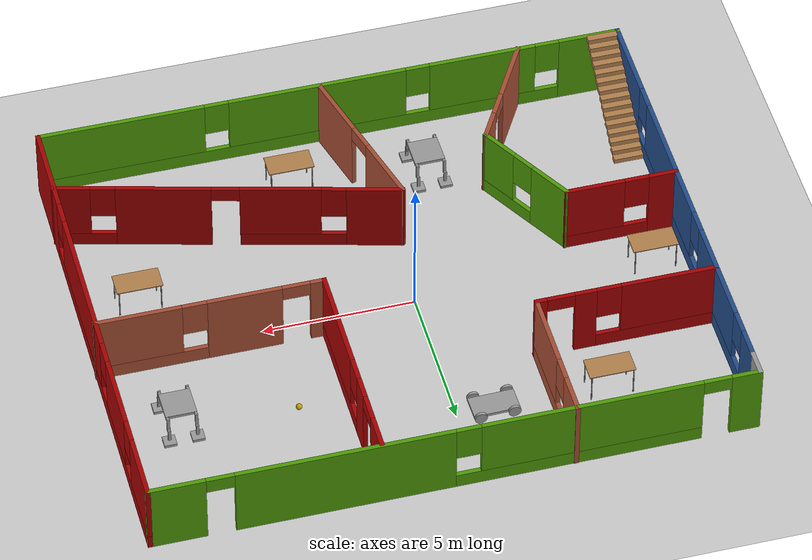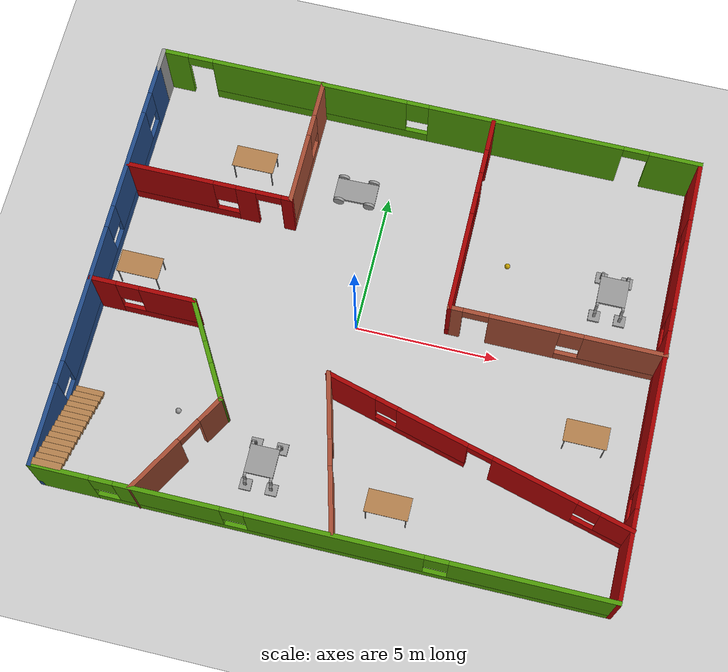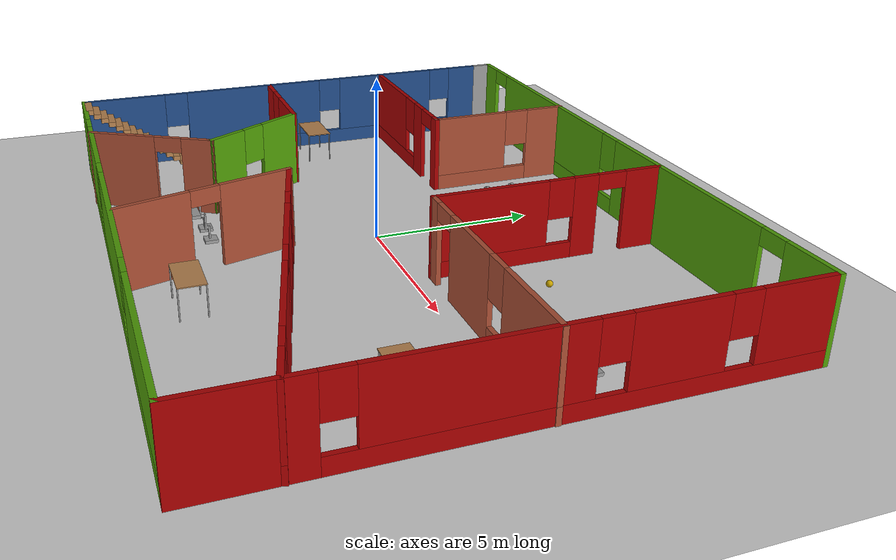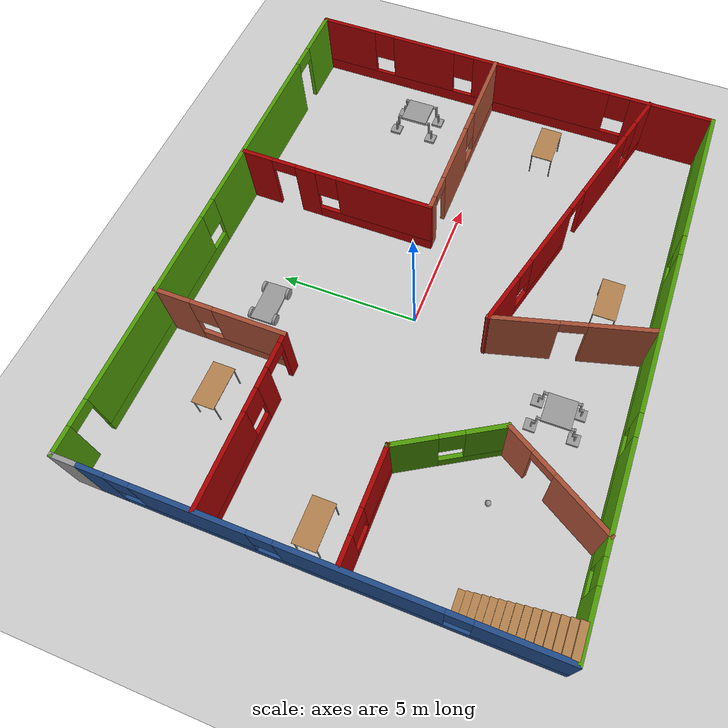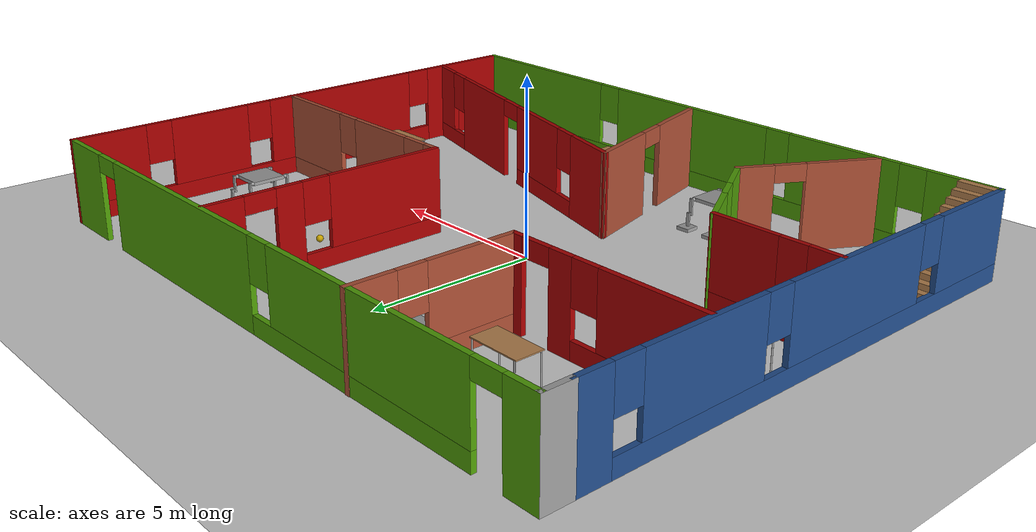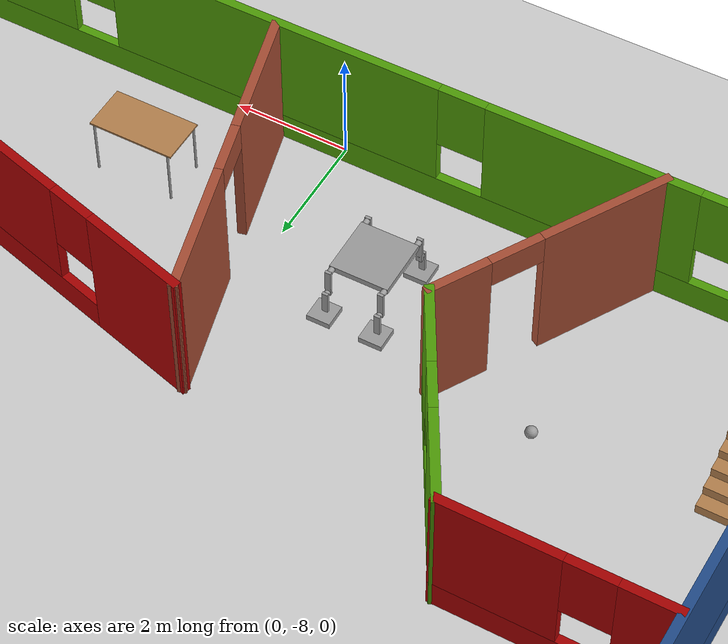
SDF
<sdf version="1.6">
 <world name="default">
  <plugin name="hello" filename="libhello.so"/>
  <light name="sun" type="directional">
   <pose>0 0 10 0 -0 0</pose>
   <diffuse>0.8 0.8 0.8 1</diffuse>
   <specular>0.2 0.2 0.2 1</specular>
   <attenuation>
    <range>1000</range>
    <constant>0.9</constant>
    <linear>0.01</linear>
    <quadratic>0.001</quadratic>
   </attenuation>
   <direction>-0.5 0.1 -0.9</direction>
  </light>
  <model name="ground_plane">
   <static>1</static>
   <link name="link">
    <collision name="collision">
     <geometry><plane><normal>0 0 1</normal><size>100 100</size></plane></geometry>
     <surface>
      <contact><collide_bitmask>65535</collide_bitmask></contact>
      <friction><ode><mu>100</mu><mu2>50</mu2></ode></friction>
     </surface>
    </collision>
    <visual name="visual">
     <cast_shadows>0</cast_shadows>
     <geometry><plane><normal>0 0 1</normal><size>100 100</size></plane></geometry>
     <material>
      <script><uri>file://media/materials/scripts/gazebo.material</uri><name>Gazebo/Grey</name></script>
     </material>
    </visual>
   </link>
  </model>
  <gravity>0 0 -9.8</gravity>
  <magnetic_field>6e-06 2.3e-05 -4.2e-05</magnetic_field>
  <atmosphere type="adiabatic"/>
  <physics name="default_physics" default="0" type="ode">
   <max_step_size>0.001</max_step_size>
   <real_time_factor>1</real_time_factor>
   <real_time_update_rate>1000</real_time_update_rate>
  </physics>
  <scene><ambient>0.4 0.4 0.4 1</ambient><background>0.7 0.7 0.7 1</background><shadows>1</shadows></scene>
  <spherical_coordinates>
   <surface_model>EARTH_WGS84</surface_model>
   <latitude_deg>0</latitude_deg>
   <longitude_deg>0</longitude_deg>
   <elevation>0</elevation>
   <heading_deg>0</heading_deg>
  </spherical_coordinates>
  <model name="HumanoidRobot_0">
   <link name="link_0">
    <inertial>
     <mass>1</mass>
     <inertia>
      <ixx>0.166667</ixx>
      <ixy>0</ixy>
      <ixz>0</ixz>
      <iyy>0.166667</iyy>
      <iyz>0</iyz>
      <izz>0.166667</izz>
     </inertia>
    </inertial>
    <pose>0 0 1 0 -0 0</pose>
    <visual name="visual">
     <geometry><box><size>1 1 0.1</size></box></geometry>
     <material>
      <lighting>1</lighting>
      <script><uri>file://media/materials/scripts/gazebo.material</uri><name>Gazebo/Grey</name></script>
      <shader type="pixel"><normal_map>__default__</normal_map></shader>
      <ambient>0.3 0.3 0.3 1</ambient>
      <diffuse>0.7 0.7 0.7 1</diffuse>
      <specular>0.01 0.01 0.01 1</specular>
      <emissive>0 0 0 1</emissive>
     </material>
    </visual>
    <collision name="collision">
     <geometry><box><size>1 1 0.1</size></box></geometry>
     <surface>
      <friction>
       <ode><mu>1</mu><mu2>1</mu2><fdir1>0 0 0</fdir1><slip1>0</slip1><slip2>0</slip2></ode>
       <torsional>
        <coefficient>1</coefficient>
        <patch_radius>0</patch_radius>
        <surface_radius>0</surface_radius>
        <use_patch_radius>1</use_patch_radius>
        <ode><slip>0</slip></ode>
       </torsional>
      </friction>
      <bounce><restitution_coefficient>0</restitution_coefficient><threshold>1e+06</threshold></bounce>
      <contact>
       <collide_without_contact>0</collide_without_contact>
       <collide_without_contact_bitmask>1</collide_without_contact_bitmask>
       <collide_bitmask>1</collide_bitmask>
       <ode>
        <soft_cfm>0</soft_cfm>
        <soft_erp>0.2</soft_erp>
        <kp>1e+13</kp>
        <kd>1</kd>
        <max_vel>0.01</max_vel>
        <min_depth>0</min_depth>
       </ode>
       <bullet>
        <split_impulse>1</split_impulse>
        <split_impulse_penetration_threshold>-0.01</split_impulse_penetration_threshold>
        <soft_cfm>0</soft_cfm>
        <soft_erp>0.2</soft_erp>
        <kp>1e+13</kp>
        <kd>1</kd>
       </bullet>
      </contact>
     </surface>
    </collision>
   </link>
   <link name="link_0_0">
    <inertial>
     <mass>1</mass>
     <inertia><ixx>0.145833</ixx><ixy>0</ixy><ixz>0</ixz><iyy>0.145833</iyy><iyz>0</iyz><izz>0.125</izz></inertia>
    </inertial>
    <pose>-0.45 -0.550013 1 1.5707 -0 0</pose>
    <visual name="visual">
     <geometry><cylinder><radius>0.05</radius><length>0.1</length></cylinder></geometry>
     <material>
      <lighting>1</lighting>
      <script><uri>file://media/materials/scripts/gazebo.material</uri><name>Gazebo/Grey</name></script>
      <shader type="pixel"><normal_map>__default__</normal_map></shader>
      <ambient>0.3 0.3 0.3 1</ambient>
      <diffuse>0.7 0.7 0.7 1</diffuse>
      <specular>0.01 0.01 0.01 1</specular>
      <emissive>0 0 0 1</emissive>
     </material>
    </visual>
    <collision name="collision">
     <geometry><cylinder><radius>0.05</radius><length>0.1</length></cylinder></geometry>
     <surface>
      <friction>
       <ode><mu>1</mu><mu2>1</mu2><fdir1>0 0 0</fdir1><slip1>0</slip1><slip2>0</slip2></ode>
       <torsional>
        <coefficient>1</coefficient>
        <patch_radius>0</patch_radius>
        <surface_radius>0</surface_radius>
        <use_patch_radius>1</use_patch_radius>
        <ode><slip>0</slip></ode>
       </torsional>
      </friction>
      <bounce><restitution_coefficient>0</restitution_coefficient><threshold>1e+06</threshold></bounce>
      <contact>
       <collide_without_contact>0</collide_without_contact>
       <collide_without_contact_bitmask>1</collide_without_contact_bitmask>
       <collide_bitmask>1</collide_bitmask>
       <ode>
        <soft_cfm>0</soft_cfm>
        <soft_erp>0.2</soft_erp>
        <kp>1e+13</kp>
        <kd>1</kd>
        <max_vel>0.01</max_vel>
        <min_depth>0</min_depth>
       </ode>
       <bullet>
        <split_impulse>1</split_impulse>
        <split_impulse_penetration_threshold>-0.01</split_impulse_penetration_threshold>
        <soft_cfm>0</soft_cfm>
        <soft_erp>0.2</soft_erp>
        <kp>1e+13</kp>
        <kd>1</kd>
       </bullet>
      </contact>
     </surface>
    </collision>
   </link>
   <link name="link_0_0_clone">
    <inertial>
     <mass>1</mass>
     <inertia><ixx>0.145833</ixx><ixy>0</ixy><ixz>0</ixz><iyy>0.145833</iyy><iyz>0</iyz><izz>0.125</izz></inertia>
    </inertial>
    <pose>-0.45 0.550005 1 1.5707 -0 0</pose>
    <visual name="visual_0">
     <geometry><cylinder><radius>0.05</radius><length>0.1</length></cylinder></geometry>
     <material>
      <lighting>1</lighting>
      <script><uri>file://media/materials/scripts/gazebo.material</uri><name>Gazebo/Grey</name></script>
      <shader type="pixel"><normal_map>__default__</normal_map></shader>
      <ambient>0.3 0.3 0.3 1</ambient>
      <diffuse>0.7 0.7 0.7 1</diffuse>
      <specular>0.01 0.01 0.01 1</specular>
      <emissive>0 0 0 1</emissive>
     </material>
    </visual>
    <collision name="collision">
     <geometry><cylinder><radius>0.05</radius><length>0.1</length></cylinder></geometry>
     <surface>
      <friction>
       <ode><mu>1</mu><mu2>1</mu2><fdir1>0 0 0</fdir1><slip1>0</slip1><slip2>0</slip2></ode>
       <torsional>
        <coefficient>1</coefficient>
        <patch_radius>0</patch_radius>
        <surface_radius>0</surface_radius>
        <use_patch_radius>1</use_patch_radius>
        <ode><slip>0</slip></ode>
       </torsional>
      </friction>
      <bounce><restitution_coefficient>0</restitution_coefficient><threshold>1e+06</threshold></bounce>
      <contact>
       <collide_without_contact>0</collide_without_contact>
       <collide_without_contact_bitmask>1</collide_without_contact_bitmask>
       <collide_bitmask>1</collide_bitmask>
       <ode>
        <soft_cfm>0</soft_cfm>
        <soft_erp>0.2</soft_erp>
        <kp>1e+13</kp>
        <kd>1</kd>
        <max_vel>0.01</max_vel>
        <min_depth>0</min_depth>
       </ode>
       <bullet>
        <split_impulse>1</split_impulse>
        <split_impulse_penetration_threshold>-0.01</split_impulse_penetration_threshold>
        <soft_cfm>0</soft_cfm>
        <soft_erp>0.2</soft_erp>
        <kp>1e+13</kp>
        <kd>1</kd>
       </bullet>
      </contact>
     </surface>
    </collision>
   </link>
   <link name="link_0_0_clone_0">
    <inertial>
     <mass>1</mass>
     <inertia><ixx>0.145833</ixx><ixy>0</ixy><ixz>0</ixz><iyy>0.145833</iyy><iyz>0</iyz><izz>0.125</izz></inertia>
    </inertial>
    <pose>0.45 -0.550005 1 1.5707 -0 0</pose>
    <visual name="visual_0">
     <geometry><cylinder><radius>0.05</radius><length>0.1</length></cylinder></geometry>
     <material>
      <lighting>1</lighting>
      <script><uri>file://media/materials/scripts/gazebo.material</uri><name>Gazebo/Grey</name></script>
      <shader type="pixel"><normal_map>__default__</normal_map></shader>
      <ambient>0.3 0.3 0.3 1</ambient>
      <diffuse>0.7 0.7 0.7 1</diffuse>
      <specular>0.01 0.01 0.01 1</specular>
      <emissive>0 0 0 1</emissive>
     </material>
    </visual>
    <collision name="collision">
     <geometry><cylinder><radius>0.05</radius><length>0.1</length></cylinder></geometry>
     <surface>
      <friction>
       <ode><mu>1</mu><mu2>1</mu2><fdir1>0 0 0</fdir1><slip1>0</slip1><slip2>0</slip2></ode>
       <torsional>
        <coefficient>1</coefficient>
        <patch_radius>0</patch_radius>
        <surface_radius>0</surface_radius>
        <use_patch_radius>1</use_patch_radius>
        <ode><slip>0</slip></ode>
       </torsional>
      </friction>
      <bounce><restitution_coefficient>0</restitution_coefficient><threshold>1e+06</threshold></bounce>
      <contact>
       <collide_without_contact>0</collide_without_contact>
       <collide_without_contact_bitmask>1</collide_without_contact_bitmask>
       <collide_bitmask>1</collide_bitmask>
       <ode>
        <soft_cfm>0</soft_cfm>
        <soft_erp>0.2</soft_erp>
        <kp>1e+13</kp>
        <kd>1</kd>
        <max_vel>0.01</max_vel>
        <min_depth>0</min_depth>
       </ode>
       <bullet>
        <split_impulse>1</split_impulse>
        <split_impulse_penetration_threshold>-0.01</split_impulse_penetration_threshold>
        <soft_cfm>0</soft_cfm>
        <soft_erp>0.2</soft_erp>
        <kp>1e+13</kp>
        <kd>1</kd>
       </bullet>
      </contact>
     </surface>
    </collision>
   </link>
   <link name="link_0_0_clone_1">
    <inertial>
     <mass>1</mass>
     <inertia><ixx>0.145833</ixx><ixy>0</ixy><ixz>0</ixz><iyy>0.145833</iyy><iyz>0</iyz><izz>0.125</izz></inertia>
    </inertial>
    <pose>0.45 0.550005 1 1.5707 -0 0</pose>
    <visual name="visual_0">
     <geometry><cylinder><radius>0.05</radius><length>0.1</length></cylinder></geometry>
     <material>
      <lighting>1</lighting>
      <script><uri>file://media/materials/scripts/gazebo.material</uri><name>Gazebo/Grey</name></script>
      <shader type="pixel"><normal_map>__default__</normal_map></shader>
      <ambient>0.3 0.3 0.3 1</ambient>
      <diffuse>0.7 0.7 0.7 1</diffuse>
      <specular>0.01 0.01 0.01 1</specular>
      <emissive>0 0 0 1</emissive>
     </material>
    </visual>
    <collision name="collision">
     <geometry><cylinder><radius>0.05</radius><length>0.1</length></cylinder></geometry>
     <surface>
      <friction>
       <ode><mu>1</mu><mu2>1</mu2><fdir1>0 0 0</fdir1><slip1>0</slip1><slip2>0</slip2></ode>
       <torsional>
        <coefficient>1</coefficient>
        <patch_radius>0</patch_radius>
        <surface_radius>0</surface_radius>
        <use_patch_radius>1</use_patch_radius>
        <ode><slip>0</slip></ode>
       </torsional>
      </friction>
      <bounce><restitution_coefficient>0</restitution_coefficient><threshold>1e+06</threshold></bounce>
      <contact>
       <collide_without_contact>0</collide_without_contact>
       <collide_without_contact_bitmask>1</collide_without_contact_bitmask>
       <collide_bitmask>1</collide_bitmask>
       <ode>
        <soft_cfm>0</soft_cfm>
        <soft_erp>0.2</soft_erp>
        <kp>1e+13</kp>
        <kd>1</kd>
        <max_vel>0.01</max_vel>
        <min_depth>0</min_depth>
       </ode>
       <bullet>
        <split_impulse>1</split_impulse>
        <split_impulse_penetration_threshold>-0.01</split_impulse_penetration_threshold>
        <soft_cfm>0</soft_cfm>
        <soft_erp>0.2</soft_erp>
        <kp>1e+13</kp>
        <kd>1</kd>
       </bullet>
      </contact>
     </surface>
    </collision>
   </link>
   <link name="link_0_0_clone_clone">
    <inertial>
     <mass>1</mass>
     <inertia><ixx>0.145833</ixx><ixy>0</ixy><ixz>0</ixz><iyy>0.145833</iyy><iyz>0</iyz><izz>0.125</izz></inertia>
    </inertial>
    <pose>-0.45 0.650015 0.60001 1.5707 -0 0</pose>
    <visual name="visual_0">
     <geometry><cylinder><radius>0.05</radius><length>0.1</length></cylinder></geometry>
     <material>
      <lighting>1</lighting>
      <script><uri>file://media/materials/scripts/gazebo.material</uri><name>Gazebo/Grey</name></script>
      <shader type="pixel"><normal_map>__default__</normal_map></shader>
      <ambient>0.3 0.3 0.3 1</ambient>
      <diffuse>0.7 0.7 0.7 1</diffuse>
      <specular>0.01 0.01 0.01 1</specular>
      <emissive>0 0 0 1</emissive>
     </material>
    </visual>
    <collision name="collision">
     <geometry><cylinder><radius>0.05</radius><length>0.1</length></cylinder></geometry>
     <surface>
      <friction>
       <ode><mu>1</mu><mu2>1</mu2><fdir1>0 0 0</fdir1><slip1>0</slip1><slip2>0</slip2></ode>
       <torsional>
        <coefficient>1</coefficient>
        <patch_radius>0</patch_radius>
        <surface_radius>0</surface_radius>
        <use_patch_radius>1</use_patch_radius>
        <ode><slip>0</slip></ode>
       </torsional>
      </friction>
      <bounce><restitution_coefficient>0</restitution_coefficient><threshold>1e+06</threshold></bounce>
      <contact>
       <collide_without_contact>0</collide_without_contact>
       <collide_without_contact_bitmask>1</collide_without_contact_bitmask>
       <collide_bitmask>1</collide_bitmask>
       <ode>
        <soft_cfm>0</soft_cfm>
        <soft_erp>0.2</soft_erp>
        <kp>1e+13</kp>
        <kd>1</kd>
        <max_vel>0.01</max_vel>
        <min_depth>0</min_depth>
       </ode>
       <bullet>
        <split_impulse>1</split_impulse>
        <split_impulse_penetration_threshold>-0.01</split_impulse_penetration_threshold>
        <soft_cfm>0</soft_cfm>
        <soft_erp>0.2</soft_erp>
        <kp>1e+13</kp>
        <kd>1</kd>
       </bullet>
      </contact>
     </surface>
    </collision>
   </link>
   <link name="link_0_0_clone_clone_0">
    <inertial>
     <mass>1</mass>
     <inertia><ixx>0.145833</ixx><ixy>0</ixy><ixz>0</ixz><iyy>0.145833</iyy><iyz>0</iyz><izz>0.125</izz></inertia>
    </inertial>
    <pose>0.45 0.650015 0.60001 1.5707 -0 0</pose>
    <visual name="visual_0">
     <geometry><cylinder><radius>0.05</radius><length>0.1</length></cylinder></geometry>
     <material>
      <lighting>1</lighting>
      <script><uri>file://media/materials/scripts/gazebo.material</uri><name>Gazebo/Grey</name></script>
      <shader type="pixel"><normal_map>__default__</normal_map></shader>
      <ambient>0.3 0.3 0.3 1</ambient>
      <diffuse>0.7 0.7 0.7 1</diffuse>
      <specular>0.01 0.01 0.01 1</specular>
      <emissive>0 0 0 1</emissive>
     </material>
    </visual>
    <collision name="collision">
     <geometry><cylinder><radius>0.05</radius><length>0.1</length></cylinder></geometry>
     <surface>
      <friction>
       <ode><mu>1</mu><mu2>1</mu2><fdir1>0 0 0</fdir1><slip1>0</slip1><slip2>0</slip2></ode>
       <torsional>
        <coefficient>1</coefficient>
        <patch_radius>0</patch_radius>
        <surface_radius>0</surface_radius>
        <use_patch_radius>1</use_patch_radius>
        <ode><slip>0</slip></ode>
       </torsional>
      </friction>
      <bounce><restitution_coefficient>0</restitution_coefficient><threshold>1e+06</threshold></bounce>
      <contact>
       <collide_without_contact>0</collide_without_contact>
       <collide_without_contact_bitmask>1</collide_without_contact_bitmask>
       <collide_bitmask>1</collide_bitmask>
       <ode>
        <soft_cfm>0</soft_cfm>
        <soft_erp>0.2</soft_erp>
        <kp>1e+13</kp>
        <kd>1</kd>
        <max_vel>0.01</max_vel>
        <min_depth>0</min_depth>
       </ode>
       <bullet>
        <split_impulse>1</split_impulse>
        <split_impulse_penetration_threshold>-0.01</split_impulse_penetration_threshold>
        <soft_cfm>0</soft_cfm>
        <soft_erp>0.2</soft_erp>
        <kp>1e+13</kp>
        <kd>1</kd>
       </bullet>
      </contact>
     </surface>
    </collision>
   </link>
   <link name="link_0_0_clone_clone_1">
    <inertial>
     <mass>1</mass>
     <inertia><ixx>0.145833</ixx><ixy>0</ixy><ixz>0</ixz><iyy>0.145833</iyy><iyz>0</iyz><izz>0.125</izz></inertia>
    </inertial>
    <pose>0.45 -0.650015 0.60001 1.5707 -0 0</pose>
    <visual name="visual_0">
     <geometry><cylinder><radius>0.05</radius><length>0.1</length></cylinder></geometry>
     <material>
      <lighting>1</lighting>
      <script><uri>file://media/materials/scripts/gazebo.material</uri><name>Gazebo/Grey</name></script>
      <shader type="pixel"><normal_map>__default__</normal_map></shader>
      <ambient>0.3 0.3 0.3 1</ambient>
      <diffuse>0.7 0.7 0.7 1</diffuse>
      <specular>0.01 0.01 0.01 1</specular>
      <emissive>0 0 0 1</emissive>
     </material>
    </visual>
    <collision name="collision">
     <geometry><cylinder><radius>0.05</radius><length>0.1</length></cylinder></geometry>
     <surface>
      <friction>
       <ode><mu>1</mu><mu2>1</mu2><fdir1>0 0 0</fdir1><slip1>0</slip1><slip2>0</slip2></ode>
       <torsional>
        <coefficient>1</coefficient>
        <patch_radius>0</patch_radius>
        <surface_radius>0</surface_radius>
        <use_patch_radius>1</use_patch_radius>
        <ode><slip>0</slip></ode>
       </torsional>
      </friction>
      <bounce><restitution_coefficient>0</restitution_coefficient><threshold>1e+06</threshold></bounce>
      <contact>
       <collide_without_contact>0</collide_without_contact>
       <collide_without_contact_bitmask>1</collide_without_contact_bitmask>
       <collide_bitmask>1</collide_bitmask>
       <ode>
        <soft_cfm>0</soft_cfm>
        <soft_erp>0.2</soft_erp>
        <kp>1e+13</kp>
        <kd>1</kd>
        <max_vel>0.01</max_vel>
        <min_depth>0</min_depth>
       </ode>
       <bullet>
        <split_impulse>1</split_impulse>
        <split_impulse_penetration_threshold>-0.01</split_impulse_penetration_threshold>
        <soft_cfm>0</soft_cfm>
        <soft_erp>0.2</soft_erp>
        <kp>1e+13</kp>
        <kd>1</kd>
       </bullet>
      </contact>
     </surface>
    </collision>
   </link>
   <link name="link_0_0_clone_clone_2">
    <inertial>
     <mass>1</mass>
     <inertia><ixx>0.145833</ixx><ixy>0</ixy><ixz>0</ixz><iyy>0.145833</iyy><iyz>0</iyz><izz>0.125</izz></inertia>
    </inertial>
    <pose>-0.45 -0.650023 0.60001 1.5707 -0 0</pose>
    <visual name="visual_0">
     <geometry><cylinder><radius>0.05</radius><length>0.1</length></cylinder></geometry>
     <material>
      <lighting>1</lighting>
      <script><uri>file://media/materials/scripts/gazebo.material</uri><name>Gazebo/Grey</name></script>
      <shader type="pixel"><normal_map>__default__</normal_map></shader>
      <ambient>0.3 0.3 0.3 1</ambient>
      <diffuse>0.7 0.7 0.7 1</diffuse>
      <specular>0.01 0.01 0.01 1</specular>
      <emissive>0 0 0 1</emissive>
     </material>
    </visual>
    <collision name="collision">
     <geometry><cylinder><radius>0.05</radius><length>0.1</length></cylinder></geometry>
     <surface>
      <friction>
       <ode><mu>1</mu><mu2>1</mu2><fdir1>0 0 0</fdir1><slip1>0</slip1><slip2>0</slip2></ode>
       <torsional>
        <coefficient>1</coefficient>
        <patch_radius>0</patch_radius>
        <surface_radius>0</surface_radius>
        <use_patch_radius>1</use_patch_radius>
        <ode><slip>0</slip></ode>
       </torsional>
      </friction>
      <bounce><restitution_coefficient>0</restitution_coefficient><threshold>1e+06</threshold></bounce>
      <contact>
       <collide_without_contact>0</collide_without_contact>
       <collide_without_contact_bitmask>1</collide_without_contact_bitmask>
       <collide_bitmask>1</collide_bitmask>
       <ode>
        <soft_cfm>0</soft_cfm>
        <soft_erp>0.2</soft_erp>
        <kp>1e+13</kp>
        <kd>1</kd>
        <max_vel>0.01</max_vel>
        <min_depth>0</min_depth>
       </ode>
       <bullet>
        <split_impulse>1</split_impulse>
        <split_impulse_penetration_threshold>-0.01</split_impulse_penetration_threshold>
        <soft_cfm>0</soft_cfm>
        <soft_erp>0.2</soft_erp>
        <kp>1e+13</kp>
        <kd>1</kd>
       </bullet>
      </contact>
     </surface>
    </collision>
   </link>
   <link name="link_0_1">
    <inertial>
     <mass>1</mass>
     <inertia>
      <ixx>0.166667</ixx>
      <ixy>0</ixy>
      <ixz>0</ixz>
      <iyy>0.166667</iyy>
      <iyz>0</iyz>
      <izz>0.166667</izz>
     </inertia>
    </inertial>
    <pose>-0.439136 0.748383 0.200014 0 -0 0</pose>
    <visual name="visual">
     <geometry><box><size>0.4 0.4 0.1</size></box></geometry>
     <material>
      <lighting>1</lighting>
      <script><uri>file://media/materials/scripts/gazebo.material</uri><name>Gazebo/Grey</name></script>
      <shader type="pixel"><normal_map>__default__</normal_map></shader>
      <ambient>0.3 0.3 0.3 1</ambient>
      <diffuse>0.7 0.7 0.7 1</diffuse>
      <specular>0.01 0.01 0.01 1</specular>
      <emissive>0 0 0 1</emissive>
     </material>
    </visual>
    <collision name="collision">
     <geometry><box><size>0.4 0.4 0.1</size></box></geometry>
     <surface>
      <friction>
       <ode><mu>1</mu><mu2>1</mu2><fdir1>0 0 0</fdir1><slip1>0</slip1><slip2>0</slip2></ode>
       <torsional>
        <coefficient>1</coefficient>
        <patch_radius>0</patch_radius>
        <surface_radius>0</surface_radius>
        <use_patch_radius>1</use_patch_radius>
        <ode><slip>0</slip></ode>
       </torsional>
      </friction>
      <bounce><restitution_coefficient>0</restitution_coefficient><threshold>1e+06</threshold></bounce>
      <contact>
       <collide_without_contact>0</collide_without_contact>
       <collide_without_contact_bitmask>1</collide_without_contact_bitmask>
       <collide_bitmask>1</collide_bitmask>
       <ode>
        <soft_cfm>0</soft_cfm>
        <soft_erp>0.2</soft_erp>
        <kp>1e+13</kp>
        <kd>1</kd>
        <max_vel>0.01</max_vel>
        <min_depth>0</min_depth>
       </ode>
       <bullet>
        <split_impulse>1</split_impulse>
        <split_impulse_penetration_threshold>-0.01</split_impulse_penetration_threshold>
        <soft_cfm>0</soft_cfm>
        <soft_erp>0.2</soft_erp>
        <kp>1e+13</kp>
        <kd>1</kd>
       </bullet>
      </contact>
     </surface>
    </collision>
   </link>
   <link name="link_0_1_clone">
    <inertial>
     <mass>1</mass>
     <inertia>
      <ixx>0.166667</ixx>
      <ixy>0</ixy>
      <ixz>0</ixz>
      <iyy>0.166667</iyy>
      <iyz>0</iyz>
      <izz>0.166667</izz>
     </inertia>
    </inertial>
    <pose>0.460864 0.748383 0.200014 0 -0 0</pose>
    <visual name="visual_0">
     <geometry><box><size>0.4 0.4 0.1</size></box></geometry>
     <material>
      <lighting>1</lighting>
      <script><uri>file://media/materials/scripts/gazebo.material</uri><name>Gazebo/Grey</name></script>
      <shader type="pixel"><normal_map>__default__</normal_map></shader>
      <ambient>0.3 0.3 0.3 1</ambient>
      <diffuse>0.7 0.7 0.7 1</diffuse>
      <specular>0.01 0.01 0.01 1</specular>
      <emissive>0 0 0 1</emissive>
     </material>
    </visual>
    <collision name="collision">
     <geometry><box><size>0.4 0.4 0.1</size></box></geometry>
     <surface>
      <friction>
       <ode><mu>1</mu><mu2>1</mu2><fdir1>0 0 0</fdir1><slip1>0</slip1><slip2>0</slip2></ode>
       <torsional>
        <coefficient>1</coefficient>
        <patch_radius>0</patch_radius>
        <surface_radius>0</surface_radius>
        <use_patch_radius>1</use_patch_radius>
        <ode><slip>0</slip></ode>
       </torsional>
      </friction>
      <bounce><restitution_coefficient>0</restitution_coefficient><threshold>1e+06</threshold></bounce>
      <contact>
       <collide_without_contact>0</collide_without_contact>
       <collide_without_contact_bitmask>1</collide_without_contact_bitmask>
       <collide_bitmask>1</collide_bitmask>
       <ode>
        <soft_cfm>0</soft_cfm>
        <soft_erp>0.2</soft_erp>
        <kp>1e+13</kp>
        <kd>1</kd>
        <max_vel>0.01</max_vel>
        <min_depth>0</min_depth>
       </ode>
       <bullet>
        <split_impulse>1</split_impulse>
        <split_impulse_penetration_threshold>-0.01</split_impulse_penetration_threshold>
        <soft_cfm>0</soft_cfm>
        <soft_erp>0.2</soft_erp>
        <kp>1e+13</kp>
        <kd>1</kd>
       </bullet>
      </contact>
     </surface>
    </collision>
   </link>
   <link name="link_0_1_clone_0">
    <inertial>
     <mass>1</mass>
     <inertia>
      <ixx>0.166667</ixx>
      <ixy>0</ixy>
      <ixz>0</ixz>
      <iyy>0.166667</iyy>
      <iyz>0</iyz>
      <izz>0.166667</izz>
     </inertia>
    </inertial>
    <pose>0.460864 -0.701655 0.200014 0 -0 0</pose>
    <visual name="visual_0">
     <geometry><box><size>0.4 0.4 0.1</size></box></geometry>
     <material>
      <lighting>1</lighting>
      <script><uri>file://media/materials/scripts/gazebo.material</uri><name>Gazebo/Grey</name></script>
      <shader type="pixel"><normal_map>__default__</normal_map></shader>
      <ambient>0.3 0.3 0.3 1</ambient>
      <diffuse>0.7 0.7 0.7 1</diffuse>
      <specular>0.01 0.01 0.01 1</specular>
      <emissive>0 0 0 1</emissive>
     </material>
    </visual>
    <collision name="collision">
     <geometry><box><size>0.4 0.4 0.1</size></box></geometry>
     <surface>
      <friction>
       <ode><mu>1</mu><mu2>1</mu2><fdir1>0 0 0</fdir1><slip1>0</slip1><slip2>0</slip2></ode>
       <torsional>
        <coefficient>1</coefficient>
        <patch_radius>0</patch_radius>
        <surface_radius>0</surface_radius>
        <use_patch_radius>1</use_patch_radius>
        <ode><slip>0</slip></ode>
       </torsional>
      </friction>
      <bounce><restitution_coefficient>0</restitution_coefficient><threshold>1e+06</threshold></bounce>
      <contact>
       <collide_without_contact>0</collide_without_contact>
       <collide_without_contact_bitmask>1</collide_without_contact_bitmask>
       <collide_bitmask>1</collide_bitmask>
       <ode>
        <soft_cfm>0</soft_cfm>
        <soft_erp>0.2</soft_erp>
        <kp>1e+13</kp>
        <kd>1</kd>
        <max_vel>0.01</max_vel>
        <min_depth>0</min_depth>
       </ode>
       <bullet>
        <split_impulse>1</split_impulse>
        <split_impulse_penetration_threshold>-0.01</split_impulse_penetration_threshold>
        <soft_cfm>0</soft_cfm>
        <soft_erp>0.2</soft_erp>
        <kp>1e+13</kp>
        <kd>1</kd>
       </bullet>
      </contact>
     </surface>
    </collision>
   </link>
   <link name="link_0_1_clone_1">
    <inertial>
     <mass>1</mass>
     <inertia>
      <ixx>0.166667</ixx>
      <ixy>0</ixy>
      <ixz>0</ixz>
      <iyy>0.166667</iyy>
      <iyz>0</iyz>
      <izz>0.166667</izz>
     </inertia>
    </inertial>
    <pose>-0.439136 -0.701664 0.200014 0 -0 0</pose>
    <visual name="visual_0">
     <geometry><box><size>0.4 0.4 0.1</size></box></geometry>
     <material>
      <lighting>1</lighting>
      <script><uri>file://media/materials/scripts/gazebo.material</uri><name>Gazebo/Grey</name></script>
      <shader type="pixel"><normal_map>__default__</normal_map></shader>
      <ambient>0.3 0.3 0.3 1</ambient>
      <diffuse>0.7 0.7 0.7 1</diffuse>
      <specular>0.01 0.01 0.01 1</specular>
      <emissive>0 0 0 1</emissive>
     </material>
    </visual>
    <collision name="collision">
     <geometry><box><size>0.4 0.4 0.1</size></box></geometry>
     <surface>
      <friction>
       <ode><mu>1</mu><mu2>1</mu2><fdir1>0 0 0</fdir1><slip1>0</slip1><slip2>0</slip2></ode>
       <torsional>
        <coefficient>1</coefficient>
        <patch_radius>0</patch_radius>
        <surface_radius>0</surface_radius>
        <use_patch_radius>1</use_patch_radius>
        <ode><slip>0</slip></ode>
       </torsional>
      </friction>
      <bounce><restitution_coefficient>0</restitution_coefficient><threshold>1e+06</threshold></bounce>
      <contact>
       <collide_without_contact>0</collide_without_contact>
       <collide_without_contact_bitmask>1</collide_without_contact_bitmask>
       <collide_bitmask>1</collide_bitmask>
       <ode>
        <soft_cfm>0</soft_cfm>
        <soft_erp>0.2</soft_erp>
        <kp>1e+13</kp>
        <kd>1</kd>
        <max_vel>0.01</max_vel>
        <min_depth>0</min_depth>
       </ode>
       <bullet>
        <split_impulse>1</split_impulse>
        <split_impulse_penetration_threshold>-0.01</split_impulse_penetration_threshold>
        <soft_cfm>0</soft_cfm>
        <soft_erp>0.2</soft_erp>
        <kp>1e+13</kp>
        <kd>1</kd>
       </bullet>
      </contact>
     </surface>
    </collision>
   </link>
   <link name="link_1">
    <inertial>
     <mass>1</mass>
     <inertia>
      <ixx>0.166667</ixx>
      <ixy>0</ixy>
      <ixz>0</ixz>
      <iyy>0.166667</iyy>
      <iyz>0</iyz>
      <izz>0.166667</izz>
     </inertia>
    </inertial>
    <pose>-0.45 0.62501 0.800005 0 -0 0</pose>
    <visual name="visual">
     <geometry><box><size>0.1 0.05 0.5</size></box></geometry>
     <material>
      <lighting>1</lighting>
      <script><uri>file://media/materials/scripts/gazebo.material</uri><name>Gazebo/Grey</name></script>
      <shader type="pixel"><normal_map>__default__</normal_map></shader>
      <ambient>0.3 0.3 0.3 1</ambient>
      <diffuse>0.7 0.7 0.7 1</diffuse>
      <specular>0.01 0.01 0.01 1</specular>
      <emissive>0 0 0 1</emissive>
     </material>
    </visual>
    <collision name="collision">
     <geometry><box><size>0.1 0.05 0.5</size></box></geometry>
     <surface>
      <friction>
       <ode><mu>1</mu><mu2>1</mu2><fdir1>0 0 0</fdir1><slip1>0</slip1><slip2>0</slip2></ode>
       <torsional>
        <coefficient>1</coefficient>
        <patch_radius>0</patch_radius>
        <surface_radius>0</surface_radius>
        <use_patch_radius>1</use_patch_radius>
        <ode><slip>0</slip></ode>
       </torsional>
      </friction>
      <bounce><restitution_coefficient>0</restitution_coefficient><threshold>1e+06</threshold></bounce>
      <contact>
       <collide_without_contact>0</collide_without_contact>
       <collide_without_contact_bitmask>1</collide_without_contact_bitmask>
       <collide_bitmask>1</collide_bitmask>
       <ode>
        <soft_cfm>0</soft_cfm>
        <soft_erp>0.2</soft_erp>
        <kp>1e+13</kp>
        <kd>1</kd>
        <max_vel>0.01</max_vel>
        <min_depth>0</min_depth>
       </ode>
       <bullet>
        <split_impulse>1</split_impulse>
        <split_impulse_penetration_threshold>-0.01</split_impulse_penetration_threshold>
        <soft_cfm>0</soft_cfm>
        <soft_erp>0.2</soft_erp>
        <kp>1e+13</kp>
        <kd>1</kd>
       </bullet>
      </contact>
     </surface>
    </collision>
   </link>
   <link name="link_1_clone">
    <inertial>
     <mass>1</mass>
     <inertia>
      <ixx>0.166667</ixx>
      <ixy>0</ixy>
      <ixz>0</ixz>
      <iyy>0.166667</iyy>
      <iyz>0</iyz>
      <izz>0.166667</izz>
     </inertia>
    </inertial>
    <pose>0.45 0.62501 0.800005 0 -0 0</pose>
    <visual name="visual">
     <geometry><box><size>0.1 0.05 0.5</size></box></geometry>
     <material>
      <lighting>1</lighting>
      <script><uri>file://media/materials/scripts/gazebo.material</uri><name>Gazebo/Grey</name></script>
      <shader type="pixel"><normal_map>__default__</normal_map></shader>
      <ambient>0.3 0.3 0.3 1</ambient>
      <diffuse>0.7 0.7 0.7 1</diffuse>
      <specular>0.01 0.01 0.01 1</specular>
      <emissive>0 0 0 1</emissive>
     </material>
    </visual>
    <collision name="collision">
     <geometry><box><size>0.1 0.05 0.5</size></box></geometry>
     <surface>
      <friction>
       <ode><mu>1</mu><mu2>1</mu2><fdir1>0 0 0</fdir1><slip1>0</slip1><slip2>0</slip2></ode>
       <torsional>
        <coefficient>1</coefficient>
        <patch_radius>0</patch_radius>
        <surface_radius>0</surface_radius>
        <use_patch_radius>1</use_patch_radius>
        <ode><slip>0</slip></ode>
       </torsional>
      </friction>
      <bounce><restitution_coefficient>0</restitution_coefficient><threshold>1e+06</threshold></bounce>
      <contact>
       <collide_without_contact>0</collide_without_contact>
       <collide_without_contact_bitmask>1</collide_without_contact_bitmask>
       <collide_bitmask>1</collide_bitmask>
       <ode>
        <soft_cfm>0</soft_cfm>
        <soft_erp>0.2</soft_erp>
        <kp>1e+13</kp>
        <kd>1</kd>
        <max_vel>0.01</max_vel>
        <min_depth>0</min_depth>
       </ode>
       <bullet>
        <split_impulse>1</split_impulse>
        <split_impulse_penetration_threshold>-0.01</split_impulse_penetration_threshold>
        <soft_cfm>0</soft_cfm>
        <soft_erp>0.2</soft_erp>
        <kp>1e+13</kp>
        <kd>1</kd>
       </bullet>
      </contact>
     </surface>
    </collision>
   </link>
   <link name="link_1_clone_0">
    <inertial>
     <mass>1</mass>
     <inertia>
      <ixx>0.166667</ixx>
      <ixy>0</ixy>
      <ixz>0</ixz>
      <iyy>0.166667</iyy>
      <iyz>0</iyz>
      <izz>0.166667</izz>
     </inertia>
    </inertial>
    <pose>0.45 -0.62501 0.800005 0 -0 0</pose>
    <visual name="visual">
     <geometry><box><size>0.1 0.05 0.5</size></box></geometry>
     <material>
      <lighting>1</lighting>
      <script><uri>file://media/materials/scripts/gazebo.material</uri><name>Gazebo/Grey</name></script>
      <shader type="pixel"><normal_map>__default__</normal_map></shader>
      <ambient>0.3 0.3 0.3 1</ambient>
      <diffuse>0.7 0.7 0.7 1</diffuse>
      <specular>0.01 0.01 0.01 1</specular>
      <emissive>0 0 0 1</emissive>
     </material>
    </visual>
    <collision name="collision">
     <geometry><box><size>0.1 0.05 0.5</size></box></geometry>
     <surface>
      <friction>
       <ode><mu>1</mu><mu2>1</mu2><fdir1>0 0 0</fdir1><slip1>0</slip1><slip2>0</slip2></ode>
       <torsional>
        <coefficient>1</coefficient>
        <patch_radius>0</patch_radius>
        <surface_radius>0</surface_radius>
        <use_patch_radius>1</use_patch_radius>
        <ode><slip>0</slip></ode>
       </torsional>
      </friction>
      <bounce><restitution_coefficient>0</restitution_coefficient><threshold>1e+06</threshold></bounce>
      <contact>
       <collide_without_contact>0</collide_without_contact>
       <collide_without_contact_bitmask>1</collide_without_contact_bitmask>
       <collide_bitmask>1</collide_bitmask>
       <ode>
        <soft_cfm>0</soft_cfm>
        <soft_erp>0.2</soft_erp>
        <kp>1e+13</kp>
        <kd>1</kd>
        <max_vel>0.01</max_vel>
        <min_depth>0</min_depth>
       </ode>
       <bullet>
        <split_impulse>1</split_impulse>
        <split_impulse_penetration_threshold>-0.01</split_impulse_penetration_threshold>
        <soft_cfm>0</soft_cfm>
        <soft_erp>0.2</soft_erp>
        <kp>1e+13</kp>
        <kd>1</kd>
       </bullet>
      </contact>
     </surface>
    </collision>
   </link>
   <link name="link_1_clone_1">
    <inertial>
     <mass>1</mass>
     <inertia>
      <ixx>0.166667</ixx>
      <ixy>0</ixy>
      <ixz>0</ixz>
      <iyy>0.166667</iyy>
      <iyz>0</iyz>
      <izz>0.166667</izz>
     </inertia>
    </inertial>
    <pose>-0.45 -0.625018 0.800005 0 -0 0</pose>
    <visual name="visual">
     <geometry><box><size>0.1 0.05 0.5</size></box></geometry>
     <material>
      <lighting>1</lighting>
      <script><uri>file://media/materials/scripts/gazebo.material</uri><name>Gazebo/Grey</name></script>
      <shader type="pixel"><normal_map>__default__</normal_map></shader>
      <ambient>0.3 0.3 0.3 1</ambient>
      <diffuse>0.7 0.7 0.7 1</diffuse>
      <specular>0.01 0.01 0.01 1</specular>
      <emissive>0 0 0 1</emissive>
     </material>
    </visual>
    <collision name="collision">
     <geometry><box><size>0.1 0.05 0.5</size></box></geometry>
     <surface>
      <friction>
       <ode><mu>1</mu><mu2>1</mu2><fdir1>0 0 0</fdir1><slip1>0</slip1><slip2>0</slip2></ode>
       <torsional>
        <coefficient>1</coefficient>
        <patch_radius>0</patch_radius>
        <surface_radius>0</surface_radius>
        <use_patch_radius>1</use_patch_radius>
        <ode><slip>0</slip></ode>
       </torsional>
      </friction>
      <bounce><restitution_coefficient>0</restitution_coefficient><threshold>1e+06</threshold></bounce>
      <contact>
       <collide_without_contact>0</collide_without_contact>
       <collide_without_contact_bitmask>1</collide_without_contact_bitmask>
       <collide_bitmask>1</collide_bitmask>
       <ode>
        <soft_cfm>0</soft_cfm>
        <soft_erp>0.2</soft_erp>
        <kp>1e+13</kp>
        <kd>1</kd>
        <max_vel>0.01</max_vel>
        <min_depth>0</min_depth>
       </ode>
       <bullet>
        <split_impulse>1</split_impulse>
        <split_impulse_penetration_threshold>-0.01</split_impulse_penetration_threshold>
        <soft_cfm>0</soft_cfm>
        <soft_erp>0.2</soft_erp>
        <kp>1e+13</kp>
        <kd>1</kd>
       </bullet>
      </contact>
     </surface>
    </collision>
   </link>
   <link name="link_1_clone_2">
    <inertial>
     <mass>1</mass>
     <inertia>
      <ixx>0.166667</ixx>
      <ixy>0</ixy>
      <ixz>0</ixz>
      <iyy>0.166667</iyy>
      <iyz>0</iyz>
      <izz>0.166667</izz>
     </inertia>
    </inertial>
    <pose>-0.45 0.725019 0.400014 0 -0 0</pose>
    <visual name="visual">
     <geometry><box><size>0.1 0.05 0.5</size></box></geometry>
     <material>
      <lighting>1</lighting>
      <script><uri>file://media/materials/scripts/gazebo.material</uri><name>Gazebo/Grey</name></script>
      <shader type="pixel"><normal_map>__default__</normal_map></shader>
      <ambient>0.3 0.3 0.3 1</ambient>
      <diffuse>0.7 0.7 0.7 1</diffuse>
      <specular>0.01 0.01 0.01 1</specular>
      <emissive>0 0 0 1</emissive>
     </material>
    </visual>
    <collision name="collision">
     <geometry><box><size>0.1 0.05 0.5</size></box></geometry>
     <surface>
      <friction>
       <ode><mu>1</mu><mu2>1</mu2><fdir1>0 0 0</fdir1><slip1>0</slip1><slip2>0</slip2></ode>
       <torsional>
        <coefficient>1</coefficient>
        <patch_radius>0</patch_radius>
        <surface_radius>0</surface_radius>
        <use_patch_radius>1</use_patch_radius>
        <ode><slip>0</slip></ode>
       </torsional>
      </friction>
      <bounce><restitution_coefficient>0</restitution_coefficient><threshold>1e+06</threshold></bounce>
      <contact>
       <collide_without_contact>0</collide_without_contact>
       <collide_without_contact_bitmask>1</collide_without_contact_bitmask>
       <collide_bitmask>1</collide_bitmask>
       <ode>
        <soft_cfm>0</soft_cfm>
        <soft_erp>0.2</soft_erp>
        <kp>1e+13</kp>
        <kd>1</kd>
        <max_vel>0.01</max_vel>
        <min_depth>0</min_depth>
       </ode>
       <bullet>
        <split_impulse>1</split_impulse>
        <split_impulse_penetration_threshold>-0.01</split_impulse_penetration_threshold>
        <soft_cfm>0</soft_cfm>
        <soft_erp>0.2</soft_erp>
        <kp>1e+13</kp>
        <kd>1</kd>
       </bullet>
      </contact>
     </surface>
    </collision>
   </link>
   <link name="link_1_clone_3">
    <inertial>
     <mass>1</mass>
     <inertia>
      <ixx>0.166667</ixx>
      <ixy>0</ixy>
      <ixz>0</ixz>
      <iyy>0.166667</iyy>
      <iyz>0</iyz>
      <izz>0.166667</izz>
     </inertia>
    </inertial>
    <pose>0.45 0.725019 0.400014 0 -0 0</pose>
    <visual name="visual">
     <geometry><box><size>0.1 0.05 0.5</size></box></geometry>
     <material>
      <lighting>1</lighting>
      <script><uri>file://media/materials/scripts/gazebo.material</uri><name>Gazebo/Grey</name></script>
      <shader type="pixel"><normal_map>__default__</normal_map></shader>
      <ambient>0.3 0.3 0.3 1</ambient>
      <diffuse>0.7 0.7 0.7 1</diffuse>
      <specular>0.01 0.01 0.01 1</specular>
      <emissive>0 0 0 1</emissive>
     </material>
    </visual>
    <collision name="collision">
     <geometry><box><size>0.1 0.05 0.5</size></box></geometry>
     <surface>
      <friction>
       <ode><mu>1</mu><mu2>1</mu2><fdir1>0 0 0</fdir1><slip1>0</slip1><slip2>0</slip2></ode>
       <torsional>
        <coefficient>1</coefficient>
        <patch_radius>0</patch_radius>
        <surface_radius>0</surface_radius>
        <use_patch_radius>1</use_patch_radius>
        <ode><slip>0</slip></ode>
       </torsional>
      </friction>
      <bounce><restitution_coefficient>0</restitution_coefficient><threshold>1e+06</threshold></bounce>
      <contact>
       <collide_without_contact>0</collide_without_contact>
       <collide_without_contact_bitmask>1</collide_without_contact_bitmask>
       <collide_bitmask>1</collide_bitmask>
       <ode>
        <soft_cfm>0</soft_cfm>
        <soft_erp>0.2</soft_erp>
        <kp>1e+13</kp>
        <kd>1</kd>
        <max_vel>0.01</max_vel>
        <min_depth>0</min_depth>
       </ode>
       <bullet>
        <split_impulse>1</split_impulse>
        <split_impulse_penetration_threshold>-0.01</split_impulse_penetration_threshold>
        <soft_cfm>0</soft_cfm>
        <soft_erp>0.2</soft_erp>
        <kp>1e+13</kp>
        <kd>1</kd>
       </bullet>
      </contact>
     </surface>
    </collision>
   </link>
   <link name="link_1_clone_4">
    <inertial>
     <mass>1</mass>
     <inertia>
      <ixx>0.166667</ixx>
      <ixy>0</ixy>
      <ixz>0</ixz>
      <iyy>0.166667</iyy>
      <iyz>0</iyz>
      <izz>0.166667</izz>
     </inertia>
    </inertial>
    <pose>0.45 -0.725019 0.400014 0 -0 0</pose>
    <visual name="visual">
     <geometry><box><size>0.1 0.05 0.5</size></box></geometry>
     <material>
      <lighting>1</lighting>
      <script><uri>file://media/materials/scripts/gazebo.material</uri><name>Gazebo/Grey</name></script>
      <shader type="pixel"><normal_map>__default__</normal_map></shader>
      <ambient>0.3 0.3 0.3 1</ambient>
      <diffuse>0.7 0.7 0.7 1</diffuse>
      <specular>0.01 0.01 0.01 1</specular>
      <emissive>0 0 0 1</emissive>
     </material>
    </visual>
    <collision name="collision">
     <geometry><box><size>0.1 0.05 0.5</size></box></geometry>
     <surface>
      <friction>
       <ode><mu>1</mu><mu2>1</mu2><fdir1>0 0 0</fdir1><slip1>0</slip1><slip2>0</slip2></ode>
       <torsional>
        <coefficient>1</coefficient>
        <patch_radius>0</patch_radius>
        <surface_radius>0</surface_radius>
        <use_patch_radius>1</use_patch_radius>
        <ode><slip>0</slip></ode>
       </torsional>
      </friction>
      <bounce><restitution_coefficient>0</restitution_coefficient><threshold>1e+06</threshold></bounce>
      <contact>
       <collide_without_contact>0</collide_without_contact>
       <collide_without_contact_bitmask>1</collide_without_contact_bitmask>
       <collide_bitmask>1</collide_bitmask>
       <ode>
        <soft_cfm>0</soft_cfm>
        <soft_erp>0.2</soft_erp>
        <kp>1e+13</kp>
        <kd>1</kd>
        <max_vel>0.01</max_vel>
        <min_depth>0</min_depth>
       </ode>
       <bullet>
        <split_impulse>1</split_impulse>
        <split_impulse_penetration_threshold>-0.01</split_impulse_penetration_threshold>
        <soft_cfm>0</soft_cfm>
        <soft_erp>0.2</soft_erp>
        <kp>1e+13</kp>
        <kd>1</kd>
       </bullet>
      </contact>
     </surface>
    </collision>
   </link>
   <link name="link_1_clone_5">
    <inertial>
     <mass>1</mass>
     <inertia>
      <ixx>0.166667</ixx>
      <ixy>0</ixy>
      <ixz>0</ixz>
      <iyy>0.166667</iyy>
      <iyz>0</iyz>
      <izz>0.166667</izz>
     </inertia>
    </inertial>
    <pose>-0.45 -0.725028 0.400014 0 -0 0</pose>
    <visual name="visual">
     <geometry><box><size>0.1 0.05 0.5</size></box></geometry>
     <material>
      <lighting>1</lighting>
      <script><uri>file://media/materials/scripts/gazebo.material</uri><name>Gazebo/Grey</name></script>
      <shader type="pixel"><normal_map>__default__</normal_map></shader>
      <ambient>0.3 0.3 0.3 1</ambient>
      <diffuse>0.7 0.7 0.7 1</diffuse>
      <specular>0.01 0.01 0.01 1</specular>
      <emissive>0 0 0 1</emissive>
     </material>
    </visual>
    <collision name="collision">
     <geometry><box><size>0.1 0.05 0.5</size></box></geometry>
     <surface>
      <friction>
       <ode><mu>1</mu><mu2>1</mu2><fdir1>0 0 0</fdir1><slip1>0</slip1><slip2>0</slip2></ode>
       <torsional>
        <coefficient>1</coefficient>
        <patch_radius>0</patch_radius>
        <surface_radius>0</surface_radius>
        <use_patch_radius>1</use_patch_radius>
        <ode><slip>0</slip></ode>
       </torsional>
      </friction>
      <bounce><restitution_coefficient>0</restitution_coefficient><threshold>1e+06</threshold></bounce>
      <contact>
       <collide_without_contact>0</collide_without_contact>
       <collide_without_contact_bitmask>1</collide_without_contact_bitmask>
       <collide_bitmask>1</collide_bitmask>
       <ode>
        <soft_cfm>0</soft_cfm>
        <soft_erp>0.2</soft_erp>
        <kp>1e+13</kp>
        <kd>1</kd>
        <max_vel>0.01</max_vel>
        <min_depth>0</min_depth>
       </ode>
       <bullet>
        <split_impulse>1</split_impulse>
        <split_impulse_penetration_threshold>-0.01</split_impulse_penetration_threshold>
        <soft_cfm>0</soft_cfm>
        <soft_erp>0.2</soft_erp>
        <kp>1e+13</kp>
        <kd>1</kd>
       </bullet>
      </contact>
     </surface>
    </collision>
   </link>
   <joint name="link_0_0_JOINT_8" type="fixed">
    <parent>link_0_0</parent>
    <child>link_1_clone_1</child>
    <physics>
     <ode><limit><cfm>0</cfm><erp>0.2</erp></limit><suspension><cfm>0</cfm><erp>0.2</erp></suspension></ode>
    </physics>
   </joint>
   <joint name="link_0_0_clone_0_JOINT_7" type="fixed">
    <parent>link_0_0_clone_0</parent>
    <child>link_1_clone_0</child>
    <physics>
     <ode><limit><cfm>0</cfm><erp>0.2</erp></limit><suspension><cfm>0</cfm><erp>0.2</erp></suspension></ode>
    </physics>
   </joint>
   <joint name="link_0_0_clone_1_JOINT_6" type="fixed">
    <parent>link_0_0_clone_1</parent>
    <child>link_1_clone</child>
    <physics>
     <ode><limit><cfm>0</cfm><erp>0.2</erp></limit><suspension><cfm>0</cfm><erp>0.2</erp></suspension></ode>
    </physics>
   </joint>
   <joint name="link_0_0_clone_JOINT_5" type="fixed">
    <parent>link_0_0_clone</parent>
    <child>link_1</child>
    <physics>
     <ode><limit><cfm>0</cfm><erp>0.2</erp></limit><suspension><cfm>0</cfm><erp>0.2</erp></suspension></ode>
    </physics>
   </joint>
   <joint name="link_0_0_clone_clone_0_JOINT_18" type="revolute">
    <parent>link_0_0_clone_clone_0</parent>
    <child>link_1_clone_3</child>
    <axis>
     <xyz>0 0 1</xyz>
     <use_parent_model_frame>0</use_parent_model_frame>
     <limit>
      <lower>-1.79769e+308</lower>
      <upper>1.79769e+308</upper>
      <effort>-1</effort>
      <velocity>-1</velocity>
     </limit>
     <dynamics>
      <spring_reference>0</spring_reference>
      <spring_stiffness>0</spring_stiffness>
      <damping>0</damping>
      <friction>0</friction>
     </dynamics>
    </axis>
    <physics>
     <ode><limit><cfm>0</cfm><erp>0.2</erp></limit><suspension><cfm>0</cfm><erp>0.2</erp></suspension></ode>
    </physics>
   </joint>
   <joint name="link_0_0_clone_clone_2_JOINT_20" type="revolute">
    <parent>link_0_0_clone_clone_2</parent>
    <child>link_1_clone_5</child>
    <axis>
     <xyz>0 0 1</xyz>
     <use_parent_model_frame>0</use_parent_model_frame>
     <limit>
      <lower>-1.79769e+308</lower>
      <upper>1.79769e+308</upper>
      <effort>-1</effort>
      <velocity>-1</velocity>
     </limit>
     <dynamics>
      <spring_reference>0</spring_reference>
      <spring_stiffness>0</spring_stiffness>
      <damping>0</damping>
      <friction>0</friction>
     </dynamics>
    </axis>
    <physics>
     <ode><limit><cfm>0</cfm><erp>0.2</erp></limit><suspension><cfm>0</cfm><erp>0.2</erp></suspension></ode>
    </physics>
   </joint>
   <joint name="link_0_JOINT_1" type="revolute">
    <parent>link_0</parent>
    <child>link_0_0</child>
    <axis>
     <xyz>0 0 1</xyz>
     <use_parent_model_frame>0</use_parent_model_frame>
     <limit>
      <lower>-1.79769e+308</lower>
      <upper>1.79769e+308</upper>
      <effort>-1</effort>
      <velocity>-1</velocity>
     </limit>
     <dynamics>
      <spring_reference>0</spring_reference>
      <spring_stiffness>0</spring_stiffness>
      <damping>0</damping>
      <friction>0</friction>
     </dynamics>
    </axis>
    <physics>
     <ode><limit><cfm>0</cfm><erp>0.2</erp></limit><suspension><cfm>0</cfm><erp>0.2</erp></suspension></ode>
    </physics>
   </joint>
   <joint name="link_0_JOINT_2" type="revolute">
    <parent>link_0</parent>
    <child>link_0_0_clone</child>
    <axis>
     <xyz>0 0 1</xyz>
     <use_parent_model_frame>0</use_parent_model_frame>
     <limit>
      <lower>-1.79769e+308</lower>
      <upper>1.79769e+308</upper>
      <effort>-1</effort>
      <velocity>-1</velocity>
     </limit>
     <dynamics>
      <spring_reference>0</spring_reference>
      <spring_stiffness>0</spring_stiffness>
      <damping>0</damping>
      <friction>0</friction>
     </dynamics>
    </axis>
    <physics>
     <ode><limit><cfm>0</cfm><erp>0.2</erp></limit><suspension><cfm>0</cfm><erp>0.2</erp></suspension></ode>
    </physics>
   </joint>
   <joint name="link_0_JOINT_3" type="revolute">
    <parent>link_0</parent>
    <child>link_0_0_clone_0</child>
    <axis>
     <xyz>1 0 0</xyz>
     <use_parent_model_frame>0</use_parent_model_frame>
     <limit>
      <lower>-1.79769e+308</lower>
      <upper>1.79769e+308</upper>
      <effort>-1</effort>
      <velocity>-1</velocity>
     </limit>
     <dynamics>
      <spring_reference>0</spring_reference>
      <spring_stiffness>0</spring_stiffness>
      <damping>0</damping>
      <friction>0</friction>
     </dynamics>
    </axis>
    <physics>
     <ode><limit><cfm>0</cfm><erp>0.2</erp></limit><suspension><cfm>0</cfm><erp>0.2</erp></suspension></ode>
    </physics>
   </joint>
   <joint name="link_0_JOINT_4" type="revolute">
    <parent>link_0</parent>
    <child>link_0_0_clone_1</child>
    <axis>
     <xyz>1 0 0</xyz>
     <use_parent_model_frame>0</use_parent_model_frame>
     <limit>
      <lower>-1.79769e+308</lower>
      <upper>1.79769e+308</upper>
      <effort>-1</effort>
      <velocity>-1</velocity>
     </limit>
     <dynamics>
      <spring_reference>0</spring_reference>
      <spring_stiffness>0</spring_stiffness>
      <damping>0</damping>
      <friction>0</friction>
     </dynamics>
    </axis>
    <physics>
     <ode><limit><cfm>0</cfm><erp>0.2</erp></limit><suspension><cfm>0</cfm><erp>0.2</erp></suspension></ode>
    </physics>
   </joint>
   <joint name="link_1_JOINT_14" type="revolute">
    <parent>link_1</parent>
    <child>link_0_0_clone_clone</child>
    <axis>
     <xyz>1 0 0</xyz>
     <use_parent_model_frame>0</use_parent_model_frame>
     <limit>
      <lower>-1.79769e+308</lower>
      <upper>1.79769e+308</upper>
      <effort>-1</effort>
      <velocity>-1</velocity>
     </limit>
     <dynamics>
      <spring_reference>0</spring_reference>
      <spring_stiffness>0</spring_stiffness>
      <damping>0</damping>
      <friction>0</friction>
     </dynamics>
    </axis>
    <physics>
     <ode><limit><cfm>0</cfm><erp>0.2</erp></limit><suspension><cfm>0</cfm><erp>0.2</erp></suspension></ode>
    </physics>
   </joint>
   <joint name="link_1_clone_0_JOINT_15" type="fixed">
    <parent>link_1_clone_0</parent>
    <child>link_0_0_clone_clone_1</child>
    <physics>
     <ode><limit><cfm>0</cfm><erp>0.2</erp></limit><suspension><cfm>0</cfm><erp>0.2</erp></suspension></ode>
    </physics>
   </joint>
   <joint name="link_1_clone_1_JOINT_16" type="revolute">
    <parent>link_1_clone_1</parent>
    <child>link_0_0_clone_clone_2</child>
    <axis>
     <xyz>1 0 0</xyz>
     <use_parent_model_frame>0</use_parent_model_frame>
     <limit>
      <lower>-1.79769e+308</lower>
      <upper>1.79769e+308</upper>
      <effort>-1</effort>
      <velocity>-1</velocity>
     </limit>
     <dynamics>
      <spring_reference>0</spring_reference>
      <spring_stiffness>0</spring_stiffness>
      <damping>0</damping>
      <friction>0</friction>
     </dynamics>
    </axis>
    <physics>
     <ode><limit><cfm>0</cfm><erp>0.2</erp></limit><suspension><cfm>0</cfm><erp>0.2</erp></suspension></ode>
    </physics>
   </joint>
   <joint name="link_1_clone_2_JOINT_17" type="revolute">
    <parent>link_0_0_clone_clone</parent>
    <child>link_1_clone_2</child>
    <axis>
     <xyz>0 0 1</xyz>
     <use_parent_model_frame>0</use_parent_model_frame>
     <limit>
      <lower>-1.79769e+308</lower>
      <upper>1.79769e+308</upper>
      <effort>-1</effort>
      <velocity>-1</velocity>
     </limit>
     <dynamics>
      <spring_reference>0</spring_reference>
      <spring_stiffness>0</spring_stiffness>
      <damping>0</damping>
      <friction>0</friction>
     </dynamics>
    </axis>
    <physics>
     <ode><limit><cfm>0</cfm><erp>0.2</erp></limit><suspension><cfm>0</cfm><erp>0.2</erp></suspension></ode>
    </physics>
   </joint>
   <joint name="link_1_clone_2_JOINT_1" type="fixed">
    <parent>link_1_clone_2</parent>
    <child>link_0_1</child>
    <physics>
     <ode><limit><cfm>0</cfm><erp>0.2</erp></limit><suspension><cfm>0</cfm><erp>0.2</erp></suspension></ode>
    </physics>
   </joint>
   <joint name="link_1_clone_3_JOINT_2" type="fixed">
    <parent>link_1_clone_3</parent>
    <child>link_0_1_clone</child>
    <physics>
     <ode><limit><cfm>0</cfm><erp>0.2</erp></limit><suspension><cfm>0</cfm><erp>0.2</erp></suspension></ode>
    </physics>
   </joint>
   <joint name="link_1_clone_4_JOINT_19" type="revolute">
    <parent>link_0_0_clone_clone_1</parent>
    <child>link_1_clone_4</child>
    <axis>
     <xyz>0 0 1</xyz>
     <use_parent_model_frame>0</use_parent_model_frame>
     <limit>
      <lower>-1.79769e+308</lower>
      <upper>1.79769e+308</upper>
      <effort>-1</effort>
      <velocity>-1</velocity>
     </limit>
     <dynamics>
      <spring_reference>0</spring_reference>
      <spring_stiffness>0</spring_stiffness>
      <damping>0</damping>
      <friction>0</friction>
     </dynamics>
    </axis>
    <physics>
     <ode><limit><cfm>0</cfm><erp>0.2</erp></limit><suspension><cfm>0</cfm><erp>0.2</erp></suspension></ode>
    </physics>
   </joint>
   <joint name="link_1_clone_4_JOINT_4" type="fixed">
    <parent>link_1_clone_4</parent>
    <child>link_0_1_clone_0</child>
    <physics>
     <ode><limit><cfm>0</cfm><erp>0.2</erp></limit><suspension><cfm>0</cfm><erp>0.2</erp></suspension></ode>
    </physics>
   </joint>
   <joint name="link_1_clone_5_JOINT_3" type="fixed">
    <parent>link_1_clone_5</parent>
    <child>link_0_1_clone_1</child>
    <pose>0 0 0 -0.01 -0.02 -0</pose>
    <physics>
     <ode><limit><cfm>0</cfm><erp>0.2</erp></limit><suspension><cfm>0</cfm><erp>0.2</erp></suspension></ode>
    </physics>
   </joint>
   <joint name="link_1_clone_JOINT_13" type="fixed">
    <parent>link_1_clone</parent>
    <child>link_0_0_clone_clone_0</child>
    <physics>
     <ode><limit><cfm>0</cfm><erp>0.2</erp></limit><suspension><cfm>0</cfm><erp>0.2</erp></suspension></ode>
    </physics>
   </joint>
   <static>0</static>
   <pose>8.43529 3.05632 -0.150015 -2e-06 1e-06 0.005821</pose>
   <plugin name="model_push" filename="libmodel_push.so"/>
  </model>
  <model name="HumanoidRobot_2">
   <link name="link_0">
    <inertial>
     <mass>1</mass>
     <inertia>
      <ixx>0.166667</ixx>
      <ixy>0</ixy>
      <ixz>0</ixz>
      <iyy>0.166667</iyy>
      <iyz>0</iyz>
      <izz>0.166667</izz>
     </inertia>
    </inertial>
    <pose>-0 0 1 0 -0 0</pose>
    <visual name="visual">
     <geometry><box><size>1 1 0.1</size></box></geometry>
     <material>
      <lighting>1</lighting>
      <script><uri>file://media/materials/scripts/gazebo.material</uri><name>Gazebo/Grey</name></script>
      <shader type="pixel"><normal_map>__default__</normal_map></shader>
      <ambient>0.3 0.3 0.3 1</ambient>
      <diffuse>0.7 0.7 0.7 1</diffuse>
      <specular>0.01 0.01 0.01 1</specular>
      <emissive>0 0 0 1</emissive>
     </material>
    </visual>
    <collision name="collision">
     <geometry><box><size>1 1 0.1</size></box></geometry>
     <surface>
      <friction>
       <ode><mu>1</mu><mu2>1</mu2><fdir1>0 0 0</fdir1><slip1>0</slip1><slip2>0</slip2></ode>
       <torsional>
        <coefficient>1</coefficient>
        <patch_radius>0</patch_radius>
        <surface_radius>0</surface_radius>
        <use_patch_radius>1</use_patch_radius>
        <ode><slip>0</slip></ode>
       </torsional>
      </friction>
      <bounce><restitution_coefficient>0</restitution_coefficient><threshold>1e+06</threshold></bounce>
      <contact>
       <collide_without_contact>0</collide_without_contact>
       <collide_without_contact_bitmask>1</collide_without_contact_bitmask>
       <collide_bitmask>1</collide_bitmask>
       <ode>
        <soft_cfm>0</soft_cfm>
        <soft_erp>0.2</soft_erp>
        <kp>1e+13</kp>
        <kd>1</kd>
        <max_vel>0.01</max_vel>
        <min_depth>0</min_depth>
       </ode>
       <bullet>
        <split_impulse>1</split_impulse>
        <split_impulse_penetration_threshold>-0.01</split_impulse_penetration_threshold>
        <soft_cfm>0</soft_cfm>
        <soft_erp>0.2</soft_erp>
        <kp>1e+13</kp>
        <kd>1</kd>
       </bullet>
      </contact>
     </surface>
    </collision>
   </link>
   <link name="link_0_0">
    <inertial>
     <mass>1</mass>
     <inertia><ixx>0.145833</ixx><ixy>0</ixy><ixz>0</ixz><iyy>0.145833</iyy><iyz>0</iyz><izz>0.125</izz></inertia>
    </inertial>
    <pose>-0.45 -0.550013 1 1.5707 -0 0</pose>
    <visual name="visual">
     <geometry><cylinder><radius>0.05</radius><length>0.1</length></cylinder></geometry>
     <material>
      <lighting>1</lighting>
      <script><uri>file://media/materials/scripts/gazebo.material</uri><name>Gazebo/Grey</name></script>
      <shader type="pixel"><normal_map>__default__</normal_map></shader>
      <ambient>0.3 0.3 0.3 1</ambient>
      <diffuse>0.7 0.7 0.7 1</diffuse>
      <specular>0.01 0.01 0.01 1</specular>
      <emissive>0 0 0 1</emissive>
     </material>
    </visual>
    <collision name="collision">
     <geometry><cylinder><radius>0.05</radius><length>0.1</length></cylinder></geometry>
     <surface>
      <friction>
       <ode><mu>1</mu><mu2>1</mu2><fdir1>0 0 0</fdir1><slip1>0</slip1><slip2>0</slip2></ode>
       <torsional>
        <coefficient>1</coefficient>
        <patch_radius>0</patch_radius>
        <surface_radius>0</surface_radius>
        <use_patch_radius>1</use_patch_radius>
        <ode><slip>0</slip></ode>
       </torsional>
      </friction>
      <bounce><restitution_coefficient>0</restitution_coefficient><threshold>1e+06</threshold></bounce>
      <contact>
       <collide_without_contact>0</collide_without_contact>
       <collide_without_contact_bitmask>1</collide_without_contact_bitmask>
       <collide_bitmask>1</collide_bitmask>
       <ode>
        <soft_cfm>0</soft_cfm>
        <soft_erp>0.2</soft_erp>
        <kp>1e+13</kp>
        <kd>1</kd>
        <max_vel>0.01</max_vel>
        <min_depth>0</min_depth>
       </ode>
       <bullet>
        <split_impulse>1</split_impulse>
        <split_impulse_penetration_threshold>-0.01</split_impulse_penetration_threshold>
        <soft_cfm>0</soft_cfm>
        <soft_erp>0.2</soft_erp>
        <kp>1e+13</kp>
        <kd>1</kd>
       </bullet>
      </contact>
     </surface>
    </collision>
   </link>
   <link name="link_0_0_clone">
    <inertial>
     <mass>1</mass>
     <inertia><ixx>0.145833</ixx><ixy>0</ixy><ixz>0</ixz><iyy>0.145833</iyy><iyz>0</iyz><izz>0.125</izz></inertia>
    </inertial>
    <pose>-0.45 0.550005 1 1.5707 -0 0</pose>
    <visual name="visual_0">
     <geometry><cylinder><radius>0.05</radius><length>0.1</length></cylinder></geometry>
     <material>
      <lighting>1</lighting>
      <script><uri>file://media/materials/scripts/gazebo.material</uri><name>Gazebo/Grey</name></script>
      <shader type="pixel"><normal_map>__default__</normal_map></shader>
      <ambient>0.3 0.3 0.3 1</ambient>
      <diffuse>0.7 0.7 0.7 1</diffuse>
      <specular>0.01 0.01 0.01 1</specular>
      <emissive>0 0 0 1</emissive>
     </material>
    </visual>
    <collision name="collision">
     <geometry><cylinder><radius>0.05</radius><length>0.1</length></cylinder></geometry>
     <surface>
      <friction>
       <ode><mu>1</mu><mu2>1</mu2><fdir1>0 0 0</fdir1><slip1>0</slip1><slip2>0</slip2></ode>
       <torsional>
        <coefficient>1</coefficient>
        <patch_radius>0</patch_radius>
        <surface_radius>0</surface_radius>
        <use_patch_radius>1</use_patch_radius>
        <ode><slip>0</slip></ode>
       </torsional>
      </friction>
      <bounce><restitution_coefficient>0</restitution_coefficient><threshold>1e+06</threshold></bounce>
      <contact>
       <collide_without_contact>0</collide_without_contact>
       <collide_without_contact_bitmask>1</collide_without_contact_bitmask>
       <collide_bitmask>1</collide_bitmask>
       <ode>
        <soft_cfm>0</soft_cfm>
        <soft_erp>0.2</soft_erp>
        <kp>1e+13</kp>
        <kd>1</kd>
        <max_vel>0.01</max_vel>
        <min_depth>0</min_depth>
       </ode>
       <bullet>
        <split_impulse>1</split_impulse>
        <split_impulse_penetration_threshold>-0.01</split_impulse_penetration_threshold>
        <soft_cfm>0</soft_cfm>
        <soft_erp>0.2</soft_erp>
        <kp>1e+13</kp>
        <kd>1</kd>
       </bullet>
      </contact>
     </surface>
    </collision>
   </link>
   <link name="link_0_0_clone_0">
    <inertial>
     <mass>1</mass>
     <inertia><ixx>0.145833</ixx><ixy>0</ixy><ixz>0</ixz><iyy>0.145833</iyy><iyz>0</iyz><izz>0.125</izz></inertia>
    </inertial>
    <pose>0.45 -0.550005 1 1.5707 -0 0</pose>
    <visual name="visual_0">
     <geometry><cylinder><radius>0.05</radius><length>0.1</length></cylinder></geometry>
     <material>
      <lighting>1</lighting>
      <script><uri>file://media/materials/scripts/gazebo.material</uri><name>Gazebo/Grey</name></script>
      <shader type="pixel"><normal_map>__default__</normal_map></shader>
      <ambient>0.3 0.3 0.3 1</ambient>
      <diffuse>0.7 0.7 0.7 1</diffuse>
      <specular>0.01 0.01 0.01 1</specular>
      <emissive>0 0 0 1</emissive>
     </material>
    </visual>
    <collision name="collision">
     <geometry><cylinder><radius>0.05</radius><length>0.1</length></cylinder></geometry>
     <surface>
      <friction>
       <ode><mu>1</mu><mu2>1</mu2><fdir1>0 0 0</fdir1><slip1>0</slip1><slip2>0</slip2></ode>
       <torsional>
        <coefficient>1</coefficient>
        <patch_radius>0</patch_radius>
        <surface_radius>0</surface_radius>
        <use_patch_radius>1</use_patch_radius>
        <ode><slip>0</slip></ode>
       </torsional>
      </friction>
      <bounce><restitution_coefficient>0</restitution_coefficient><threshold>1e+06</threshold></bounce>
      <contact>
       <collide_without_contact>0</collide_without_contact>
       <collide_without_contact_bitmask>1</collide_without_contact_bitmask>
       <collide_bitmask>1</collide_bitmask>
       <ode>
        <soft_cfm>0</soft_cfm>
        <soft_erp>0.2</soft_erp>
        <kp>1e+13</kp>
        <kd>1</kd>
        <max_vel>0.01</max_vel>
        <min_depth>0</min_depth>
       </ode>
       <bullet>
        <split_impulse>1</split_impulse>
        <split_impulse_penetration_threshold>-0.01</split_impulse_penetration_threshold>
        <soft_cfm>0</soft_cfm>
        <soft_erp>0.2</soft_erp>
        <kp>1e+13</kp>
        <kd>1</kd>
       </bullet>
      </contact>
     </surface>
    </collision>
   </link>
   <link name="link_0_0_clone_1">
    <inertial>
     <mass>1</mass>
     <inertia><ixx>0.145833</ixx><ixy>0</ixy><ixz>0</ixz><iyy>0.145833</iyy><iyz>0</iyz><izz>0.125</izz></inertia>
    </inertial>
    <pose>0.45 0.550005 1 1.5707 -0 0</pose>
    <visual name="visual_0">
     <geometry><cylinder><radius>0.05</radius><length>0.1</length></cylinder></geometry>
     <material>
      <lighting>1</lighting>
      <script><uri>file://media/materials/scripts/gazebo.material</uri><name>Gazebo/Grey</name></script>
      <shader type="pixel"><normal_map>__default__</normal_map></shader>
      <ambient>0.3 0.3 0.3 1</ambient>
      <diffuse>0.7 0.7 0.7 1</diffuse>
      <specular>0.01 0.01 0.01 1</specular>
      <emissive>0 0 0 1</emissive>
     </material>
    </visual>
    <collision name="collision">
     <geometry><cylinder><radius>0.05</radius><length>0.1</length></cylinder></geometry>
     <surface>
      <friction>
       <ode><mu>1</mu><mu2>1</mu2><fdir1>0 0 0</fdir1><slip1>0</slip1><slip2>0</slip2></ode>
       <torsional>
        <coefficient>1</coefficient>
        <patch_radius>0</patch_radius>
        <surface_radius>0</surface_radius>
        <use_patch_radius>1</use_patch_radius>
        <ode><slip>0</slip></ode>
       </torsional>
      </friction>
      <bounce><restitution_coefficient>0</restitution_coefficient><threshold>1e+06</threshold></bounce>
      <contact>
       <collide_without_contact>0</collide_without_contact>
       <collide_without_contact_bitmask>1</collide_without_contact_bitmask>
       <collide_bitmask>1</collide_bitmask>
       <ode>
        <soft_cfm>0</soft_cfm>
        <soft_erp>0.2</soft_erp>
        <kp>1e+13</kp>
        <kd>1</kd>
        <max_vel>0.01</max_vel>
        <min_depth>0</min_depth>
       </ode>
       <bullet>
        <split_impulse>1</split_impulse>
        <split_impulse_penetration_threshold>-0.01</split_impulse_penetration_threshold>
        <soft_cfm>0</soft_cfm>
        <soft_erp>0.2</soft_erp>
        <kp>1e+13</kp>
        <kd>1</kd>
       </bullet>
      </contact>
     </surface>
    </collision>
   </link>
   <link name="link_0_0_clone_clone">
    <inertial>
     <mass>1</mass>
     <inertia><ixx>0.145833</ixx><ixy>0</ixy><ixz>0</ixz><iyy>0.145833</iyy><iyz>0</iyz><izz>0.125</izz></inertia>
    </inertial>
    <pose>-0.45 0.650015 0.60001 1.5707 -0 0</pose>
    <visual name="visual_0">
     <geometry><cylinder><radius>0.05</radius><length>0.1</length></cylinder></geometry>
     <material>
      <lighting>1</lighting>
      <script><uri>file://media/materials/scripts/gazebo.material</uri><name>Gazebo/Grey</name></script>
      <shader type="pixel"><normal_map>__default__</normal_map></shader>
      <ambient>0.3 0.3 0.3 1</ambient>
      <diffuse>0.7 0.7 0.7 1</diffuse>
      <specular>0.01 0.01 0.01 1</specular>
      <emissive>0 0 0 1</emissive>
     </material>
    </visual>
    <collision name="collision">
     <geometry><cylinder><radius>0.05</radius><length>0.1</length></cylinder></geometry>
     <surface>
      <friction>
       <ode><mu>1</mu><mu2>1</mu2><fdir1>0 0 0</fdir1><slip1>0</slip1><slip2>0</slip2></ode>
       <torsional>
        <coefficient>1</coefficient>
        <patch_radius>0</patch_radius>
        <surface_radius>0</surface_radius>
        <use_patch_radius>1</use_patch_radius>
        <ode><slip>0</slip></ode>
       </torsional>
      </friction>
      <bounce><restitution_coefficient>0</restitution_coefficient><threshold>1e+06</threshold></bounce>
      <contact>
       <collide_without_contact>0</collide_without_contact>
       <collide_without_contact_bitmask>1</collide_without_contact_bitmask>
       <collide_bitmask>1</collide_bitmask>
       <ode>
        <soft_cfm>0</soft_cfm>
        <soft_erp>0.2</soft_erp>
        <kp>1e+13</kp>
        <kd>1</kd>
        <max_vel>0.01</max_vel>
        <min_depth>0</min_depth>
       </ode>
       <bullet>
        <split_impulse>1</split_impulse>
        <split_impulse_penetration_threshold>-0.01</split_impulse_penetration_threshold>
        <soft_cfm>0</soft_cfm>
        <soft_erp>0.2</soft_erp>
        <kp>1e+13</kp>
        <kd>1</kd>
       </bullet>
      </contact>
     </surface>
    </collision>
   </link>
   <link name="link_0_0_clone_clone_0">
    <inertial>
     <mass>1</mass>
     <inertia><ixx>0.145833</ixx><ixy>0</ixy><ixz>0</ixz><iyy>0.145833</iyy><iyz>0</iyz><izz>0.125</izz></inertia>
    </inertial>
    <pose>0.45 0.650015 0.60001 1.5707 -0 0</pose>
    <visual name="visual_0">
     <geometry><cylinder><radius>0.05</radius><length>0.1</length></cylinder></geometry>
     <material>
      <lighting>1</lighting>
      <script><uri>file://media/materials/scripts/gazebo.material</uri><name>Gazebo/Grey</name></script>
      <shader type="pixel"><normal_map>__default__</normal_map></shader>
      <ambient>0.3 0.3 0.3 1</ambient>
      <diffuse>0.7 0.7 0.7 1</diffuse>
      <specular>0.01 0.01 0.01 1</specular>
      <emissive>0 0 0 1</emissive>
     </material>
    </visual>
    <collision name="collision">
     <geometry><cylinder><radius>0.05</radius><length>0.1</length></cylinder></geometry>
     <surface>
      <friction>
       <ode><mu>1</mu><mu2>1</mu2><fdir1>0 0 0</fdir1><slip1>0</slip1><slip2>0</slip2></ode>
       <torsional>
        <coefficient>1</coefficient>
        <patch_radius>0</patch_radius>
        <surface_radius>0</surface_radius>
        <use_patch_radius>1</use_patch_radius>
        <ode><slip>0</slip></ode>
       </torsional>
      </friction>
      <bounce><restitution_coefficient>0</restitution_coefficient><threshold>1e+06</threshold></bounce>
      <contact>
       <collide_without_contact>0</collide_without_contact>
       <collide_without_contact_bitmask>1</collide_without_contact_bitmask>
       <collide_bitmask>1</collide_bitmask>
       <ode>
        <soft_cfm>0</soft_cfm>
        <soft_erp>0.2</soft_erp>
        <kp>1e+13</kp>
        <kd>1</kd>
        <max_vel>0.01</max_vel>
        <min_depth>0</min_depth>
       </ode>
       <bullet>
        <split_impulse>1</split_impulse>
        <split_impulse_penetration_threshold>-0.01</split_impulse_penetration_threshold>
        <soft_cfm>0</soft_cfm>
        <soft_erp>0.2</soft_erp>
        <kp>1e+13</kp>
        <kd>1</kd>
       </bullet>
      </contact>
     </surface>
    </collision>
   </link>
   <link name="link_0_0_clone_clone_1">
    <inertial>
     <mass>1</mass>
     <inertia><ixx>0.145833</ixx><ixy>0</ixy><ixz>0</ixz><iyy>0.145833</iyy><iyz>0</iyz><izz>0.125</izz></inertia>
    </inertial>
    <pose>0.45 -0.650015 0.60001 1.5707 -0 0</pose>
    <visual name="visual_0">
     <geometry><cylinder><radius>0.05</radius><length>0.1</length></cylinder></geometry>
     <material>
      <lighting>1</lighting>
      <script><uri>file://media/materials/scripts/gazebo.material</uri><name>Gazebo/Grey</name></script>
      <shader type="pixel"><normal_map>__default__</normal_map></shader>
      <ambient>0.3 0.3 0.3 1</ambient>
      <diffuse>0.7 0.7 0.7 1</diffuse>
      <specular>0.01 0.01 0.01 1</specular>
      <emissive>0 0 0 1</emissive>
     </material>
    </visual>
    <collision name="collision">
     <geometry><cylinder><radius>0.05</radius><length>0.1</length></cylinder></geometry>
     <surface>
      <friction>
       <ode><mu>1</mu><mu2>1</mu2><fdir1>0 0 0</fdir1><slip1>0</slip1><slip2>0</slip2></ode>
       <torsional>
        <coefficient>1</coefficient>
        <patch_radius>0</patch_radius>
        <surface_radius>0</surface_radius>
        <use_patch_radius>1</use_patch_radius>
        <ode><slip>0</slip></ode>
       </torsional>
      </friction>
      <bounce><restitution_coefficient>0</restitution_coefficient><threshold>1e+06</threshold></bounce>
      <contact>
       <collide_without_contact>0</collide_without_contact>
       <collide_without_contact_bitmask>1</collide_without_contact_bitmask>
       <collide_bitmask>1</collide_bitmask>
       <ode>
        <soft_cfm>0</soft_cfm>
        <soft_erp>0.2</soft_erp>
        <kp>1e+13</kp>
        <kd>1</kd>
        <max_vel>0.01</max_vel>
        <min_depth>0</min_depth>
       </ode>
       <bullet>
        <split_impulse>1</split_impulse>
        <split_impulse_penetration_threshold>-0.01</split_impulse_penetration_threshold>
        <soft_cfm>0</soft_cfm>
        <soft_erp>0.2</soft_erp>
        <kp>1e+13</kp>
        <kd>1</kd>
       </bullet>
      </contact>
     </surface>
    </collision>
   </link>
   <link name="link_0_0_clone_clone_2">
    <inertial>
     <mass>1</mass>
     <inertia><ixx>0.145833</ixx><ixy>0</ixy><ixz>0</ixz><iyy>0.145833</iyy><iyz>0</iyz><izz>0.125</izz></inertia>
    </inertial>
    <pose>-0.45 -0.650023 0.60001 1.5707 -0 0</pose>
    <visual name="visual_0">
     <geometry><cylinder><radius>0.05</radius><length>0.1</length></cylinder></geometry>
     <material>
      <lighting>1</lighting>
      <script><uri>file://media/materials/scripts/gazebo.material</uri><name>Gazebo/Grey</name></script>
      <shader type="pixel"><normal_map>__default__</normal_map></shader>
      <ambient>0.3 0.3 0.3 1</ambient>
      <diffuse>0.7 0.7 0.7 1</diffuse>
      <specular>0.01 0.01 0.01 1</specular>
      <emissive>0 0 0 1</emissive>
     </material>
    </visual>
    <collision name="collision">
     <geometry><cylinder><radius>0.05</radius><length>0.1</length></cylinder></geometry>
     <surface>
      <friction>
       <ode><mu>1</mu><mu2>1</mu2><fdir1>0 0 0</fdir1><slip1>0</slip1><slip2>0</slip2></ode>
       <torsional>
        <coefficient>1</coefficient>
        <patch_radius>0</patch_radius>
        <surface_radius>0</surface_radius>
        <use_patch_radius>1</use_patch_radius>
        <ode><slip>0</slip></ode>
       </torsional>
      </friction>
      <bounce><restitution_coefficient>0</restitution_coefficient><threshold>1e+06</threshold></bounce>
      <contact>
       <collide_without_contact>0</collide_without_contact>
       <collide_without_contact_bitmask>1</collide_without_contact_bitmask>
       <collide_bitmask>1</collide_bitmask>
       <ode>
        <soft_cfm>0</soft_cfm>
        <soft_erp>0.2</soft_erp>
        <kp>1e+13</kp>
        <kd>1</kd>
        <max_vel>0.01</max_vel>
        <min_depth>0</min_depth>
       </ode>
       <bullet>
        <split_impulse>1</split_impulse>
        <split_impulse_penetration_threshold>-0.01</split_impulse_penetration_threshold>
        <soft_cfm>0</soft_cfm>
        <soft_erp>0.2</soft_erp>
        <kp>1e+13</kp>
        <kd>1</kd>
       </bullet>
      </contact>
     </surface>
    </collision>
   </link>
   <link name="link_0_1">
    <inertial>
     <mass>1</mass>
     <inertia>
      <ixx>0.166667</ixx>
      <ixy>0</ixy>
      <ixz>0</ixz>
      <iyy>0.166667</iyy>
      <iyz>0</iyz>
      <izz>0.166667</izz>
     </inertia>
    </inertial>
    <pose>-0.439136 0.748383 0.200014 0 -0 0</pose>
    <visual name="visual">
     <geometry><box><size>0.4 0.4 0.1</size></box></geometry>
     <material>
      <lighting>1</lighting>
      <script><uri>file://media/materials/scripts/gazebo.material</uri><name>Gazebo/Grey</name></script>
      <shader type="pixel"><normal_map>__default__</normal_map></shader>
      <ambient>0.3 0.3 0.3 1</ambient>
      <diffuse>0.7 0.7 0.7 1</diffuse>
      <specular>0.01 0.01 0.01 1</specular>
      <emissive>0 0 0 1</emissive>
     </material>
    </visual>
    <collision name="collision">
     <geometry><box><size>0.4 0.4 0.1</size></box></geometry>
     <surface>
      <friction>
       <ode><mu>1</mu><mu2>1</mu2><fdir1>0 0 0</fdir1><slip1>0</slip1><slip2>0</slip2></ode>
       <torsional>
        <coefficient>1</coefficient>
        <patch_radius>0</patch_radius>
        <surface_radius>0</surface_radius>
        <use_patch_radius>1</use_patch_radius>
        <ode><slip>0</slip></ode>
       </torsional>
      </friction>
      <bounce><restitution_coefficient>0</restitution_coefficient><threshold>1e+06</threshold></bounce>
      <contact>
       <collide_without_contact>0</collide_without_contact>
       <collide_without_contact_bitmask>1</collide_without_contact_bitmask>
       <collide_bitmask>1</collide_bitmask>
       <ode>
        <soft_cfm>0</soft_cfm>
        <soft_erp>0.2</soft_erp>
        <kp>1e+13</kp>
        <kd>1</kd>
        <max_vel>0.01</max_vel>
        <min_depth>0</min_depth>
       </ode>
       <bullet>
        <split_impulse>1</split_impulse>
        <split_impulse_penetration_threshold>-0.01</split_impulse_penetration_threshold>
        <soft_cfm>0</soft_cfm>
        <soft_erp>0.2</soft_erp>
        <kp>1e+13</kp>
        <kd>1</kd>
       </bullet>
      </contact>
     </surface>
    </collision>
   </link>
   <link name="link_0_1_clone">
    <inertial>
     <mass>1</mass>
     <inertia>
      <ixx>0.166667</ixx>
      <ixy>0</ixy>
      <ixz>0</ixz>
      <iyy>0.166667</iyy>
      <iyz>0</iyz>
      <izz>0.166667</izz>
     </inertia>
    </inertial>
    <pose>0.460864 0.748383 0.200014 0 -0 0</pose>
    <visual name="visual_0">
     <geometry><box><size>0.4 0.4 0.1</size></box></geometry>
     <material>
      <lighting>1</lighting>
      <script><uri>file://media/materials/scripts/gazebo.material</uri><name>Gazebo/Grey</name></script>
      <shader type="pixel"><normal_map>__default__</normal_map></shader>
      <ambient>0.3 0.3 0.3 1</ambient>
      <diffuse>0.7 0.7 0.7 1</diffuse>
      <specular>0.01 0.01 0.01 1</specular>
      <emissive>0 0 0 1</emissive>
     </material>
    </visual>
    <collision name="collision">
     <geometry><box><size>0.4 0.4 0.1</size></box></geometry>
     <surface>
      <friction>
       <ode><mu>1</mu><mu2>1</mu2><fdir1>0 0 0</fdir1><slip1>0</slip1><slip2>0</slip2></ode>
       <torsional>
        <coefficient>1</coefficient>
        <patch_radius>0</patch_radius>
        <surface_radius>0</surface_radius>
        <use_patch_radius>1</use_patch_radius>
        <ode><slip>0</slip></ode>
       </torsional>
      </friction>
      <bounce><restitution_coefficient>0</restitution_coefficient><threshold>1e+06</threshold></bounce>
      <contact>
       <collide_without_contact>0</collide_without_contact>
       <collide_without_contact_bitmask>1</collide_without_contact_bitmask>
       <collide_bitmask>1</collide_bitmask>
       <ode>
        <soft_cfm>0</soft_cfm>
        <soft_erp>0.2</soft_erp>
        <kp>1e+13</kp>
        <kd>1</kd>
        <max_vel>0.01</max_vel>
        <min_depth>0</min_depth>
       </ode>
       <bullet>
        <split_impulse>1</split_impulse>
        <split_impulse_penetration_threshold>-0.01</split_impulse_penetration_threshold>
        <soft_cfm>0</soft_cfm>
        <soft_erp>0.2</soft_erp>
        <kp>1e+13</kp>
        <kd>1</kd>
       </bullet>
      </contact>
     </surface>
    </collision>
   </link>
   <link name="link_0_1_clone_0">
    <inertial>
     <mass>1</mass>
     <inertia>
      <ixx>0.166667</ixx>
      <ixy>0</ixy>
      <ixz>0</ixz>
      <iyy>0.166667</iyy>
      <iyz>0</iyz>
      <izz>0.166667</izz>
     </inertia>
    </inertial>
    <pose>0.460864 -0.701655 0.200014 0 -0 0</pose>
    <visual name="visual_0">
     <geometry><box><size>0.4 0.4 0.1</size></box></geometry>
     <material>
      <lighting>1</lighting>
      <script><uri>file://media/materials/scripts/gazebo.material</uri><name>Gazebo/Grey</name></script>
      <shader type="pixel"><normal_map>__default__</normal_map></shader>
      <ambient>0.3 0.3 0.3 1</ambient>
      <diffuse>0.7 0.7 0.7 1</diffuse>
      <specular>0.01 0.01 0.01 1</specular>
      <emissive>0 0 0 1</emissive>
     </material>
    </visual>
    <collision name="collision">
     <geometry><box><size>0.4 0.4 0.1</size></box></geometry>
     <surface>
      <friction>
       <ode><mu>1</mu><mu2>1</mu2><fdir1>0 0 0</fdir1><slip1>0</slip1><slip2>0</slip2></ode>
       <torsional>
        <coefficient>1</coefficient>
        <patch_radius>0</patch_radius>
        <surface_radius>0</surface_radius>
        <use_patch_radius>1</use_patch_radius>
        <ode><slip>0</slip></ode>
       </torsional>
      </friction>
      <bounce><restitution_coefficient>0</restitution_coefficient><threshold>1e+06</threshold></bounce>
      <contact>
       <collide_without_contact>0</collide_without_contact>
       <collide_without_contact_bitmask>1</collide_without_contact_bitmask>
       <collide_bitmask>1</collide_bitmask>
       <ode>
        <soft_cfm>0</soft_cfm>
        <soft_erp>0.2</soft_erp>
        <kp>1e+13</kp>
        <kd>1</kd>
        <max_vel>0.01</max_vel>
        <min_depth>0</min_depth>
       </ode>
       <bullet>
        <split_impulse>1</split_impulse>
        <split_impulse_penetration_threshold>-0.01</split_impulse_penetration_threshold>
        <soft_cfm>0</soft_cfm>
        <soft_erp>0.2</soft_erp>
        <kp>1e+13</kp>
        <kd>1</kd>
       </bullet>
      </contact>
     </surface>
    </collision>
   </link>
   <link name="link_0_1_clone_1">
    <inertial>
     <mass>1</mass>
     <inertia>
      <ixx>0.166667</ixx>
      <ixy>0</ixy>
      <ixz>0</ixz>
      <iyy>0.166667</iyy>
      <iyz>0</iyz>
      <izz>0.166667</izz>
     </inertia>
    </inertial>
    <pose>-0.439136 -0.701664 0.200014 0 -0 0</pose>
    <visual name="visual_0">
     <geometry><box><size>0.4 0.4 0.1</size></box></geometry>
     <material>
      <lighting>1</lighting>
      <script><uri>file://media/materials/scripts/gazebo.material</uri><name>Gazebo/Grey</name></script>
      <shader type="pixel"><normal_map>__default__</normal_map></shader>
      <ambient>0.3 0.3 0.3 1</ambient>
      <diffuse>0.7 0.7 0.7 1</diffuse>
      <specular>0.01 0.01 0.01 1</specular>
      <emissive>0 0 0 1</emissive>
     </material>
    </visual>
    <collision name="collision">
     <geometry><box><size>0.4 0.4 0.1</size></box></geometry>
     <surface>
      <friction>
       <ode><mu>1</mu><mu2>1</mu2><fdir1>0 0 0</fdir1><slip1>0</slip1><slip2>0</slip2></ode>
       <torsional>
        <coefficient>1</coefficient>
        <patch_radius>0</patch_radius>
        <surface_radius>0</surface_radius>
        <use_patch_radius>1</use_patch_radius>
        <ode><slip>0</slip></ode>
       </torsional>
      </friction>
      <bounce><restitution_coefficient>0</restitution_coefficient><threshold>1e+06</threshold></bounce>
      <contact>
       <collide_without_contact>0</collide_without_contact>
       <collide_without_contact_bitmask>1</collide_without_contact_bitmask>
       <collide_bitmask>1</collide_bitmask>
       <ode>
        <soft_cfm>0</soft_cfm>
        <soft_erp>0.2</soft_erp>
        <kp>1e+13</kp>
        <kd>1</kd>
        <max_vel>0.01</max_vel>
        <min_depth>0</min_depth>
       </ode>
       <bullet>
        <split_impulse>1</split_impulse>
        <split_impulse_penetration_threshold>-0.01</split_impulse_penetration_threshold>
        <soft_cfm>0</soft_cfm>
        <soft_erp>0.2</soft_erp>
        <kp>1e+13</kp>
        <kd>1</kd>
       </bullet>
      </contact>
     </surface>
    </collision>
   </link>
   <link name="link_1">
    <inertial>
     <mass>1</mass>
     <inertia>
      <ixx>0.166667</ixx>
      <ixy>0</ixy>
      <ixz>0</ixz>
      <iyy>0.166667</iyy>
      <iyz>0</iyz>
      <izz>0.166667</izz>
     </inertia>
    </inertial>
    <pose>-0.45 0.62501 0.800005 0 -0 0</pose>
    <visual name="visual">
     <geometry><box><size>0.1 0.05 0.5</size></box></geometry>
     <material>
      <lighting>1</lighting>
      <script><uri>file://media/materials/scripts/gazebo.material</uri><name>Gazebo/Grey</name></script>
      <shader type="pixel"><normal_map>__default__</normal_map></shader>
      <ambient>0.3 0.3 0.3 1</ambient>
      <diffuse>0.7 0.7 0.7 1</diffuse>
      <specular>0.01 0.01 0.01 1</specular>
      <emissive>0 0 0 1</emissive>
     </material>
    </visual>
    <collision name="collision">
     <geometry><box><size>0.1 0.05 0.5</size></box></geometry>
     <surface>
      <friction>
       <ode><mu>1</mu><mu2>1</mu2><fdir1>0 0 0</fdir1><slip1>0</slip1><slip2>0</slip2></ode>
       <torsional>
        <coefficient>1</coefficient>
        <patch_radius>0</patch_radius>
        <surface_radius>0</surface_radius>
        <use_patch_radius>1</use_patch_radius>
        <ode><slip>0</slip></ode>
       </torsional>
      </friction>
      <bounce><restitution_coefficient>0</restitution_coefficient><threshold>1e+06</threshold></bounce>
      <contact>
       <collide_without_contact>0</collide_without_contact>
       <collide_without_contact_bitmask>1</collide_without_contact_bitmask>
       <collide_bitmask>1</collide_bitmask>
       <ode>
        <soft_cfm>0</soft_cfm>
        <soft_erp>0.2</soft_erp>
        <kp>1e+13</kp>
        <kd>1</kd>
        <max_vel>0.01</max_vel>
        <min_depth>0</min_depth>
       </ode>
       <bullet>
        <split_impulse>1</split_impulse>
        <split_impulse_penetration_threshold>-0.01</split_impulse_penetration_threshold>
        <soft_cfm>0</soft_cfm>
        <soft_erp>0.2</soft_erp>
        <kp>1e+13</kp>
        <kd>1</kd>
       </bullet>
      </contact>
     </surface>
    </collision>
   </link>
   <link name="link_1_clone">
    <inertial>
     <mass>1</mass>
     <inertia>
      <ixx>0.166667</ixx>
      <ixy>0</ixy>
      <ixz>0</ixz>
      <iyy>0.166667</iyy>
      <iyz>0</iyz>
      <izz>0.166667</izz>
     </inertia>
    </inertial>
    <pose>0.45 0.62501 0.800005 0 -0 0</pose>
    <visual name="visual">
     <geometry><box><size>0.1 0.05 0.5</size></box></geometry>
     <material>
      <lighting>1</lighting>
      <script><uri>file://media/materials/scripts/gazebo.material</uri><name>Gazebo/Grey</name></script>
      <shader type="pixel"><normal_map>__default__</normal_map></shader>
      <ambient>0.3 0.3 0.3 1</ambient>
      <diffuse>0.7 0.7 0.7 1</diffuse>
      <specular>0.01 0.01 0.01 1</specular>
      <emissive>0 0 0 1</emissive>
     </material>
    </visual>
    <collision name="collision">
     <geometry><box><size>0.1 0.05 0.5</size></box></geometry>
     <surface>
      <friction>
       <ode><mu>1</mu><mu2>1</mu2><fdir1>0 0 0</fdir1><slip1>0</slip1><slip2>0</slip2></ode>
       <torsional>
        <coefficient>1</coefficient>
        <patch_radius>0</patch_radius>
        <surface_radius>0</surface_radius>
        <use_patch_radius>1</use_patch_radius>
        <ode><slip>0</slip></ode>
       </torsional>
      </friction>
      <bounce><restitution_coefficient>0</restitution_coefficient><threshold>1e+06</threshold></bounce>
      <contact>
       <collide_without_contact>0</collide_without_contact>
       <collide_without_contact_bitmask>1</collide_without_contact_bitmask>
       <collide_bitmask>1</collide_bitmask>
       <ode>
        <soft_cfm>0</soft_cfm>
        <soft_erp>0.2</soft_erp>
        <kp>1e+13</kp>
        <kd>1</kd>
        <max_vel>0.01</max_vel>
        <min_depth>0</min_depth>
       </ode>
       <bullet>
        <split_impulse>1</split_impulse>
        <split_impulse_penetration_threshold>-0.01</split_impulse_penetration_threshold>
        <soft_cfm>0</soft_cfm>
        <soft_erp>0.2</soft_erp>
        <kp>1e+13</kp>
        <kd>1</kd>
       </bullet>
      </contact>
     </surface>
    </collision>
   </link>
   <link name="link_1_clone_0">
    <inertial>
     <mass>1</mass>
     <inertia>
      <ixx>0.166667</ixx>
      <ixy>0</ixy>
      <ixz>0</ixz>
      <iyy>0.166667</iyy>
      <iyz>0</iyz>
      <izz>0.166667</izz>
     </inertia>
    </inertial>
    <pose>0.45 -0.62501 0.800005 0 -0 0</pose>
    <visual name="visual">
     <geometry><box><size>0.1 0.05 0.5</size></box></geometry>
     <material>
      <lighting>1</lighting>
      <script><uri>file://media/materials/scripts/gazebo.material</uri><name>Gazebo/Grey</name></script>
      <shader type="pixel"><normal_map>__default__</normal_map></shader>
      <ambient>0.3 0.3 0.3 1</ambient>
      <diffuse>0.7 0.7 0.7 1</diffuse>
      <specular>0.01 0.01 0.01 1</specular>
      <emissive>0 0 0 1</emissive>
     </material>
    </visual>
    <collision name="collision">
     <geometry><box><size>0.1 0.05 0.5</size></box></geometry>
     <surface>
      <friction>
       <ode><mu>1</mu><mu2>1</mu2><fdir1>0 0 0</fdir1><slip1>0</slip1><slip2>0</slip2></ode>
       <torsional>
        <coefficient>1</coefficient>
        <patch_radius>0</patch_radius>
        <surface_radius>0</surface_radius>
        <use_patch_radius>1</use_patch_radius>
        <ode><slip>0</slip></ode>
       </torsional>
      </friction>
      <bounce><restitution_coefficient>0</restitution_coefficient><threshold>1e+06</threshold></bounce>
      <contact>
       <collide_without_contact>0</collide_without_contact>
       <collide_without_contact_bitmask>1</collide_without_contact_bitmask>
       <collide_bitmask>1</collide_bitmask>
       <ode>
        <soft_cfm>0</soft_cfm>
        <soft_erp>0.2</soft_erp>
        <kp>1e+13</kp>
        <kd>1</kd>
        <max_vel>0.01</max_vel>
        <min_depth>0</min_depth>
       </ode>
       <bullet>
        <split_impulse>1</split_impulse>
        <split_impulse_penetration_threshold>-0.01</split_impulse_penetration_threshold>
        <soft_cfm>0</soft_cfm>
        <soft_erp>0.2</soft_erp>
        <kp>1e+13</kp>
        <kd>1</kd>
       </bullet>
      </contact>
     </surface>
    </collision>
   </link>
   <link name="link_1_clone_1">
    <inertial>
     <mass>1</mass>
     <inertia>
      <ixx>0.166667</ixx>
      <ixy>0</ixy>
      <ixz>0</ixz>
      <iyy>0.166667</iyy>
      <iyz>0</iyz>
      <izz>0.166667</izz>
     </inertia>
    </inertial>
    <pose>-0.45 -0.625018 0.800005 0 -0 0</pose>
    <visual name="visual">
     <geometry><box><size>0.1 0.05 0.5</size></box></geometry>
     <material>
      <lighting>1</lighting>
      <script><uri>file://media/materials/scripts/gazebo.material</uri><name>Gazebo/Grey</name></script>
      <shader type="pixel"><normal_map>__default__</normal_map></shader>
      <ambient>0.3 0.3 0.3 1</ambient>
      <diffuse>0.7 0.7 0.7 1</diffuse>
      <specular>0.01 0.01 0.01 1</specular>
      <emissive>0 0 0 1</emissive>
     </material>
    </visual>
    <collision name="collision">
     <geometry><box><size>0.1 0.05 0.5</size></box></geometry>
     <surface>
      <friction>
       <ode><mu>1</mu><mu2>1</mu2><fdir1>0 0 0</fdir1><slip1>0</slip1><slip2>0</slip2></ode>
       <torsional>
        <coefficient>1</coefficient>
        <patch_radius>0</patch_radius>
        <surface_radius>0</surface_radius>
        <use_patch_radius>1</use_patch_radius>
        <ode><slip>0</slip></ode>
       </torsional>
      </friction>
      <bounce><restitution_coefficient>0</restitution_coefficient><threshold>1e+06</threshold></bounce>
      <contact>
       <collide_without_contact>0</collide_without_contact>
       <collide_without_contact_bitmask>1</collide_without_contact_bitmask>
       <collide_bitmask>1</collide_bitmask>
       <ode>
        <soft_cfm>0</soft_cfm>
        <soft_erp>0.2</soft_erp>
        <kp>1e+13</kp>
        <kd>1</kd>
        <max_vel>0.01</max_vel>
        <min_depth>0</min_depth>
       </ode>
       <bullet>
        <split_impulse>1</split_impulse>
        <split_impulse_penetration_threshold>-0.01</split_impulse_penetration_threshold>
        <soft_cfm>0</soft_cfm>
        <soft_erp>0.2</soft_erp>
        <kp>1e+13</kp>
        <kd>1</kd>
       </bullet>
      </contact>
     </surface>
    </collision>
   </link>
   <link name="link_1_clone_2">
    <inertial>
     <mass>1</mass>
     <inertia>
      <ixx>0.166667</ixx>
      <ixy>0</ixy>
      <ixz>0</ixz>
      <iyy>0.166667</iyy>
      <iyz>0</iyz>
      <izz>0.166667</izz>
     </inertia>
    </inertial>
    <pose>-0.45 0.725019 0.400014 0 -0 0</pose>
    <visual name="visual">
     <geometry><box><size>0.1 0.05 0.5</size></box></geometry>
     <material>
      <lighting>1</lighting>
      <script><uri>file://media/materials/scripts/gazebo.material</uri><name>Gazebo/Grey</name></script>
      <shader type="pixel"><normal_map>__default__</normal_map></shader>
      <ambient>0.3 0.3 0.3 1</ambient>
      <diffuse>0.7 0.7 0.7 1</diffuse>
      <specular>0.01 0.01 0.01 1</specular>
      <emissive>0 0 0 1</emissive>
     </material>
    </visual>
    <collision name="collision">
     <geometry><box><size>0.1 0.05 0.5</size></box></geometry>
     <surface>
      <friction>
       <ode><mu>1</mu><mu2>1</mu2><fdir1>0 0 0</fdir1><slip1>0</slip1><slip2>0</slip2></ode>
       <torsional>
        <coefficient>1</coefficient>
        <patch_radius>0</patch_radius>
        <surface_radius>0</surface_radius>
        <use_patch_radius>1</use_patch_radius>
        <ode><slip>0</slip></ode>
       </torsional>
      </friction>
      <bounce><restitution_coefficient>0</restitution_coefficient><threshold>1e+06</threshold></bounce>
      <contact>
       <collide_without_contact>0</collide_without_contact>
       <collide_without_contact_bitmask>1</collide_without_contact_bitmask>
       <collide_bitmask>1</collide_bitmask>
       <ode>
        <soft_cfm>0</soft_cfm>
        <soft_erp>0.2</soft_erp>
        <kp>1e+13</kp>
        <kd>1</kd>
        <max_vel>0.01</max_vel>
        <min_depth>0</min_depth>
       </ode>
       <bullet>
        <split_impulse>1</split_impulse>
        <split_impulse_penetration_threshold>-0.01</split_impulse_penetration_threshold>
        <soft_cfm>0</soft_cfm>
        <soft_erp>0.2</soft_erp>
        <kp>1e+13</kp>
        <kd>1</kd>
       </bullet>
      </contact>
     </surface>
    </collision>
   </link>
   <link name="link_1_clone_3">
    <inertial>
     <mass>1</mass>
     <inertia>
      <ixx>0.166667</ixx>
      <ixy>0</ixy>
      <ixz>0</ixz>
      <iyy>0.166667</iyy>
      <iyz>0</iyz>
      <izz>0.166667</izz>
     </inertia>
    </inertial>
    <pose>0.45 0.725019 0.400014 0 -0 0</pose>
    <visual name="visual">
     <geometry><box><size>0.1 0.05 0.5</size></box></geometry>
     <material>
      <lighting>1</lighting>
      <script><uri>file://media/materials/scripts/gazebo.material</uri><name>Gazebo/Grey</name></script>
      <shader type="pixel"><normal_map>__default__</normal_map></shader>
      <ambient>0.3 0.3 0.3 1</ambient>
      <diffuse>0.7 0.7 0.7 1</diffuse>
      <specular>0.01 0.01 0.01 1</specular>
      <emissive>0 0 0 1</emissive>
     </material>
    </visual>
    <collision name="collision">
     <geometry><box><size>0.1 0.05 0.5</size></box></geometry>
     <surface>
      <friction>
       <ode><mu>1</mu><mu2>1</mu2><fdir1>0 0 0</fdir1><slip1>0</slip1><slip2>0</slip2></ode>
       <torsional>
        <coefficient>1</coefficient>
        <patch_radius>0</patch_radius>
        <surface_radius>0</surface_radius>
        <use_patch_radius>1</use_patch_radius>
        <ode><slip>0</slip></ode>
       </torsional>
      </friction>
      <bounce><restitution_coefficient>0</restitution_coefficient><threshold>1e+06</threshold></bounce>
      <contact>
       <collide_without_contact>0</collide_without_contact>
       <collide_without_contact_bitmask>1</collide_without_contact_bitmask>
       <collide_bitmask>1</collide_bitmask>
       <ode>
        <soft_cfm>0</soft_cfm>
        <soft_erp>0.2</soft_erp>
        <kp>1e+13</kp>
        <kd>1</kd>
        <max_vel>0.01</max_vel>
        <min_depth>0</min_depth>
       </ode>
       <bullet>
        <split_impulse>1</split_impulse>
        <split_impulse_penetration_threshold>-0.01</split_impulse_penetration_threshold>
        <soft_cfm>0</soft_cfm>
        <soft_erp>0.2</soft_erp>
        <kp>1e+13</kp>
        <kd>1</kd>
       </bullet>
      </contact>
     </surface>
    </collision>
   </link>
   <link name="link_1_clone_4">
    <inertial>
     <mass>1</mass>
     <inertia>
      <ixx>0.166667</ixx>
      <ixy>0</ixy>
      <ixz>0</ixz>
      <iyy>0.166667</iyy>
      <iyz>0</iyz>
      <izz>0.166667</izz>
     </inertia>
    </inertial>
    <pose>0.45 -0.725019 0.400014 0 -0 0</pose>
    <visual name="visual">
     <geometry><box><size>0.1 0.05 0.5</size></box></geometry>
     <material>
      <lighting>1</lighting>
      <script><uri>file://media/materials/scripts/gazebo.material</uri><name>Gazebo/Grey</name></script>
      <shader type="pixel"><normal_map>__default__</normal_map></shader>
      <ambient>0.3 0.3 0.3 1</ambient>
      <diffuse>0.7 0.7 0.7 1</diffuse>
      <specular>0.01 0.01 0.01 1</specular>
      <emissive>0 0 0 1</emissive>
     </material>
    </visual>
    <collision name="collision">
     <geometry><box><size>0.1 0.05 0.5</size></box></geometry>
     <surface>
      <friction>
       <ode><mu>1</mu><mu2>1</mu2><fdir1>0 0 0</fdir1><slip1>0</slip1><slip2>0</slip2></ode>
       <torsional>
        <coefficient>1</coefficient>
        <patch_radius>0</patch_radius>
        <surface_radius>0</surface_radius>
        <use_patch_radius>1</use_patch_radius>
        <ode><slip>0</slip></ode>
       </torsional>
      </friction>
      <bounce><restitution_coefficient>0</restitution_coefficient><threshold>1e+06</threshold></bounce>
      <contact>
       <collide_without_contact>0</collide_without_contact>
       <collide_without_contact_bitmask>1</collide_without_contact_bitmask>
       <collide_bitmask>1</collide_bitmask>
       <ode>
        <soft_cfm>0</soft_cfm>
        <soft_erp>0.2</soft_erp>
        <kp>1e+13</kp>
        <kd>1</kd>
        <max_vel>0.01</max_vel>
        <min_depth>0</min_depth>
       </ode>
       <bullet>
        <split_impulse>1</split_impulse>
        <split_impulse_penetration_threshold>-0.01</split_impulse_penetration_threshold>
        <soft_cfm>0</soft_cfm>
        <soft_erp>0.2</soft_erp>
        <kp>1e+13</kp>
        <kd>1</kd>
       </bullet>
      </contact>
     </surface>
    </collision>
   </link>
   <link name="link_1_clone_5">
    <inertial>
     <mass>1</mass>
     <inertia>
      <ixx>0.166667</ixx>
      <ixy>0</ixy>
      <ixz>0</ixz>
      <iyy>0.166667</iyy>
      <iyz>0</iyz>
      <izz>0.166667</izz>
     </inertia>
    </inertial>
    <pose>-0.45 -0.725028 0.400014 0 -0 0</pose>
    <visual name="visual">
     <geometry><box><size>0.1 0.05 0.5</size></box></geometry>
     <material>
      <lighting>1</lighting>
      <script><uri>file://media/materials/scripts/gazebo.material</uri><name>Gazebo/Grey</name></script>
      <shader type="pixel"><normal_map>__default__</normal_map></shader>
      <ambient>0.3 0.3 0.3 1</ambient>
      <diffuse>0.7 0.7 0.7 1</diffuse>
      <specular>0.01 0.01 0.01 1</specular>
      <emissive>0 0 0 1</emissive>
     </material>
    </visual>
    <collision name="collision">
     <geometry><box><size>0.1 0.05 0.5</size></box></geometry>
     <surface>
      <friction>
       <ode><mu>1</mu><mu2>1</mu2><fdir1>0 0 0</fdir1><slip1>0</slip1><slip2>0</slip2></ode>
       <torsional>
        <coefficient>1</coefficient>
        <patch_radius>0</patch_radius>
        <surface_radius>0</surface_radius>
        <use_patch_radius>1</use_patch_radius>
        <ode><slip>0</slip></ode>
       </torsional>
      </friction>
      <bounce><restitution_coefficient>0</restitution_coefficient><threshold>1e+06</threshold></bounce>
      <contact>
       <collide_without_contact>0</collide_without_contact>
       <collide_without_contact_bitmask>1</collide_without_contact_bitmask>
       <collide_bitmask>1</collide_bitmask>
       <ode>
        <soft_cfm>0</soft_cfm>
        <soft_erp>0.2</soft_erp>
        <kp>1e+13</kp>
        <kd>1</kd>
        <max_vel>0.01</max_vel>
        <min_depth>0</min_depth>
       </ode>
       <bullet>
        <split_impulse>1</split_impulse>
        <split_impulse_penetration_threshold>-0.01</split_impulse_penetration_threshold>
        <soft_cfm>0</soft_cfm>
        <soft_erp>0.2</soft_erp>
        <kp>1e+13</kp>
        <kd>1</kd>
       </bullet>
      </contact>
     </surface>
    </collision>
   </link>
   <joint name="link_0_0_JOINT_8" type="fixed">
    <parent>link_0_0</parent>
    <child>link_1_clone_1</child>
    <physics>
     <ode><limit><cfm>0</cfm><erp>0.2</erp></limit><suspension><cfm>0</cfm><erp>0.2</erp></suspension></ode>
    </physics>
   </joint>
   <joint name="link_0_0_clone_0_JOINT_7" type="fixed">
    <parent>link_0_0_clone_0</parent>
    <child>link_1_clone_0</child>
    <physics>
     <ode><limit><cfm>0</cfm><erp>0.2</erp></limit><suspension><cfm>0</cfm><erp>0.2</erp></suspension></ode>
    </physics>
   </joint>
   <joint name="link_0_0_clone_1_JOINT_6" type="fixed">
    <parent>link_0_0_clone_1</parent>
    <child>link_1_clone</child>
    <physics>
     <ode><limit><cfm>0</cfm><erp>0.2</erp></limit><suspension><cfm>0</cfm><erp>0.2</erp></suspension></ode>
    </physics>
   </joint>
   <joint name="link_0_0_clone_JOINT_5" type="fixed">
    <parent>link_0_0_clone</parent>
    <child>link_1</child>
    <physics>
     <ode><limit><cfm>0</cfm><erp>0.2</erp></limit><suspension><cfm>0</cfm><erp>0.2</erp></suspension></ode>
    </physics>
   </joint>
   <joint name="link_0_0_clone_clone_0_JOINT_18" type="revolute">
    <parent>link_0_0_clone_clone_0</parent>
    <child>link_1_clone_3</child>
    <axis>
     <xyz>0 0 1</xyz>
     <use_parent_model_frame>0</use_parent_model_frame>
     <limit>
      <lower>-1.79769e+308</lower>
      <upper>1.79769e+308</upper>
      <effort>-1</effort>
      <velocity>-1</velocity>
     </limit>
     <dynamics>
      <spring_reference>0</spring_reference>
      <spring_stiffness>0</spring_stiffness>
      <damping>0</damping>
      <friction>0</friction>
     </dynamics>
    </axis>
    <physics>
     <ode><limit><cfm>0</cfm><erp>0.2</erp></limit><suspension><cfm>0</cfm><erp>0.2</erp></suspension></ode>
    </physics>
   </joint>
   <joint name="link_0_0_clone_clone_2_JOINT_20" type="revolute">
    <parent>link_0_0_clone_clone_2</parent>
    <child>link_1_clone_5</child>
    <axis>
     <xyz>0 0 1</xyz>
     <use_parent_model_frame>0</use_parent_model_frame>
     <limit>
      <lower>-1.79769e+308</lower>
      <upper>1.79769e+308</upper>
      <effort>-1</effort>
      <velocity>-1</velocity>
     </limit>
     <dynamics>
      <spring_reference>0</spring_reference>
      <spring_stiffness>0</spring_stiffness>
      <damping>0</damping>
      <friction>0</friction>
     </dynamics>
    </axis>
    <physics>
     <ode><limit><cfm>0</cfm><erp>0.2</erp></limit><suspension><cfm>0</cfm><erp>0.2</erp></suspension></ode>
    </physics>
   </joint>
   <joint name="link_0_JOINT_1" type="revolute">
    <parent>link_0</parent>
    <child>link_0_0</child>
    <axis>
     <xyz>0 0 1</xyz>
     <use_parent_model_frame>0</use_parent_model_frame>
     <limit>
      <lower>-1.79769e+308</lower>
      <upper>1.79769e+308</upper>
      <effort>-1</effort>
      <velocity>-1</velocity>
     </limit>
     <dynamics>
      <spring_reference>0</spring_reference>
      <spring_stiffness>0</spring_stiffness>
      <damping>0</damping>
      <friction>0</friction>
     </dynamics>
    </axis>
    <physics>
     <ode><limit><cfm>0</cfm><erp>0.2</erp></limit><suspension><cfm>0</cfm><erp>0.2</erp></suspension></ode>
    </physics>
   </joint>
   <joint name="link_0_JOINT_2" type="revolute">
    <parent>link_0</parent>
    <child>link_0_0_clone</child>
    <axis>
     <xyz>0 0 1</xyz>
     <use_parent_model_frame>0</use_parent_model_frame>
     <limit>
      <lower>-1.79769e+308</lower>
      <upper>1.79769e+308</upper>
      <effort>-1</effort>
      <velocity>-1</velocity>
     </limit>
     <dynamics>
      <spring_reference>0</spring_reference>
      <spring_stiffness>0</spring_stiffness>
      <damping>0</damping>
      <friction>0</friction>
     </dynamics>
    </axis>
    <physics>
     <ode><limit><cfm>0</cfm><erp>0.2</erp></limit><suspension><cfm>0</cfm><erp>0.2</erp></suspension></ode>
    </physics>
   </joint>
   <joint name="link_0_JOINT_3" type="revolute">
    <parent>link_0</parent>
    <child>link_0_0_clone_0</child>
    <axis>
     <xyz>1 0 0</xyz>
     <use_parent_model_frame>0</use_parent_model_frame>
     <limit>
      <lower>-1.79769e+308</lower>
      <upper>1.79769e+308</upper>
      <effort>-1</effort>
      <velocity>-1</velocity>
     </limit>
     <dynamics>
      <spring_reference>0</spring_reference>
      <spring_stiffness>0</spring_stiffness>
      <damping>0</damping>
      <friction>0</friction>
     </dynamics>
    </axis>
    <physics>
     <ode><limit><cfm>0</cfm><erp>0.2</erp></limit><suspension><cfm>0</cfm><erp>0.2</erp></suspension></ode>
    </physics>
   </joint>
   <joint name="link_0_JOINT_4" type="revolute">
    <parent>link_0</parent>
    <child>link_0_0_clone_1</child>
    <axis>
     <xyz>1 0 0</xyz>
     <use_parent_model_frame>0</use_parent_model_frame>
     <limit>
      <lower>-1.79769e+308</lower>
      <upper>1.79769e+308</upper>
      <effort>-1</effort>
      <velocity>-1</velocity>
     </limit>
     <dynamics>
      <spring_reference>0</spring_reference>
      <spring_stiffness>0</spring_stiffness>
      <damping>0</damping>
      <friction>0</friction>
     </dynamics>
    </axis>
    <physics>
     <ode><limit><cfm>0</cfm><erp>0.2</erp></limit><suspension><cfm>0</cfm><erp>0.2</erp></suspension></ode>
    </physics>
   </joint>
   <joint name="link_1_JOINT_14" type="revolute">
    <parent>link_1</parent>
    <child>link_0_0_clone_clone</child>
    <axis>
     <xyz>1 0 0</xyz>
     <use_parent_model_frame>0</use_parent_model_frame>
     <limit>
      <lower>-1.79769e+308</lower>
      <upper>1.79769e+308</upper>
      <effort>-1</effort>
      <velocity>-1</velocity>
     </limit>
     <dynamics>
      <spring_reference>0</spring_reference>
      <spring_stiffness>0</spring_stiffness>
      <damping>0</damping>
      <friction>0</friction>
     </dynamics>
    </axis>
    <physics>
     <ode><limit><cfm>0</cfm><erp>0.2</erp></limit><suspension><cfm>0</cfm><erp>0.2</erp></suspension></ode>
    </physics>
   </joint>
   <joint name="link_1_clone_0_JOINT_15" type="fixed">
    <parent>link_1_clone_0</parent>
    <child>link_0_0_clone_clone_1</child>
    <physics>
     <ode><limit><cfm>0</cfm><erp>0.2</erp></limit><suspension><cfm>0</cfm><erp>0.2</erp></suspension></ode>
    </physics>
   </joint>
   <joint name="link_1_clone_1_JOINT_16" type="revolute">
    <parent>link_1_clone_1</parent>
    <child>link_0_0_clone_clone_2</child>
    <axis>
     <xyz>1 0 0</xyz>
     <use_parent_model_frame>0</use_parent_model_frame>
     <limit>
      <lower>-1.79769e+308</lower>
      <upper>1.79769e+308</upper>
      <effort>-1</effort>
      <velocity>-1</velocity>
     </limit>
     <dynamics>
      <spring_reference>0</spring_reference>
      <spring_stiffness>0</spring_stiffness>
      <damping>0</damping>
      <friction>0</friction>
     </dynamics>
    </axis>
    <physics>
     <ode><limit><cfm>0</cfm><erp>0.2</erp></limit><suspension><cfm>0</cfm><erp>0.2</erp></suspension></ode>
    </physics>
   </joint>
   <joint name="link_1_clone_2_JOINT_17" type="revolute">
    <parent>link_0_0_clone_clone</parent>
    <child>link_1_clone_2</child>
    <axis>
     <xyz>0 0 1</xyz>
     <use_parent_model_frame>0</use_parent_model_frame>
     <limit>
      <lower>-1.79769e+308</lower>
      <upper>1.79769e+308</upper>
      <effort>-1</effort>
      <velocity>-1</velocity>
     </limit>
     <dynamics>
      <spring_reference>0</spring_reference>
      <spring_stiffness>0</spring_stiffness>
      <damping>0</damping>
      <friction>0</friction>
     </dynamics>
    </axis>
    <physics>
     <ode><limit><cfm>0</cfm><erp>0.2</erp></limit><suspension><cfm>0</cfm><erp>0.2</erp></suspension></ode>
    </physics>
   </joint>
   <joint name="link_1_clone_2_JOINT_1" type="fixed">
    <parent>link_1_clone_2</parent>
    <child>link_0_1</child>
    <physics>
     <ode><limit><cfm>0</cfm><erp>0.2</erp></limit><suspension><cfm>0</cfm><erp>0.2</erp></suspension></ode>
    </physics>
   </joint>
   <joint name="link_1_clone_3_JOINT_2" type="fixed">
    <parent>link_1_clone_3</parent>
    <child>link_0_1_clone</child>
    <physics>
     <ode><limit><cfm>0</cfm><erp>0.2</erp></limit><suspension><cfm>0</cfm><erp>0.2</erp></suspension></ode>
    </physics>
   </joint>
   <joint name="link_1_clone_4_JOINT_19" type="revolute">
    <parent>link_0_0_clone_clone_1</parent>
    <child>link_1_clone_4</child>
    <axis>
     <xyz>0 0 1</xyz>
     <use_parent_model_frame>0</use_parent_model_frame>
     <limit>
      <lower>-1.79769e+308</lower>
      <upper>1.79769e+308</upper>
      <effort>-1</effort>
      <velocity>-1</velocity>
     </limit>
     <dynamics>
      <spring_reference>0</spring_reference>
      <spring_stiffness>0</spring_stiffness>
      <damping>0</damping>
      <friction>0</friction>
     </dynamics>
    </axis>
    <physics>
     <ode><limit><cfm>0</cfm><erp>0.2</erp></limit><suspension><cfm>0</cfm><erp>0.2</erp></suspension></ode>
    </physics>
   </joint>
   <joint name="link_1_clone_4_JOINT_4" type="fixed">
    <parent>link_1_clone_4</parent>
    <child>link_0_1_clone_0</child>
    <physics>
     <ode><limit><cfm>0</cfm><erp>0.2</erp></limit><suspension><cfm>0</cfm><erp>0.2</erp></suspension></ode>
    </physics>
   </joint>
   <joint name="link_1_clone_5_JOINT_3" type="fixed">
    <parent>link_1_clone_5</parent>
    <child>link_0_1_clone_1</child>
    <pose>0 0 0 -0.01 -0.02 -0</pose>
    <physics>
     <ode><limit><cfm>0</cfm><erp>0.2</erp></limit><suspension><cfm>0</cfm><erp>0.2</erp></suspension></ode>
    </physics>
   </joint>
   <joint name="link_1_clone_JOINT_13" type="fixed">
    <parent>link_1_clone</parent>
    <child>link_0_0_clone_clone_0</child>
    <physics>
     <ode><limit><cfm>0</cfm><erp>0.2</erp></limit><suspension><cfm>0</cfm><erp>0.2</erp></suspension></ode>
    </physics>
   </joint>
   <static>0</static>
   <pose>-1.85916 -5.624 -0.150015 1e-06 -1e-06 0.008336</pose>
   <plugin name="model_push" filename="libmodel_push.so"/>
  </model>
  <model name="4_wheeled_robots">
   <link name="link_5">
    <inertial>
     <mass>1</mass>
     <inertia>
      <ixx>0.166667</ixx>
      <ixy>0</ixy>
      <ixz>0</ixz>
      <iyy>0.166667</iyy>
      <iyz>0</iyz>
      <izz>0.166667</izz>
     </inertia>
    </inertial>
    <pose>-0 0 0.2 0 -0 0</pose>
    <visual name="visual">
     <geometry><box><size>1.5 0.8 0.1</size></box></geometry>
     <material>
      <lighting>1</lighting>
      <script><uri>file://media/materials/scripts/gazebo.material</uri><name>Gazebo/Grey</name></script>
      <shader type="pixel"><normal_map>__default__</normal_map></shader>
      <ambient>0.3 0.3 0.3 1</ambient>
      <diffuse>0.7 0.7 0.7 1</diffuse>
      <specular>0.01 0.01 0.01 1</specular>
      <emissive>0 0 0 1</emissive>
     </material>
    </visual>
    <collision name="collision">
     <geometry><box><size>1.5 0.8 0.1</size></box></geometry>
     <surface>
      <friction>
       <ode><mu>1</mu><mu2>1</mu2><fdir1>0 0 0</fdir1><slip1>0</slip1><slip2>0</slip2></ode>
       <torsional>
        <coefficient>1</coefficient>
        <patch_radius>0</patch_radius>
        <surface_radius>0</surface_radius>
        <use_patch_radius>1</use_patch_radius>
        <ode><slip>0</slip></ode>
       </torsional>
      </friction>
      <bounce><restitution_coefficient>0</restitution_coefficient><threshold>1e+06</threshold></bounce>
      <contact>
       <collide_without_contact>0</collide_without_contact>
       <collide_without_contact_bitmask>1</collide_without_contact_bitmask>
       <collide_bitmask>1</collide_bitmask>
       <ode>
        <soft_cfm>0</soft_cfm>
        <soft_erp>0.2</soft_erp>
        <kp>1e+13</kp>
        <kd>1</kd>
        <max_vel>0.01</max_vel>
        <min_depth>0</min_depth>
       </ode>
       <bullet>
        <split_impulse>1</split_impulse>
        <split_impulse_penetration_threshold>-0.01</split_impulse_penetration_threshold>
        <soft_cfm>0</soft_cfm>
        <soft_erp>0.2</soft_erp>
        <kp>1e+13</kp>
        <kd>1</kd>
       </bullet>
      </contact>
     </surface>
    </collision>
   </link>
   <link name="link_6_clone_0">
    <inertial>
     <mass>1</mass>
     <inertia><ixx>0.145833</ixx><ixy>0</ixy><ixz>0</ixz><iyy>0.145833</iyy><iyz>0</iyz><izz>0.125</izz></inertia>
    </inertial>
    <pose>0.55 0.450019 0.2 1.5707 -0 0</pose>
    <visual name="visual">
     <geometry><cylinder><radius>0.2</radius><length>0.1</length></cylinder></geometry>
     <material>
      <lighting>1</lighting>
      <script><uri>file://media/materials/scripts/gazebo.material</uri><name>Gazebo/Grey</name></script>
      <shader type="pixel"><normal_map>__default__</normal_map></shader>
      <ambient>0.3 0.3 0.3 1</ambient>
      <diffuse>0.7 0.7 0.7 1</diffuse>
      <specular>0.01 0.01 0.01 1</specular>
      <emissive>0 0 0 1</emissive>
     </material>
    </visual>
    <collision name="collision">
     <geometry><cylinder><radius>0.2</radius><length>0.1</length></cylinder></geometry>
     <surface>
      <friction>
       <ode><mu>1</mu><mu2>1</mu2><fdir1>0 0 0</fdir1><slip1>0</slip1><slip2>0</slip2></ode>
       <torsional>
        <coefficient>1</coefficient>
        <patch_radius>0</patch_radius>
        <surface_radius>0</surface_radius>
        <use_patch_radius>1</use_patch_radius>
        <ode><slip>0</slip></ode>
       </torsional>
      </friction>
      <bounce><restitution_coefficient>0</restitution_coefficient><threshold>1e+06</threshold></bounce>
      <contact>
       <collide_without_contact>0</collide_without_contact>
       <collide_without_contact_bitmask>1</collide_without_contact_bitmask>
       <collide_bitmask>1</collide_bitmask>
       <ode>
        <soft_cfm>0</soft_cfm>
        <soft_erp>0.2</soft_erp>
        <kp>1e+13</kp>
        <kd>1</kd>
        <max_vel>0.01</max_vel>
        <min_depth>0</min_depth>
       </ode>
       <bullet>
        <split_impulse>1</split_impulse>
        <split_impulse_penetration_threshold>-0.01</split_impulse_penetration_threshold>
        <soft_cfm>0</soft_cfm>
        <soft_erp>0.2</soft_erp>
        <kp>1e+13</kp>
        <kd>1</kd>
       </bullet>
      </contact>
     </surface>
    </collision>
   </link>
   <link name="link_6_clone_0_clone">
    <inertial>
     <mass>1</mass>
     <inertia><ixx>0.145833</ixx><ixy>0</ixy><ixz>0</ixz><iyy>0.145833</iyy><iyz>0</iyz><izz>0.125</izz></inertia>
    </inertial>
    <pose>0.55 -0.450019 0.2 1.5707 -0 0</pose>
    <visual name="visual">
     <geometry><cylinder><radius>0.2</radius><length>0.1</length></cylinder></geometry>
     <material>
      <lighting>1</lighting>
      <script><uri>file://media/materials/scripts/gazebo.material</uri><name>Gazebo/Grey</name></script>
      <shader type="pixel"><normal_map>__default__</normal_map></shader>
      <ambient>0.3 0.3 0.3 1</ambient>
      <diffuse>0.7 0.7 0.7 1</diffuse>
      <specular>0.01 0.01 0.01 1</specular>
      <emissive>0 0 0 1</emissive>
     </material>
    </visual>
    <collision name="collision">
     <geometry><cylinder><radius>0.2</radius><length>0.1</length></cylinder></geometry>
     <surface>
      <friction>
       <ode><mu>1</mu><mu2>1</mu2><fdir1>0 0 0</fdir1><slip1>0</slip1><slip2>0</slip2></ode>
       <torsional>
        <coefficient>1</coefficient>
        <patch_radius>0</patch_radius>
        <surface_radius>0</surface_radius>
        <use_patch_radius>1</use_patch_radius>
        <ode><slip>0</slip></ode>
       </torsional>
      </friction>
      <bounce><restitution_coefficient>0</restitution_coefficient><threshold>1e+06</threshold></bounce>
      <contact>
       <collide_without_contact>0</collide_without_contact>
       <collide_without_contact_bitmask>1</collide_without_contact_bitmask>
       <collide_bitmask>1</collide_bitmask>
       <ode>
        <soft_cfm>0</soft_cfm>
        <soft_erp>0.2</soft_erp>
        <kp>1e+13</kp>
        <kd>1</kd>
        <max_vel>0.01</max_vel>
        <min_depth>0</min_depth>
       </ode>
       <bullet>
        <split_impulse>1</split_impulse>
        <split_impulse_penetration_threshold>-0.01</split_impulse_penetration_threshold>
        <soft_cfm>0</soft_cfm>
        <soft_erp>0.2</soft_erp>
        <kp>1e+13</kp>
        <kd>1</kd>
       </bullet>
      </contact>
     </surface>
    </collision>
   </link>
   <link name="link_6_clone_0_clone_0">
    <inertial>
     <mass>1</mass>
     <inertia><ixx>0.145833</ixx><ixy>0</ixy><ixz>0</ixz><iyy>0.145833</iyy><iyz>0</iyz><izz>0.125</izz></inertia>
    </inertial>
    <pose>-0.55 -0.450019 0.2 1.5707 -0 0</pose>
    <visual name="visual">
     <geometry><cylinder><radius>0.2</radius><length>0.1</length></cylinder></geometry>
     <material>
      <lighting>1</lighting>
      <script><uri>file://media/materials/scripts/gazebo.material</uri><name>Gazebo/Grey</name></script>
      <shader type="pixel"><normal_map>__default__</normal_map></shader>
      <ambient>0.3 0.3 0.3 1</ambient>
      <diffuse>0.7 0.7 0.7 1</diffuse>
      <specular>0.01 0.01 0.01 1</specular>
      <emissive>0 0 0 1</emissive>
     </material>
    </visual>
    <collision name="collision">
     <geometry><cylinder><radius>0.2</radius><length>0.1</length></cylinder></geometry>
     <surface>
      <friction>
       <ode><mu>1</mu><mu2>1</mu2><fdir1>0 0 0</fdir1><slip1>0</slip1><slip2>0</slip2></ode>
       <torsional>
        <coefficient>1</coefficient>
        <patch_radius>0</patch_radius>
        <surface_radius>0</surface_radius>
        <use_patch_radius>1</use_patch_radius>
        <ode><slip>0</slip></ode>
       </torsional>
      </friction>
      <bounce><restitution_coefficient>0</restitution_coefficient><threshold>1e+06</threshold></bounce>
      <contact>
       <collide_without_contact>0</collide_without_contact>
       <collide_without_contact_bitmask>1</collide_without_contact_bitmask>
       <collide_bitmask>1</collide_bitmask>
       <ode>
        <soft_cfm>0</soft_cfm>
        <soft_erp>0.2</soft_erp>
        <kp>1e+13</kp>
        <kd>1</kd>
        <max_vel>0.01</max_vel>
        <min_depth>0</min_depth>
       </ode>
       <bullet>
        <split_impulse>1</split_impulse>
        <split_impulse_penetration_threshold>-0.01</split_impulse_penetration_threshold>
        <soft_cfm>0</soft_cfm>
        <soft_erp>0.2</soft_erp>
        <kp>1e+13</kp>
        <kd>1</kd>
       </bullet>
      </contact>
     </surface>
    </collision>
   </link>
   <link name="link_6_clone_1">
    <inertial>
     <mass>1</mass>
     <inertia><ixx>0.145833</ixx><ixy>0</ixy><ixz>0</ixz><iyy>0.145833</iyy><iyz>0</iyz><izz>0.125</izz></inertia>
    </inertial>
    <pose>-0.55 0.450019 0.2 1.5707 -0 0</pose>
    <visual name="visual">
     <geometry><cylinder><radius>0.2</radius><length>0.1</length></cylinder></geometry>
     <material>
      <lighting>1</lighting>
      <script><uri>file://media/materials/scripts/gazebo.material</uri><name>Gazebo/Grey</name></script>
      <shader type="pixel"><normal_map>__default__</normal_map></shader>
      <ambient>0.3 0.3 0.3 1</ambient>
      <diffuse>0.7 0.7 0.7 1</diffuse>
      <specular>0.01 0.01 0.01 1</specular>
      <emissive>0 0 0 1</emissive>
     </material>
    </visual>
    <collision name="collision">
     <geometry><cylinder><radius>0.2</radius><length>0.1</length></cylinder></geometry>
     <surface>
      <friction>
       <ode><mu>1</mu><mu2>1</mu2><fdir1>0 0 0</fdir1><slip1>0</slip1><slip2>0</slip2></ode>
       <torsional>
        <coefficient>1</coefficient>
        <patch_radius>0</patch_radius>
        <surface_radius>0</surface_radius>
        <use_patch_radius>1</use_patch_radius>
        <ode><slip>0</slip></ode>
       </torsional>
      </friction>
      <bounce><restitution_coefficient>0</restitution_coefficient><threshold>1e+06</threshold></bounce>
      <contact>
       <collide_without_contact>0</collide_without_contact>
       <collide_without_contact_bitmask>1</collide_without_contact_bitmask>
       <collide_bitmask>1</collide_bitmask>
       <ode>
        <soft_cfm>0</soft_cfm>
        <soft_erp>0.2</soft_erp>
        <kp>1e+13</kp>
        <kd>1</kd>
        <max_vel>0.01</max_vel>
        <min_depth>0</min_depth>
       </ode>
       <bullet>
        <split_impulse>1</split_impulse>
        <split_impulse_penetration_threshold>-0.01</split_impulse_penetration_threshold>
        <soft_cfm>0</soft_cfm>
        <soft_erp>0.2</soft_erp>
        <kp>1e+13</kp>
        <kd>1</kd>
       </bullet>
      </contact>
     </surface>
    </collision>
   </link>
   <joint name="link_5_JOINT_11" type="revolute">
    <parent>link_5</parent>
    <child>link_6_clone_0_clone_0</child>
    <axis>
     <xyz>0 0 1</xyz>
     <use_parent_model_frame>0</use_parent_model_frame>
     <limit>
      <lower>-1.79769e+308</lower>
      <upper>1.79769e+308</upper>
      <effort>-1</effort>
      <velocity>-1</velocity>
     </limit>
     <dynamics>
      <spring_reference>0</spring_reference>
      <spring_stiffness>0</spring_stiffness>
      <damping>0</damping>
     </dynamics>
    </axis>
    <physics>
     <ode><limit><cfm>0</cfm><erp>0.2</erp></limit><suspension><cfm>0</cfm><erp>0.2</erp></suspension></ode>
    </physics>
   </joint>
   <joint name="link_5_JOINT_12" type="revolute">
    <parent>link_5</parent>
    <child>link_6_clone_0_clone</child>
    <axis>
     <xyz>0 0 1</xyz>
     <use_parent_model_frame>0</use_parent_model_frame>
     <limit>
      <lower>-1.79769e+308</lower>
      <upper>1.79769e+308</upper>
      <effort>-1</effort>
      <velocity>-1</velocity>
     </limit>
     <dynamics>
      <spring_reference>0</spring_reference>
      <spring_stiffness>0</spring_stiffness>
      <damping>0</damping>
     </dynamics>
    </axis>
    <physics>
     <ode><limit><cfm>0</cfm><erp>0.2</erp></limit><suspension><cfm>0</cfm><erp>0.2</erp></suspension></ode>
    </physics>
   </joint>
   <joint name="link_5_JOINT_13" type="revolute">
    <parent>link_5</parent>
    <child>link_6_clone_1</child>
    <axis>
     <xyz>0 0 1</xyz>
     <use_parent_model_frame>0</use_parent_model_frame>
     <limit>
      <lower>-1.79769e+308</lower>
      <upper>1.79769e+308</upper>
      <effort>-1</effort>
      <velocity>-1</velocity>
     </limit>
     <dynamics>
      <spring_reference>0</spring_reference>
      <spring_stiffness>0</spring_stiffness>
      <damping>0</damping>
     </dynamics>
    </axis>
    <physics>
     <ode><limit><cfm>0</cfm><erp>0.2</erp></limit><suspension><cfm>0</cfm><erp>0.2</erp></suspension></ode>
    </physics>
   </joint>
   <joint name="link_5_JOINT_14" type="revolute">
    <parent>link_5</parent>
    <child>link_6_clone_0</child>
    <axis>
     <xyz>0 0 1</xyz>
     <use_parent_model_frame>0</use_parent_model_frame>
     <limit>
      <lower>-1.79769e+308</lower>
      <upper>1.79769e+308</upper>
      <effort>-1</effort>
      <velocity>-1</velocity>
     </limit>
     <dynamics>
      <spring_reference>0</spring_reference>
      <spring_stiffness>0</spring_stiffness>
      <damping>0</damping>
     </dynamics>
    </axis>
    <physics>
     <ode><limit><cfm>0</cfm><erp>0.2</erp></limit><suspension><cfm>0</cfm><erp>0.2</erp></suspension></ode>
    </physics>
   </joint>
   <static>0</static>
   <pose>-1.21113 4.98572 5e-06 0 -0 0.020301</pose>
   <plugin name="model_push" filename="libmodel_push.so"/>
  </model>
  <model name="my_building">
   <pose>0.76926 -0.055675 0 0 -0 0</pose>
   <link name="Stairs_0">
    <visual name="Stairs_0_Visual_0">
     <pose>-9.13634 -4.39874 0.083333 0 -0 0</pose>
     <geometry><box><size>1 0.233333 0.166667</size></box></geometry>
     <material>
      <script><uri>file://media/materials/scripts/gazebo.material</uri><name>Gazebo/Wood</name></script>
      <ambient>0.360784 0.207843 0.4 1</ambient>
     </material>
     <meta><layer>0</layer></meta>
    </visual>
    <collision name="Stairs_0_Collision_0">
     <geometry><box><size>1 0.233333 0.166667</size></box></geometry>
     <pose>-9.13634 -4.39874 0.083333 0 -0 0</pose>
    </collision>
    <visual name="Stairs_0_Visual_1">
     <pose>-9.13634 -4.63207 0.25 0 -0 0</pose>
     <geometry><box><size>1 0.233333 0.166667</size></box></geometry>
     <material>
      <script><uri>file://media/materials/scripts/gazebo.material</uri><name>Gazebo/Wood</name></script>
      <ambient>0.360784 0.207843 0.4 1</ambient>
     </material>
     <meta><layer>0</layer></meta>
    </visual>
    <collision name="Stairs_0_Collision_1">
     <geometry><box><size>1 0.233333 0.166667</size></box></geometry>
     <pose>-9.13634 -4.63207 0.25 0 -0 0</pose>
    </collision>
    <visual name="Stairs_0_Visual_2">
     <pose>-9.13634 -4.8654 0.416667 0 -0 0</pose>
     <geometry><box><size>1 0.233333 0.166667</size></box></geometry>
     <material>
      <script><uri>file://media/materials/scripts/gazebo.material</uri><name>Gazebo/Wood</name></script>
      <ambient>0.360784 0.207843 0.4 1</ambient>
     </material>
     <meta><layer>0</layer></meta>
    </visual>
    <collision name="Stairs_0_Collision_2">
     <geometry><box><size>1 0.233333 0.166667</size></box></geometry>
     <pose>-9.13634 -4.8654 0.416667 0 -0 0</pose>
    </collision>
    <visual name="Stairs_0_Visual_3">
     <pose>-9.13634 -5.09873 0.583333 0 -0 0</pose>
     <geometry><box><size>1 0.233333 0.166667</size></box></geometry>
     <material>
      <script><uri>file://media/materials/scripts/gazebo.material</uri><name>Gazebo/Wood</name></script>
      <ambient>0.360784 0.207843 0.4 1</ambient>
     </material>
     <meta><layer>0</layer></meta>
    </visual>
    <collision name="Stairs_0_Collision_3">
     <geometry><box><size>1 0.233333 0.166667</size></box></geometry>
     <pose>-9.13634 -5.09873 0.583333 0 -0 0</pose>
    </collision>
    <visual name="Stairs_0_Visual_4">
     <pose>-9.13634 -5.33207 0.75 0 -0 0</pose>
     <geometry><box><size>1 0.233333 0.166667</size></box></geometry>
     <material>
      <script><uri>file://media/materials/scripts/gazebo.material</uri><name>Gazebo/Wood</name></script>
      <ambient>0.360784 0.207843 0.4 1</ambient>
     </material>
     <meta><layer>0</layer></meta>
    </visual>
    <collision name="Stairs_0_Collision_4">
     <geometry><box><size>1 0.233333 0.166667</size></box></geometry>
     <pose>-9.13634 -5.33207 0.75 0 -0 0</pose>
    </collision>
    <visual name="Stairs_0_Visual_5">
     <pose>-9.13634 -5.5654 0.916667 0 -0 0</pose>
     <geometry><box><size>1 0.233333 0.166667</size></box></geometry>
     <material>
      <script><uri>file://media/materials/scripts/gazebo.material</uri><name>Gazebo/Wood</name></script>
      <ambient>0.360784 0.207843 0.4 1</ambient>
     </material>
     <meta><layer>0</layer></meta>
    </visual>
    <collision name="Stairs_0_Collision_5">
     <geometry><box><size>1 0.233333 0.166667</size></box></geometry>
     <pose>-9.13634 -5.5654 0.916667 0 -0 0</pose>
    </collision>
    <visual name="Stairs_0_Visual_6">
     <pose>-9.13634 -5.79874 1.08333 0 -0 0</pose>
     <geometry><box><size>1 0.233333 0.166667</size></box></geometry>
     <material>
      <script><uri>file://media/materials/scripts/gazebo.material</uri><name>Gazebo/Wood</name></script>
      <ambient>0.360784 0.207843 0.4 1</ambient>
     </material>
     <meta><layer>0</layer></meta>
    </visual>
    <collision name="Stairs_0_Collision_6">
     <geometry><box><size>1 0.233333 0.166667</size></box></geometry>
     <pose>-9.13634 -5.79874 1.08333 0 -0 0</pose>
    </collision>
    <visual name="Stairs_0_Visual_7">
     <pose>-9.13634 -6.03207 1.25 0 -0 0</pose>
     <geometry><box><size>1 0.233333 0.166667</size></box></geometry>
     <material>
      <script><uri>file://media/materials/scripts/gazebo.material</uri><name>Gazebo/Wood</name></script>
      <ambient>0.360784 0.207843 0.4 1</ambient>
     </material>
     <meta><layer>0</layer></meta>
    </visual>
    <collision name="Stairs_0_Collision_7">
     <geometry><box><size>1 0.233333 0.166667</size></box></geometry>
     <pose>-9.13634 -6.03207 1.25 0 -0 0</pose>
    </collision>
    <visual name="Stairs_0_Visual_8">
     <pose>-9.13634 -6.2654 1.41667 0 -0 0</pose>
     <geometry><box><size>1 0.233333 0.166667</size></box></geometry>
     <material>
      <script><uri>file://media/materials/scripts/gazebo.material</uri><name>Gazebo/Wood</name></script>
      <ambient>0.360784 0.207843 0.4 1</ambient>
     </material>
     <meta><layer>0</layer></meta>
    </visual>
    <collision name="Stairs_0_Collision_8">
     <geometry><box><size>1 0.233333 0.166667</size></box></geometry>
     <pose>-9.13634 -6.2654 1.41667 0 -0 0</pose>
    </collision>
    <visual name="Stairs_0_Visual_9">
     <pose>-9.13634 -6.49873 1.58333 0 -0 0</pose>
     <geometry><box><size>1 0.233333 0.166667</size></box></geometry>
     <material>
      <script><uri>file://media/materials/scripts/gazebo.material</uri><name>Gazebo/Wood</name></script>
      <ambient>0.360784 0.207843 0.4 1</ambient>
     </material>
     <meta><layer>0</layer></meta>
    </visual>
    <collision name="Stairs_0_Collision_9">
     <geometry><box><size>1 0.233333 0.166667</size></box></geometry>
     <pose>-9.13634 -6.49873 1.58333 0 -0 0</pose>
    </collision>
    <visual name="Stairs_0_Visual_10">
     <pose>-9.13634 -6.73207 1.75 0 -0 0</pose>
     <geometry><box><size>1 0.233333 0.166667</size></box></geometry>
     <material>
      <script><uri>file://media/materials/scripts/gazebo.material</uri><name>Gazebo/Wood</name></script>
      <ambient>0.360784 0.207843 0.4 1</ambient>
     </material>
     <meta><layer>0</layer></meta>
    </visual>
    <collision name="Stairs_0_Collision_10">
     <geometry><box><size>1 0.233333 0.166667</size></box></geometry>
     <pose>-9.13634 -6.73207 1.75 0 -0 0</pose>
    </collision>
    <visual name="Stairs_0_Visual_11">
     <pose>-9.13634 -6.9654 1.91667 0 -0 0</pose>
     <geometry><box><size>1 0.233333 0.166667</size></box></geometry>
     <material>
      <script><uri>file://media/materials/scripts/gazebo.material</uri><name>Gazebo/Wood</name></script>
      <ambient>0.360784 0.207843 0.4 1</ambient>
     </material>
     <meta><layer>0</layer></meta>
    </visual>
    <collision name="Stairs_0_Collision_11">
     <geometry><box><size>1 0.233333 0.166667</size></box></geometry>
     <pose>-9.13634 -6.9654 1.91667 0 -0 0</pose>
    </collision>
    <visual name="Stairs_0_Visual_12">
     <pose>-9.13634 -7.19874 2.08333 0 -0 0</pose>
     <geometry><box><size>1 0.233333 0.166667</size></box></geometry>
     <material>
      <script><uri>file://media/materials/scripts/gazebo.material</uri><name>Gazebo/Wood</name></script>
      <ambient>0.360784 0.207843 0.4 1</ambient>
     </material>
     <meta><layer>0</layer></meta>
    </visual>
    <collision name="Stairs_0_Collision_12">
     <geometry><box><size>1 0.233333 0.166667</size></box></geometry>
     <pose>-9.13634 -7.19874 2.08333 0 -0 0</pose>
    </collision>
    <visual name="Stairs_0_Visual_13">
     <pose>-9.13634 -7.43207 2.25 0 -0 0</pose>
     <geometry><box><size>1 0.233333 0.166667</size></box></geometry>
     <material>
      <script><uri>file://media/materials/scripts/gazebo.material</uri><name>Gazebo/Wood</name></script>
      <ambient>0.360784 0.207843 0.4 1</ambient>
     </material>
     <meta><layer>0</layer></meta>
    </visual>
    <collision name="Stairs_0_Collision_13">
     <geometry><box><size>1 0.233333 0.166667</size></box></geometry>
     <pose>-9.13634 -7.43207 2.25 0 -0 0</pose>
    </collision>
    <visual name="Stairs_0_Visual_14">
     <pose>-9.13634 -7.6654 2.41667 0 -0 0</pose>
     <geometry><box><size>1 0.233333 0.166667</size></box></geometry>
     <material>
      <script><uri>file://media/materials/scripts/gazebo.material</uri><name>Gazebo/Wood</name></script>
      <ambient>0.360784 0.207843 0.4 1</ambient>
     </material>
     <meta><layer>0</layer></meta>
    </visual>
    <collision name="Stairs_0_Collision_14">
     <geometry><box><size>1 0.233333 0.166667</size></box></geometry>
     <pose>-9.13634 -7.6654 2.41667 0 -0 0</pose>
    </collision>
   </link>
   <link name="Wall_11">
    <pose>-9.6935 -0.366888 0 0 -0 -1.5708</pose>
    <visual name="Wall_11_Visual_0">
     <pose>-6.96463 0 1.25 0 -0 0</pose>
     <geometry><box><size>1.07073 0.15 2.5</size></box></geometry>
     <material>
      <script><uri>file://media/materials/scripts/gazebo.material</uri><name>Gazebo/Grey</name></script>
      <ambient>0.12549 0.290196 0.529412 1</ambient>
     </material>
     <meta><layer>0</layer></meta>
    </visual>
    <collision name="Wall_11_Collision_0">
     <geometry><box><size>1.07073 0.15 2.5</size></box></geometry>
     <pose>-6.96463 0 1.25 0 -0 0</pose>
    </collision>
    <visual name="Wall_11_Visual_1">
     <pose>0.535368 0 0.25 0 -0 0</pose>
     <geometry><box><size>13.9293 0.15 0.5</size></box></geometry>
     <material>
      <script><uri>file://media/materials/scripts/gazebo.material</uri><name>Gazebo/Grey</name></script>
      <ambient>0.12549 0.290196 0.529412 1</ambient>
     </material>
     <meta><layer>0</layer></meta>
    </visual>
    <collision name="Wall_11_Collision_1">
     <geometry><box><size>13.9293 0.15 0.5</size></box></geometry>
     <pose>0.535368 0 0.25 0 -0 0</pose>
    </collision>
    <visual name="Wall_11_Visual_2">
     <pose>-3.78462 0 1.5 0 -0 0</pose>
     <geometry><box><size>3.68928 0.15 2</size></box></geometry>
     <material>
      <script><uri>file://media/materials/scripts/gazebo.material</uri><name>Gazebo/Grey</name></script>
      <ambient>0.12549 0.290196 0.529412 1</ambient>
     </material>
     <meta><layer>0</layer></meta>
    </visual>
    <collision name="Wall_11_Collision_2">
     <geometry><box><size>3.68928 0.15 2</size></box></geometry>
     <pose>-3.78462 0 1.5 0 -0 0</pose>
    </collision>
    <visual name="Wall_11_Visual_3">
     <pose>1.34307 0 1.5 0 -0 0</pose>
     <geometry><box><size>4.9661 0.15 2</size></box></geometry>
     <material>
      <script><uri>file://media/materials/scripts/gazebo.material</uri><name>Gazebo/Grey</name></script>
      <ambient>0.12549 0.290196 0.529412 1</ambient>
     </material>
     <meta><layer>0</layer></meta>
    </visual>
    <collision name="Wall_11_Collision_3">
     <geometry><box><size>4.9661 0.15 2</size></box></geometry>
     <pose>1.34307 0 1.5 0 -0 0</pose>
    </collision>
    <visual name="Wall_11_Visual_4">
     <pose>6.06306 0 1.5 0 -0 0</pose>
     <geometry><box><size>2.87388 0.15 2</size></box></geometry>
     <material>
      <script><uri>file://media/materials/scripts/gazebo.material</uri><name>Gazebo/Grey</name></script>
      <ambient>0.12549 0.290196 0.529412 1</ambient>
     </material>
     <meta><layer>0</layer></meta>
    </visual>
    <collision name="Wall_11_Collision_4">
     <geometry><box><size>2.87388 0.15 2</size></box></geometry>
     <pose>6.06306 0 1.5 0 -0 0</pose>
    </collision>
    <visual name="Wall_11_Visual_5">
     <pose>-6.02926 0 1.9 0 -0 0</pose>
     <geometry><box><size>0.8 0.15 1.2</size></box></geometry>
     <material>
      <script><uri>file://media/materials/scripts/gazebo.material</uri><name>Gazebo/Grey</name></script>
      <ambient>0.12549 0.290196 0.529412 1</ambient>
     </material>
     <meta><layer>0</layer></meta>
    </visual>
    <collision name="Wall_11_Collision_5">
     <geometry><box><size>0.8 0.15 1.2</size></box></geometry>
     <pose>-6.02926 0 1.9 0 -0 0</pose>
    </collision>
    <visual name="Wall_11_Visual_6">
     <pose>-1.53998 0 1.9 0 -0 0</pose>
     <geometry><box><size>0.8 0.15 1.2</size></box></geometry>
     <material>
      <script><uri>file://media/materials/scripts/gazebo.material</uri><name>Gazebo/Grey</name></script>
      <ambient>0.12549 0.290196 0.529412 1</ambient>
     </material>
     <meta><layer>0</layer></meta>
    </visual>
    <collision name="Wall_11_Collision_6">
     <geometry><box><size>0.8 0.15 1.2</size></box></geometry>
     <pose>-1.53998 0 1.9 0 -0 0</pose>
    </collision>
    <visual name="Wall_11_Visual_7">
     <pose>4.22612 0 1.9 0 -0 0</pose>
     <geometry><box><size>0.8 0.15 1.2</size></box></geometry>
     <material>
      <script><uri>file://media/materials/scripts/gazebo.material</uri><name>Gazebo/Grey</name></script>
      <ambient>0.12549 0.290196 0.529412 1</ambient>
     </material>
     <meta><layer>0</layer></meta>
    </visual>
    <collision name="Wall_11_Collision_7">
     <geometry><box><size>0.8 0.15 1.2</size></box></geometry>
     <pose>4.22612 0 1.9 0 -0 0</pose>
    </collision>
   </link>
   <link name="Wall_12">
    <pose>-0.018495 -7.79189 0 0 -0 0</pose>
    <visual name="Wall_12_Visual_0">
     <pose>-8.71079 0 1.25 0 -0 0</pose>
     <geometry><box><size>2.07843 0.15 2.5</size></box></geometry>
     <material>
      <script><uri>file://media/materials/scripts/gazebo.material</uri><name>Gazebo/Grey</name></script>
      <ambient>0.305882 0.603922 0.0235294 1</ambient>
     </material>
     <meta><layer>0</layer></meta>
    </visual>
    <collision name="Wall_12_Collision_0">
     <geometry><box><size>2.07843 0.15 2.5</size></box></geometry>
     <pose>-8.71079 0 1.25 0 -0 0</pose>
    </collision>
    <visual name="Wall_12_Visual_1">
     <pose>1.03921 0 0.25 0 -0 0</pose>
     <geometry><box><size>17.4216 0.15 0.5</size></box></geometry>
     <material>
      <script><uri>file://media/materials/scripts/gazebo.material</uri><name>Gazebo/Grey</name></script>
      <ambient>0.305882 0.603922 0.0235294 1</ambient>
     </material>
     <meta><layer>0</layer></meta>
    </visual>
    <collision name="Wall_12_Collision_1">
     <geometry><box><size>17.4216 0.15 0.5</size></box></geometry>
     <pose>1.03921 0 0.25 0 -0 0</pose>
    </collision>
    <visual name="Wall_12_Visual_2">
     <pose>-5.09053 0 1.5 0 -0 0</pose>
     <geometry><box><size>3.56208 0.15 2</size></box></geometry>
     <material>
      <script><uri>file://media/materials/scripts/gazebo.material</uri><name>Gazebo/Grey</name></script>
      <ambient>0.305882 0.603922 0.0235294 1</ambient>
     </material>
     <meta><layer>0</layer></meta>
    </visual>
    <collision name="Wall_12_Collision_2">
     <geometry><box><size>3.56208 0.15 2</size></box></geometry>
     <pose>-5.09053 0 1.5 0 -0 0</pose>
    </collision>
    <visual name="Wall_12_Visual_3">
     <pose>0.449657 0 1.5 0 -0 0</pose>
     <geometry><box><size>5.9183 0.15 2</size></box></geometry>
     <material>
      <script><uri>file://media/materials/scripts/gazebo.material</uri><name>Gazebo/Grey</name></script>
      <ambient>0.305882 0.603922 0.0235294 1</ambient>
     </material>
     <meta><layer>0</layer></meta>
    </visual>
    <collision name="Wall_12_Collision_3">
     <geometry><box><size>5.9183 0.15 2</size></box></geometry>
     <pose>0.449657 0 1.5 0 -0 0</pose>
    </collision>
    <visual name="Wall_12_Visual_4">
     <pose>6.9794 0 1.5 0 -0 0</pose>
     <geometry><box><size>5.54119 0.15 2</size></box></geometry>
     <material>
      <script><uri>file://media/materials/scripts/gazebo.material</uri><name>Gazebo/Grey</name></script>
      <ambient>0.305882 0.603922 0.0235294 1</ambient>
     </material>
     <meta><layer>0</layer></meta>
    </visual>
    <collision name="Wall_12_Collision_4">
     <geometry><box><size>5.54119 0.15 2</size></box></geometry>
     <pose>6.9794 0 1.5 0 -0 0</pose>
    </collision>
    <visual name="Wall_12_Visual_5">
     <pose>-7.27157 0 1.9 0 -0 0</pose>
     <geometry><box><size>0.8 0.15 1.2</size></box></geometry>
     <material>
      <script><uri>file://media/materials/scripts/gazebo.material</uri><name>Gazebo/Grey</name></script>
      <ambient>0.305882 0.603922 0.0235294 1</ambient>
     </material>
     <meta><layer>0</layer></meta>
    </visual>
    <collision name="Wall_12_Collision_5">
     <geometry><box><size>0.8 0.15 1.2</size></box></geometry>
     <pose>-7.27157 0 1.9 0 -0 0</pose>
    </collision>
    <visual name="Wall_12_Visual_6">
     <pose>-2.90949 0 1.9 0 -0 0</pose>
     <geometry><box><size>0.8 0.15 1.2</size></box></geometry>
     <material>
      <script><uri>file://media/materials/scripts/gazebo.material</uri><name>Gazebo/Grey</name></script>
      <ambient>0.305882 0.603922 0.0235294 1</ambient>
     </material>
     <meta><layer>0</layer></meta>
    </visual>
    <collision name="Wall_12_Collision_6">
     <geometry><box><size>0.8 0.15 1.2</size></box></geometry>
     <pose>-2.90949 0 1.9 0 -0 0</pose>
    </collision>
    <visual name="Wall_12_Visual_7">
     <pose>3.80881 0 1.9 0 -0 0</pose>
     <geometry><box><size>0.8 0.15 1.2</size></box></geometry>
     <material>
      <script><uri>file://media/materials/scripts/gazebo.material</uri><name>Gazebo/Grey</name></script>
      <ambient>0.305882 0.603922 0.0235294 1</ambient>
     </material>
     <meta><layer>0</layer></meta>
    </visual>
    <collision name="Wall_12_Collision_7">
     <geometry><box><size>0.8 0.15 1.2</size></box></geometry>
     <pose>3.80881 0 1.9 0 -0 0</pose>
    </collision>
   </link>
   <link name="Wall_13">
    <pose>9.6565 0.008112 0 0 -0 1.5708</pose>
    <visual name="Wall_13_Visual_0">
     <pose>-6.28991 0 1.25 0 -0 0</pose>
     <geometry><box><size>3.17019 0.15 2.5</size></box></geometry>
     <material>
      <script><uri>file://media/materials/scripts/gazebo.material</uri><name>Gazebo/Grey</name></script>
      <ambient>0.643137 0 0 1</ambient>
     </material>
     <meta><layer>0</layer></meta>
    </visual>
    <collision name="Wall_13_Collision_0">
     <geometry><box><size>3.17019 0.15 2.5</size></box></geometry>
     <pose>-6.28991 0 1.25 0 -0 0</pose>
    </collision>
    <visual name="Wall_13_Visual_1">
     <pose>1.58509 0 0.25 0 -0 0</pose>
     <geometry><box><size>12.5798 0.15 0.5</size></box></geometry>
     <material>
      <script><uri>file://media/materials/scripts/gazebo.material</uri><name>Gazebo/Grey</name></script>
      <ambient>0.643137 0 0 1</ambient>
     </material>
     <meta><layer>0</layer></meta>
    </visual>
    <collision name="Wall_13_Collision_1">
     <geometry><box><size>12.5798 0.15 0.5</size></box></geometry>
     <pose>1.58509 0 0.25 0 -0 0</pose>
    </collision>
    <visual name="Wall_13_Visual_2">
     <pose>-1.19981 0 1.5 0 -0 0</pose>
     <geometry><box><size>5.41 0.15 2</size></box></geometry>
     <material>
      <script><uri>file://media/materials/scripts/gazebo.material</uri><name>Gazebo/Grey</name></script>
      <ambient>0.643137 0 0 1</ambient>
     </material>
     <meta><layer>0</layer></meta>
    </visual>
    <collision name="Wall_13_Collision_2">
     <geometry><box><size>5.41 0.15 2</size></box></geometry>
     <pose>-1.19981 0 1.5 0 -0 0</pose>
    </collision>
    <visual name="Wall_13_Visual_3">
     <pose>3.578 0 1.5 0 -0 0</pose>
     <geometry><box><size>2.54562 0.15 2</size></box></geometry>
     <material>
      <script><uri>file://media/materials/scripts/gazebo.material</uri><name>Gazebo/Grey</name></script>
      <ambient>0.643137 0 0 1</ambient>
     </material>
     <meta><layer>0</layer></meta>
    </visual>
    <collision name="Wall_13_Collision_3">
     <geometry><box><size>2.54562 0.15 2</size></box></geometry>
     <pose>3.578 0 1.5 0 -0 0</pose>
    </collision>
    <visual name="Wall_13_Visual_4">
     <pose>6.76291 0 1.5 0 -0 0</pose>
     <geometry><box><size>2.22418 0.15 2</size></box></geometry>
     <material>
      <script><uri>file://media/materials/scripts/gazebo.material</uri><name>Gazebo/Grey</name></script>
      <ambient>0.643137 0 0 1</ambient>
     </material>
     <meta><layer>0</layer></meta>
    </visual>
    <collision name="Wall_13_Collision_4">
     <geometry><box><size>2.22418 0.15 2</size></box></geometry>
     <pose>6.76291 0 1.5 0 -0 0</pose>
    </collision>
    <visual name="Wall_13_Visual_5">
     <pose>-4.30481 0 1.9 0 -0 0</pose>
     <geometry><box><size>0.8 0.15 1.2</size></box></geometry>
     <material>
      <script><uri>file://media/materials/scripts/gazebo.material</uri><name>Gazebo/Grey</name></script>
      <ambient>0.643137 0 0 1</ambient>
     </material>
     <meta><layer>0</layer></meta>
    </visual>
    <collision name="Wall_13_Collision_5">
     <geometry><box><size>0.8 0.15 1.2</size></box></geometry>
     <pose>-4.30481 0 1.9 0 -0 0</pose>
    </collision>
    <visual name="Wall_13_Visual_6">
     <pose>1.90519 0 1.9 0 -0 0</pose>
     <geometry><box><size>0.8 0.15 1.2</size></box></geometry>
     <material>
      <script><uri>file://media/materials/scripts/gazebo.material</uri><name>Gazebo/Grey</name></script>
      <ambient>0.643137 0 0 1</ambient>
     </material>
     <meta><layer>0</layer></meta>
    </visual>
    <collision name="Wall_13_Collision_6">
     <geometry><box><size>0.8 0.15 1.2</size></box></geometry>
     <pose>1.90519 0 1.9 0 -0 0</pose>
    </collision>
    <visual name="Wall_13_Visual_7">
     <pose>5.25082 0 1.9 0 -0 0</pose>
     <geometry><box><size>0.8 0.15 1.2</size></box></geometry>
     <material>
      <script><uri>file://media/materials/scripts/gazebo.material</uri><name>Gazebo/Grey</name></script>
      <ambient>0.643137 0 0 1</ambient>
     </material>
     <meta><layer>0</layer></meta>
    </visual>
    <collision name="Wall_13_Collision_7">
     <geometry><box><size>0.8 0.15 1.2</size></box></geometry>
     <pose>5.25082 0 1.9 0 -0 0</pose>
    </collision>
   </link>
   <link name="Wall_14">
    <pose>-0.018495 7.80811 0 0 -0 3.14159</pose>
    <visual name="Wall_14_Visual_0">
     <pose>-8.8108 0 1.25 0 -0 0</pose>
     <geometry><box><size>1.8784 0.15 2.5</size></box></geometry>
     <material>
      <script><uri>file://media/materials/scripts/gazebo.material</uri><name>Gazebo/Grey</name></script>
      <ambient>0.305882 0.603922 0.0235294 1</ambient>
     </material>
     <meta><layer>0</layer></meta>
    </visual>
    <collision name="Wall_14_Collision_0">
     <geometry><box><size>1.8784 0.15 2.5</size></box></geometry>
     <pose>-8.8108 0 1.25 0 -0 0</pose>
    </collision>
    <visual name="Wall_14_Visual_1">
     <pose>-3.49632 0 1.25 0 -0 0</pose>
     <geometry><box><size>6.95057 0.15 2.5</size></box></geometry>
     <material>
      <script><uri>file://media/materials/scripts/gazebo.material</uri><name>Gazebo/Grey</name></script>
      <ambient>0.305882 0.603922 0.0235294 1</ambient>
     </material>
     <meta><layer>0</layer></meta>
    </visual>
    <collision name="Wall_14_Collision_1">
     <geometry><box><size>6.95057 0.15 2.5</size></box></geometry>
     <pose>-3.49632 0 1.25 0 -0 0</pose>
    </collision>
    <visual name="Wall_14_Visual_2">
     <pose>9.25613 0 1.25 0 -0 0</pose>
     <geometry><box><size>0.987737 0.15 2.5</size></box></geometry>
     <material>
      <script><uri>file://media/materials/scripts/gazebo.material</uri><name>Gazebo/Grey</name></script>
      <ambient>0.305882 0.603922 0.0235294 1</ambient>
     </material>
     <meta><layer>0</layer></meta>
    </visual>
    <collision name="Wall_14_Collision_2">
     <geometry><box><size>0.987737 0.15 2.5</size></box></geometry>
     <pose>9.25613 0 1.25 0 -0 0</pose>
    </collision>
    <visual name="Wall_14_Visual_3">
     <pose>3.92061 0 0.25 0 -0 0</pose>
     <geometry><box><size>7.8833 0.15 0.5</size></box></geometry>
     <material>
      <script><uri>file://media/materials/scripts/gazebo.material</uri><name>Gazebo/Grey</name></script>
      <ambient>0.305882 0.603922 0.0235294 1</ambient>
     </material>
     <meta><layer>0</layer></meta>
    </visual>
    <collision name="Wall_14_Collision_3">
     <geometry><box><size>7.8833 0.15 0.5</size></box></geometry>
     <pose>3.92061 0 0.25 0 -0 0</pose>
    </collision>
    <visual name="Wall_14_Visual_4">
     <pose>4.32061 0 1.5 0 -0 0</pose>
     <geometry><box><size>7.0833 0.15 2</size></box></geometry>
     <material>
      <script><uri>file://media/materials/scripts/gazebo.material</uri><name>Gazebo/Grey</name></script>
      <ambient>0.305882 0.603922 0.0235294 1</ambient>
     </material>
     <meta><layer>0</layer></meta>
    </visual>
    <collision name="Wall_14_Collision_4">
     <geometry><box><size>7.0833 0.15 2</size></box></geometry>
     <pose>4.32061 0 1.5 0 -0 0</pose>
    </collision>
    <visual name="Wall_14_Visual_5">
     <pose>0.378965 0 1.9 0 -0 0</pose>
     <geometry><box><size>0.8 0.15 1.2</size></box></geometry>
     <material>
      <script><uri>file://media/materials/scripts/gazebo.material</uri><name>Gazebo/Grey</name></script>
      <ambient>0.305882 0.603922 0.0235294 1</ambient>
     </material>
     <meta><layer>0</layer></meta>
    </visual>
    <collision name="Wall_14_Collision_5">
     <geometry><box><size>0.8 0.15 1.2</size></box></geometry>
     <pose>0.378965 0 1.9 0 -0 0</pose>
    </collision>
    <visual name="Wall_14_Visual_6">
     <pose>-7.4216 0 2.25 0 -0 0</pose>
     <geometry><box><size>0.9 0.15 0.5</size></box></geometry>
     <material>
      <script><uri>file://media/materials/scripts/gazebo.material</uri><name>Gazebo/Grey</name></script>
      <ambient>0.305882 0.603922 0.0235294 1</ambient>
     </material>
     <meta><layer>0</layer></meta>
    </visual>
    <collision name="Wall_14_Collision_6">
     <geometry><box><size>0.9 0.15 0.5</size></box></geometry>
     <pose>-7.4216 0 2.25 0 -0 0</pose>
    </collision>
    <visual name="Wall_14_Visual_7">
     <pose>8.31226 0 2.25 0 -0 0</pose>
     <geometry><box><size>0.9 0.15 0.5</size></box></geometry>
     <material>
      <script><uri>file://media/materials/scripts/gazebo.material</uri><name>Gazebo/Grey</name></script>
      <ambient>0.305882 0.603922 0.0235294 1</ambient>
     </material>
     <meta><layer>0</layer></meta>
    </visual>
    <collision name="Wall_14_Collision_7">
     <geometry><box><size>0.9 0.15 0.5</size></box></geometry>
     <pose>8.31226 0 2.25 0 -0 0</pose>
    </collision>
   </link>
   <link name="Wall_16">
    <collision name="Wall_16_Collision">
     <geometry><box><size>0.9 0.15 2.5</size></box></geometry>
     <pose>0 0 1.25 0 -0 0</pose>
    </collision>
    <visual name="Wall_16_Visual">
     <pose>0 0 1.25 0 -0 0</pose>
     <geometry><box><size>0.9 0.15 2.5</size></box></geometry>
     <material>
      <script><uri>file://media/materials/scripts/gazebo.material</uri><name>Gazebo/Grey</name></script>
      <ambient>1 1 1 1</ambient>
     </material>
     <meta><layer>0</layer></meta>
    </visual>
    <pose>-9.6935 7.43311 0 0 -0 -1.5708</pose>
   </link>
   <link name="Wall_18">
    <pose>-3.83988 5.52664 0 0 -0 -1.5708</pose>
    <visual name="Wall_18_Visual_0">
     <pose>-1.70027 0 1.25 0 -0 0</pose>
     <geometry><box><size>1.34946 0.15 2.5</size></box></geometry>
     <material>
      <script><uri>file://media/materials/scripts/gazebo.material</uri><name>Gazebo/Bricks</name></script>
      <ambient>0.12549 0.290196 0.529412 1</ambient>
     </material>
     <meta><layer>0</layer></meta>
    </visual>
    <collision name="Wall_18_Collision_0">
     <geometry><box><size>1.34946 0.15 2.5</size></box></geometry>
     <pose>-1.70027 0 1.25 0 -0 0</pose>
    </collision>
    <visual name="Wall_18_Visual_1">
     <pose>0.674728 0 0.25 0 -0 0</pose>
     <geometry><box><size>3.40054 0.15 0.5</size></box></geometry>
     <material>
      <script><uri>file://media/materials/scripts/gazebo.material</uri><name>Gazebo/Bricks</name></script>
      <ambient>0.12549 0.290196 0.529412 1</ambient>
     </material>
     <meta><layer>0</layer></meta>
    </visual>
    <collision name="Wall_18_Collision_1">
     <geometry><box><size>3.40054 0.15 0.5</size></box></geometry>
     <pose>0.674728 0 0.25 0 -0 0</pose>
    </collision>
    <visual name="Wall_18_Visual_2">
     <pose>1.07473 0 1.5 0 -0 0</pose>
     <geometry><box><size>2.60054 0.15 2</size></box></geometry>
     <material>
      <script><uri>file://media/materials/scripts/gazebo.material</uri><name>Gazebo/Bricks</name></script>
      <ambient>0.12549 0.290196 0.529412 1</ambient>
     </material>
     <meta><layer>0</layer></meta>
    </visual>
    <collision name="Wall_18_Collision_2">
     <geometry><box><size>2.60054 0.15 2</size></box></geometry>
     <pose>1.07473 0 1.5 0 -0 0</pose>
    </collision>
    <visual name="Wall_18_Visual_3">
     <pose>-0.625544 0 1.9 0 -0 0</pose>
     <geometry><box><size>0.8 0.15 1.2</size></box></geometry>
     <material>
      <script><uri>file://media/materials/scripts/gazebo.material</uri><name>Gazebo/Bricks</name></script>
      <ambient>0.12549 0.290196 0.529412 1</ambient>
     </material>
     <meta><layer>0</layer></meta>
    </visual>
    <collision name="Wall_18_Collision_3">
     <geometry><box><size>0.8 0.15 1.2</size></box></geometry>
     <pose>-0.625544 0 1.9 0 -0 0</pose>
    </collision>
   </link>
   <link name="Wall_19">
    <pose>-6.76488 3.22664 0 0 -0 3.14159</pose>
    <visual name="Wall_19_Visual_0">
     <pose>-2.79615 0 1.25 0 -0 0</pose>
     <geometry><box><size>0.407708 0.15 2.5</size></box></geometry>
     <material>
      <script><uri>file://media/materials/scripts/gazebo.material</uri><name>Gazebo/Grey</name></script>
      <ambient>0.643137 0 0 1</ambient>
     </material>
     <meta><layer>0</layer></meta>
    </visual>
    <collision name="Wall_19_Collision_0">
     <geometry><box><size>0.407708 0.15 2.5</size></box></geometry>
     <pose>-2.79615 0 1.25 0 -0 0</pose>
    </collision>
    <visual name="Wall_19_Visual_1">
     <pose>-1.33529 0 1.25 0 -0 0</pose>
     <geometry><box><size>0.714 0.15 2.5</size></box></geometry>
     <material>
      <script><uri>file://media/materials/scripts/gazebo.material</uri><name>Gazebo/Grey</name></script>
      <ambient>0.643137 0 0 1</ambient>
     </material>
     <meta><layer>0</layer></meta>
    </visual>
    <collision name="Wall_19_Collision_1">
     <geometry><box><size>0.714 0.15 2.5</size></box></geometry>
     <pose>-1.33529 0 1.25 0 -0 0</pose>
    </collision>
    <visual name="Wall_19_Visual_2">
     <pose>1.01085 0 0.25 0 -0 0</pose>
     <geometry><box><size>3.97829 0.15 0.5</size></box></geometry>
     <material>
      <script><uri>file://media/materials/scripts/gazebo.material</uri><name>Gazebo/Grey</name></script>
      <ambient>0.643137 0 0 1</ambient>
     </material>
     <meta><layer>0</layer></meta>
    </visual>
    <collision name="Wall_19_Collision_2">
     <geometry><box><size>3.97829 0.15 0.5</size></box></geometry>
     <pose>1.01085 0 0.25 0 -0 0</pose>
    </collision>
    <visual name="Wall_19_Visual_3">
     <pose>1.41085 0 1.5 0 -0 0</pose>
     <geometry><box><size>3.17829 0.15 2</size></box></geometry>
     <material>
      <script><uri>file://media/materials/scripts/gazebo.material</uri><name>Gazebo/Grey</name></script>
      <ambient>0.643137 0 0 1</ambient>
     </material>
     <meta><layer>0</layer></meta>
    </visual>
    <collision name="Wall_19_Collision_3">
     <geometry><box><size>3.17829 0.15 2</size></box></geometry>
     <pose>1.41085 0 1.5 0 -0 0</pose>
    </collision>
    <visual name="Wall_19_Visual_4">
     <pose>-0.578292 0 1.9 0 -0 0</pose>
     <geometry><box><size>0.8 0.15 1.2</size></box></geometry>
     <material>
      <script><uri>file://media/materials/scripts/gazebo.material</uri><name>Gazebo/Grey</name></script>
      <ambient>0.643137 0 0 1</ambient>
     </material>
     <meta><layer>0</layer></meta>
    </visual>
    <collision name="Wall_19_Collision_4">
     <geometry><box><size>0.8 0.15 1.2</size></box></geometry>
     <pose>-0.578292 0 1.9 0 -0 0</pose>
    </collision>
    <visual name="Wall_19_Visual_5">
     <pose>-2.14229 0 2.25 0 -0 0</pose>
     <geometry><box><size>0.9 0.15 0.5</size></box></geometry>
     <material>
      <script><uri>file://media/materials/scripts/gazebo.material</uri><name>Gazebo/Grey</name></script>
      <ambient>0.643137 0 0 1</ambient>
     </material>
     <meta><layer>0</layer></meta>
    </visual>
    <collision name="Wall_19_Collision_5">
     <geometry><box><size>0.9 0.15 0.5</size></box></geometry>
     <pose>-2.14229 0 2.25 0 -0 0</pose>
    </collision>
   </link>
   <link name="Wall_21">
    <pose>2.33116 4.19037 0 0 -0 -1.5708</pose>
    <visual name="Wall_21_Visual_0">
     <pose>-3.03796 0 1.25 0 -0 0</pose>
     <geometry><box><size>1.17407 0.15 2.5</size></box></geometry>
     <material>
      <script><uri>file://media/materials/scripts/gazebo.material</uri><name>Gazebo/Grey</name></script>
      <ambient>0.643137 0 0 1</ambient>
     </material>
     <meta><layer>0</layer></meta>
    </visual>
    <collision name="Wall_21_Collision_0">
     <geometry><box><size>1.17407 0.15 2.5</size></box></geometry>
     <pose>-3.03796 0 1.25 0 -0 0</pose>
    </collision>
    <visual name="Wall_21_Visual_1">
     <pose>-1.15994 0 1.25 0 -0 0</pose>
     <geometry><box><size>0.781978 0.15 2.5</size></box></geometry>
     <material>
      <script><uri>file://media/materials/scripts/gazebo.material</uri><name>Gazebo/Grey</name></script>
      <ambient>0.643137 0 0 1</ambient>
     </material>
     <meta><layer>0</layer></meta>
    </visual>
    <collision name="Wall_21_Collision_1">
     <geometry><box><size>0.781978 0.15 2.5</size></box></geometry>
     <pose>-1.15994 0 1.25 0 -0 0</pose>
    </collision>
    <visual name="Wall_21_Visual_2">
     <pose>1.42803 0 0.25 0 -0 0</pose>
     <geometry><box><size>4.39395 0.15 0.5</size></box></geometry>
     <material>
      <script><uri>file://media/materials/scripts/gazebo.material</uri><name>Gazebo/Grey</name></script>
      <ambient>0.643137 0 0 1</ambient>
     </material>
     <meta><layer>0</layer></meta>
    </visual>
    <collision name="Wall_21_Collision_2">
     <geometry><box><size>4.39395 0.15 0.5</size></box></geometry>
     <pose>1.42803 0 0.25 0 -0 0</pose>
    </collision>
    <visual name="Wall_21_Visual_3">
     <pose>1.82803 0 1.5 0 -0 0</pose>
     <geometry><box><size>3.59395 0.15 2</size></box></geometry>
     <material>
      <script><uri>file://media/materials/scripts/gazebo.material</uri><name>Gazebo/Grey</name></script>
      <ambient>0.643137 0 0 1</ambient>
     </material>
     <meta><layer>0</layer></meta>
    </visual>
    <collision name="Wall_21_Collision_3">
     <geometry><box><size>3.59395 0.15 2</size></box></geometry>
     <pose>1.82803 0 1.5 0 -0 0</pose>
    </collision>
    <visual name="Wall_21_Visual_4">
     <pose>-0.368951 0 1.9 0 -0 0</pose>
     <geometry><box><size>0.8 0.15 1.2</size></box></geometry>
     <material>
      <script><uri>file://media/materials/scripts/gazebo.material</uri><name>Gazebo/Grey</name></script>
      <ambient>0.643137 0 0 1</ambient>
     </material>
     <meta><layer>0</layer></meta>
    </visual>
    <collision name="Wall_21_Collision_4">
     <geometry><box><size>0.8 0.15 1.2</size></box></geometry>
     <pose>-0.368951 0 1.9 0 -0 0</pose>
    </collision>
    <visual name="Wall_21_Visual_5">
     <pose>-2.00093 0 2.25 0 -0 0</pose>
     <geometry><box><size>0.9 0.15 0.5</size></box></geometry>
     <material>
      <script><uri>file://media/materials/scripts/gazebo.material</uri><name>Gazebo/Grey</name></script>
      <ambient>0.643137 0 0 1</ambient>
     </material>
     <meta><layer>0</layer></meta>
    </visual>
    <collision name="Wall_21_Collision_5">
     <geometry><box><size>0.9 0.15 0.5</size></box></geometry>
     <pose>-2.00093 0 2.25 0 -0 0</pose>
    </collision>
   </link>
   <link name="Wall_22">
    <pose>6.00617 0.640374 0 0 -0 0</pose>
    <visual name="Wall_22_Visual_0">
     <pose>-3.48184 0 1.25 0 -0 0</pose>
     <geometry><box><size>0.536329 0.15 2.5</size></box></geometry>
     <material>
      <script><uri>file://media/materials/scripts/gazebo.material</uri><name>Gazebo/Bricks</name></script>
      <ambient>0.12549 0.290196 0.529412 1</ambient>
     </material>
     <meta><layer>0</layer></meta>
    </visual>
    <collision name="Wall_22_Collision_0">
     <geometry><box><size>0.536329 0.15 2.5</size></box></geometry>
     <pose>-3.48184 0 1.25 0 -0 0</pose>
    </collision>
    <visual name="Wall_22_Visual_1">
     <pose>-1.10617 0 1.25 0 -0 0</pose>
     <geometry><box><size>2.415 0.15 2.5</size></box></geometry>
     <material>
      <script><uri>file://media/materials/scripts/gazebo.material</uri><name>Gazebo/Bricks</name></script>
      <ambient>0.12549 0.290196 0.529412 1</ambient>
     </material>
     <meta><layer>0</layer></meta>
    </visual>
    <collision name="Wall_22_Collision_1">
     <geometry><box><size>2.415 0.15 2.5</size></box></geometry>
     <pose>-1.10617 0 1.25 0 -0 0</pose>
    </collision>
    <visual name="Wall_22_Visual_2">
     <pose>1.92567 0 0.25 0 -0 0</pose>
     <geometry><box><size>3.64867 0.15 0.5</size></box></geometry>
     <material>
      <script><uri>file://media/materials/scripts/gazebo.material</uri><name>Gazebo/Bricks</name></script>
      <ambient>0.12549 0.290196 0.529412 1</ambient>
     </material>
     <meta><layer>0</layer></meta>
    </visual>
    <collision name="Wall_22_Collision_2">
     <geometry><box><size>3.64867 0.15 0.5</size></box></geometry>
     <pose>1.92567 0 0.25 0 -0 0</pose>
    </collision>
    <visual name="Wall_22_Visual_3">
     <pose>2.32567 0 1.5 0 -0 0</pose>
     <geometry><box><size>2.84867 0.15 2</size></box></geometry>
     <material>
      <script><uri>file://media/materials/scripts/gazebo.material</uri><name>Gazebo/Bricks</name></script>
      <ambient>0.12549 0.290196 0.529412 1</ambient>
     </material>
     <meta><layer>0</layer></meta>
    </visual>
    <collision name="Wall_22_Collision_3">
     <geometry><box><size>2.84867 0.15 2</size></box></geometry>
     <pose>2.32567 0 1.5 0 -0 0</pose>
    </collision>
    <visual name="Wall_22_Visual_4">
     <pose>0.501333 0 1.9 0 -0 0</pose>
     <geometry><box><size>0.8 0.15 1.2</size></box></geometry>
     <material>
      <script><uri>file://media/materials/scripts/gazebo.material</uri><name>Gazebo/Bricks</name></script>
      <ambient>0.12549 0.290196 0.529412 1</ambient>
     </material>
     <meta><layer>0</layer></meta>
    </visual>
    <collision name="Wall_22_Collision_4">
     <geometry><box><size>0.8 0.15 1.2</size></box></geometry>
     <pose>0.501333 0 1.9 0 -0 0</pose>
    </collision>
    <visual name="Wall_22_Visual_5">
     <pose>-2.76367 0 2.25 0 -0 0</pose>
     <geometry><box><size>0.9 0.15 0.5</size></box></geometry>
     <material>
      <script><uri>file://media/materials/scripts/gazebo.material</uri><name>Gazebo/Bricks</name></script>
      <ambient>0.12549 0.290196 0.529412 1</ambient>
     </material>
     <meta><layer>0</layer></meta>
    </visual>
    <collision name="Wall_22_Collision_5">
     <geometry><box><size>0.9 0.15 0.5</size></box></geometry>
     <pose>-2.76367 0 2.25 0 -0 0</pose>
    </collision>
   </link>
   <link name="Wall_24">
    <pose>-7.8602 -1.13079 0 0 -0 0</pose>
    <visual name="Wall_24_Visual_0">
     <pose>-1.39574 0 1.25 0 -0 0</pose>
     <geometry><box><size>0.958516 0.15 2.5</size></box></geometry>
     <material>
      <script><uri>file://media/materials/scripts/gazebo.material</uri><name>Gazebo/Grey</name></script>
      <ambient>0.643137 0 0 1</ambient>
     </material>
     <meta><layer>0</layer></meta>
    </visual>
    <collision name="Wall_24_Collision_0">
     <geometry><box><size>0.958516 0.15 2.5</size></box></geometry>
     <pose>-1.39574 0 1.25 0 -0 0</pose>
    </collision>
    <visual name="Wall_24_Visual_1">
     <pose>0.479258 0 0.25 0 -0 0</pose>
     <geometry><box><size>2.79148 0.15 0.5</size></box></geometry>
     <material>
      <script><uri>file://media/materials/scripts/gazebo.material</uri><name>Gazebo/Grey</name></script>
      <ambient>0.643137 0 0 1</ambient>
     </material>
     <meta><layer>0</layer></meta>
    </visual>
    <collision name="Wall_24_Collision_1">
     <geometry><box><size>2.79148 0.15 0.5</size></box></geometry>
     <pose>0.479258 0 0.25 0 -0 0</pose>
    </collision>
    <visual name="Wall_24_Visual_2">
     <pose>0.879258 0 1.5 0 -0 0</pose>
     <geometry><box><size>1.99148 0.15 2</size></box></geometry>
     <material>
      <script><uri>file://media/materials/scripts/gazebo.material</uri><name>Gazebo/Grey</name></script>
      <ambient>0.643137 0 0 1</ambient>
     </material>
     <meta><layer>0</layer></meta>
    </visual>
    <collision name="Wall_24_Collision_2">
     <geometry><box><size>1.99148 0.15 2</size></box></geometry>
     <pose>0.879258 0 1.5 0 -0 0</pose>
    </collision>
    <visual name="Wall_24_Visual_3">
     <pose>-0.516484 0 1.9 0 -0 0</pose>
     <geometry><box><size>0.8 0.15 1.2</size></box></geometry>
     <material>
      <script><uri>file://media/materials/scripts/gazebo.material</uri><name>Gazebo/Grey</name></script>
      <ambient>0.643137 0 0 1</ambient>
     </material>
     <meta><layer>0</layer></meta>
    </visual>
    <collision name="Wall_24_Collision_3">
     <geometry><box><size>0.8 0.15 1.2</size></box></geometry>
     <pose>-0.516484 0 1.9 0 -0 0</pose>
    </collision>
   </link>
   <link name="Wall_27">
    <pose>-5.1602 -2.68964 0 0 -0 -1.0472</pose>
    <visual name="Wall_27_Visual_0">
     <pose>-1.08776 0 1.25 0 -0 0</pose>
     <geometry><box><size>1.57448 0.15 2.5</size></box></geometry>
     <material>
      <script><uri>file://media/materials/scripts/gazebo.material</uri><name>Gazebo/Grey</name></script>
      <ambient>0.305882 0.603922 0.0235294 1</ambient>
     </material>
     <meta><layer>0</layer></meta>
    </visual>
    <collision name="Wall_27_Collision_0">
     <geometry><box><size>1.57448 0.15 2.5</size></box></geometry>
     <pose>-1.08776 0 1.25 0 -0 0</pose>
    </collision>
    <visual name="Wall_27_Visual_1">
     <pose>0.787242 0 0.25 0 -0 0</pose>
     <geometry><box><size>2.17552 0.15 0.5</size></box></geometry>
     <material>
      <script><uri>file://media/materials/scripts/gazebo.material</uri><name>Gazebo/Grey</name></script>
      <ambient>0.305882 0.603922 0.0235294 1</ambient>
     </material>
     <meta><layer>0</layer></meta>
    </visual>
    <collision name="Wall_27_Collision_1">
     <geometry><box><size>2.17552 0.15 0.5</size></box></geometry>
     <pose>0.787242 0 0.25 0 -0 0</pose>
    </collision>
    <visual name="Wall_27_Visual_2">
     <pose>1.18724 0 1.5 0 -0 0</pose>
     <geometry><box><size>1.37552 0.15 2</size></box></geometry>
     <material>
      <script><uri>file://media/materials/scripts/gazebo.material</uri><name>Gazebo/Grey</name></script>
      <ambient>0.305882 0.603922 0.0235294 1</ambient>
     </material>
     <meta><layer>0</layer></meta>
    </visual>
    <collision name="Wall_27_Collision_2">
     <geometry><box><size>1.37552 0.15 2</size></box></geometry>
     <pose>1.18724 0 1.5 0 -0 0</pose>
    </collision>
    <visual name="Wall_27_Visual_3">
     <pose>0.099484 0 1.9 0 -0 0</pose>
     <geometry><box><size>0.8 0.15 1.2</size></box></geometry>
     <material>
      <script><uri>file://media/materials/scripts/gazebo.material</uri><name>Gazebo/Grey</name></script>
      <ambient>0.305882 0.603922 0.0235294 1</ambient>
     </material>
     <meta><layer>0</layer></meta>
    </visual>
    <collision name="Wall_27_Collision_3">
     <geometry><box><size>0.8 0.15 1.2</size></box></geometry>
     <pose>0.099484 0 1.9 0 -0 0</pose>
    </collision>
   </link>
   <link name="Wall_28">
    <pose>-5.2852 -6.02384 0 0 -0 -2.0944</pose>
    <visual name="Wall_28_Visual_0">
     <pose>-1.57973 0 1.25 0 -0 0</pose>
     <geometry><box><size>1.09053 0.15 2.5</size></box></geometry>
     <material>
      <script><uri>file://media/materials/scripts/gazebo.material</uri><name>Gazebo/Bricks</name></script>
      <ambient>0.12549 0.290196 0.529412 1</ambient>
     </material>
     <meta><layer>0</layer></meta>
    </visual>
    <collision name="Wall_28_Collision_0">
     <geometry><box><size>1.09053 0.15 2.5</size></box></geometry>
     <pose>-1.57973 0 1.25 0 -0 0</pose>
    </collision>
    <visual name="Wall_28_Visual_1">
     <pose>0.995265 0 1.25 0 -0 0</pose>
     <geometry><box><size>2.25947 0.15 2.5</size></box></geometry>
     <material>
      <script><uri>file://media/materials/scripts/gazebo.material</uri><name>Gazebo/Bricks</name></script>
      <ambient>0.12549 0.290196 0.529412 1</ambient>
     </material>
     <meta><layer>0</layer></meta>
    </visual>
    <collision name="Wall_28_Collision_1">
     <geometry><box><size>2.25947 0.15 2.5</size></box></geometry>
     <pose>0.995265 0 1.25 0 -0 0</pose>
    </collision>
    <visual name="Wall_28_Visual_2">
     <pose>-0.58447 0 2.25 0 -0 0</pose>
     <geometry><box><size>0.9 0.15 0.5</size></box></geometry>
     <material>
      <script><uri>file://media/materials/scripts/gazebo.material</uri><name>Gazebo/Bricks</name></script>
      <ambient>0.12549 0.290196 0.529412 1</ambient>
     </material>
     <meta><layer>0</layer></meta>
    </visual>
    <collision name="Wall_28_Collision_2">
     <geometry><box><size>0.9 0.15 0.5</size></box></geometry>
     <pose>-0.58447 0 2.25 0 -0 0</pose>
    </collision>
   </link>
   <link name="Wall_30">
    <pose>-0.352796 -5.14557 0 0 -0 1.8326</pose>
    <visual name="Wall_30_Visual_0">
     <pose>-1.61043 0 1.25 0 -0 0</pose>
     <geometry><box><size>2.27914 0.15 2.5</size></box></geometry>
     <material>
      <script><uri>file://media/materials/scripts/gazebo.material</uri><name>Gazebo/Bricks</name></script>
      <ambient>0.305882 0.603922 0.0235294 1</ambient>
     </material>
     <meta><layer>0</layer></meta>
    </visual>
    <collision name="Wall_30_Collision_0">
     <geometry><box><size>2.27914 0.15 2.5</size></box></geometry>
     <pose>-1.61043 0 1.25 0 -0 0</pose>
    </collision>
    <visual name="Wall_30_Visual_1">
     <pose>1.58957 0 1.25 0 -0 0</pose>
     <geometry><box><size>2.32086 0.15 2.5</size></box></geometry>
     <material>
      <script><uri>file://media/materials/scripts/gazebo.material</uri><name>Gazebo/Bricks</name></script>
      <ambient>0.305882 0.603922 0.0235294 1</ambient>
     </material>
     <meta><layer>0</layer></meta>
    </visual>
    <collision name="Wall_30_Collision_1">
     <geometry><box><size>2.32086 0.15 2.5</size></box></geometry>
     <pose>1.58957 0 1.25 0 -0 0</pose>
    </collision>
    <visual name="Wall_30_Visual_2">
     <pose>-0.020856 0 2.25 0 -0 0</pose>
     <geometry><box><size>0.9 0.15 0.5</size></box></geometry>
     <material>
      <script><uri>file://media/materials/scripts/gazebo.material</uri><name>Gazebo/Bricks</name></script>
      <ambient>0.305882 0.603922 0.0235294 1</ambient>
     </material>
     <meta><layer>0</layer></meta>
    </visual>
    <collision name="Wall_30_Collision_2">
     <geometry><box><size>0.9 0.15 0.5</size></box></geometry>
     <pose>-0.020856 0 2.25 0 -0 0</pose>
    </collision>
   </link>
   <link name="Wall_31">
    <pose>4.31575 -3.99816 0 0 -0 -0.261799</pose>
    <visual name="Wall_31_Visual_0">
     <pose>-4.69331 0 1.25 0 -0 0</pose>
     <geometry><box><size>1.86338 0.15 2.5</size></box></geometry>
     <material>
      <script><uri>file://media/materials/scripts/gazebo.material</uri><name>Gazebo/Grey</name></script>
      <ambient>0.643137 0 0 1</ambient>
     </material>
     <meta><layer>0</layer></meta>
    </visual>
    <collision name="Wall_31_Collision_0">
     <geometry><box><size>1.86338 0.15 2.5</size></box></geometry>
     <pose>-4.69331 0 1.25 0 -0 0</pose>
    </collision>
    <visual name="Wall_31_Visual_1">
     <pose>2.06385 0 1.25 0 -0 0</pose>
     <geometry><box><size>3.06004 0.15 2.5</size></box></geometry>
     <material>
      <script><uri>file://media/materials/scripts/gazebo.material</uri><name>Gazebo/Grey</name></script>
      <ambient>0.643137 0 0 1</ambient>
     </material>
     <meta><layer>0</layer></meta>
    </visual>
    <collision name="Wall_31_Collision_1">
     <geometry><box><size>3.06004 0.15 2.5</size></box></geometry>
     <pose>2.06385 0 1.25 0 -0 0</pose>
    </collision>
    <visual name="Wall_31_Visual_2">
     <pose>-2.0639 0 0.25 0 -0 0</pose>
     <geometry><box><size>3.39544 0.15 0.5</size></box></geometry>
     <material>
      <script><uri>file://media/materials/scripts/gazebo.material</uri><name>Gazebo/Grey</name></script>
      <ambient>0.643137 0 0 1</ambient>
     </material>
     <meta><layer>0</layer></meta>
    </visual>
    <collision name="Wall_31_Collision_2">
     <geometry><box><size>3.39544 0.15 0.5</size></box></geometry>
     <pose>-2.0639 0 0.25 0 -0 0</pose>
    </collision>
    <visual name="Wall_31_Visual_3">
     <pose>4.60943 0 0.25 0 -0 0</pose>
     <geometry><box><size>2.03113 0.15 0.5</size></box></geometry>
     <material>
      <script><uri>file://media/materials/scripts/gazebo.material</uri><name>Gazebo/Grey</name></script>
      <ambient>0.643137 0 0 1</ambient>
     </material>
     <meta><layer>0</layer></meta>
    </visual>
    <collision name="Wall_31_Collision_3">
     <geometry><box><size>2.03113 0.15 0.5</size></box></geometry>
     <pose>4.60943 0 0.25 0 -0 0</pose>
    </collision>
    <visual name="Wall_31_Visual_4">
     <pose>-1.66389 0 1.5 0 -0 0</pose>
     <geometry><box><size>2.59544 0.15 2</size></box></geometry>
     <material>
      <script><uri>file://media/materials/scripts/gazebo.material</uri><name>Gazebo/Grey</name></script>
      <ambient>0.643137 0 0 1</ambient>
     </material>
     <meta><layer>0</layer></meta>
    </visual>
    <collision name="Wall_31_Collision_4">
     <geometry><box><size>2.59544 0.15 2</size></box></geometry>
     <pose>-1.66389 0 1.5 0 -0 0</pose>
    </collision>
    <visual name="Wall_31_Visual_5">
     <pose>-1.66389 0 1.5 0 -0 0</pose>
     <geometry><box><size>2.59544 0.15 2</size></box></geometry>
     <material>
      <script><uri>file://media/materials/scripts/gazebo.material</uri><name>Gazebo/Grey</name></script>
      <ambient>0.643137 0 0 1</ambient>
     </material>
     <meta><layer>0</layer></meta>
    </visual>
    <collision name="Wall_31_Collision_5">
     <geometry><box><size>2.59544 0.15 2</size></box></geometry>
     <pose>-1.66389 0 1.5 0 -0 0</pose>
    </collision>
    <visual name="Wall_31_Visual_6">
     <pose>5.00943 0 1.5 0 -0 0</pose>
     <geometry><box><size>1.23113 0.15 2</size></box></geometry>
     <material>
      <script><uri>file://media/materials/scripts/gazebo.material</uri><name>Gazebo/Grey</name></script>
      <ambient>0.643137 0 0 1</ambient>
     </material>
     <meta><layer>0</layer></meta>
    </visual>
    <collision name="Wall_31_Collision_6">
     <geometry><box><size>1.23113 0.15 2</size></box></geometry>
     <pose>5.00943 0 1.5 0 -0 0</pose>
    </collision>
    <visual name="Wall_31_Visual_7">
     <pose>-3.36162 0 1.9 0 -0 0</pose>
     <geometry><box><size>0.8 0.15 1.2</size></box></geometry>
     <material>
      <script><uri>file://media/materials/scripts/gazebo.material</uri><name>Gazebo/Grey</name></script>
      <ambient>0.643137 0 0 1</ambient>
     </material>
     <meta><layer>0</layer></meta>
    </visual>
    <collision name="Wall_31_Collision_7">
     <geometry><box><size>0.8 0.15 1.2</size></box></geometry>
     <pose>-3.36162 0 1.9 0 -0 0</pose>
    </collision>
    <visual name="Wall_31_Visual_8">
     <pose>3.99387 0 1.9 0 -0 0</pose>
     <geometry><box><size>0.8 0.15 1.2</size></box></geometry>
     <material>
      <script><uri>file://media/materials/scripts/gazebo.material</uri><name>Gazebo/Grey</name></script>
      <ambient>0.643137 0 0 1</ambient>
     </material>
     <meta><layer>0</layer></meta>
    </visual>
    <collision name="Wall_31_Collision_8">
     <geometry><box><size>0.8 0.15 1.2</size></box></geometry>
     <pose>3.99387 0 1.9 0 -0 0</pose>
    </collision>
    <visual name="Wall_31_Visual_9">
     <pose>0.083827 0 2.25 0 -0 0</pose>
     <geometry><box><size>0.9 0.15 0.5</size></box></geometry>
     <material>
      <script><uri>file://media/materials/scripts/gazebo.material</uri><name>Gazebo/Grey</name></script>
      <ambient>0.643137 0 0 1</ambient>
     </material>
     <meta><layer>0</layer></meta>
    </visual>
    <collision name="Wall_31_Collision_9">
     <geometry><box><size>0.9 0.15 0.5</size></box></geometry>
     <pose>0.083827 0 2.25 0 -0 0</pose>
    </collision>
    <visual name="Wall_31_Visual_10">
     <pose>0.083827 0 2.25 0 -0 0</pose>
     <geometry><box><size>0.9 0.15 0.5</size></box></geometry>
     <material>
      <script><uri>file://media/materials/scripts/gazebo.material</uri><name>Gazebo/Grey</name></script>
      <ambient>0.643137 0 0 1</ambient>
     </material>
     <meta><layer>0</layer></meta>
    </visual>
    <collision name="Wall_31_Collision_10">
     <geometry><box><size>0.9 0.15 0.5</size></box></geometry>
     <pose>0.083827 0 2.25 0 -0 0</pose>
    </collision>
   </link>
   <static>1</static>
  </model>
  <model name="table">
   <static>1</static>
   <link name="link">
    <collision name="surface">
     <pose>0 0 1 0 -0 0</pose>
     <geometry><box><size>1.5 0.8 0.03</size></box></geometry>
     <surface><friction><ode><mu>0.6</mu><mu2>0.6</mu2></ode></friction></surface>
    </collision>
    <visual name="visual1">
     <pose>0 0 1 0 -0 0</pose>
     <geometry><box><size>1.5 0.8 0.03</size></box></geometry>
     <material>
      <script><uri>file://media/materials/scripts/gazebo.material</uri><name>Gazebo/Wood</name></script>
     </material>
    </visual>
    <collision name="front_left_leg">
     <pose>0.68 0.38 0.5 0 -0 0</pose>
     <geometry><cylinder><radius>0.02</radius><length>1</length></cylinder></geometry>
    </collision>
    <visual name="front_left_leg">
     <pose>0.68 0.38 0.5 0 -0 0</pose>
     <geometry><cylinder><radius>0.02</radius><length>1</length></cylinder></geometry>
     <material>
      <script><uri>file://media/materials/scripts/gazebo.material</uri><name>Gazebo/Grey</name></script>
     </material>
    </visual>
    <collision name="front_right_leg">
     <pose>0.68 -0.38 0.5 0 -0 0</pose>
     <geometry><cylinder><radius>0.02</radius><length>1</length></cylinder></geometry>
    </collision>
    <visual name="front_right_leg">
     <pose>0.68 -0.38 0.5 0 -0 0</pose>
     <geometry><cylinder><radius>0.02</radius><length>1</length></cylinder></geometry>
     <material>
      <script><uri>file://media/materials/scripts/gazebo.material</uri><name>Gazebo/Grey</name></script>
     </material>
    </visual>
    <collision name="back_right_leg">
     <pose>-0.68 -0.38 0.5 0 -0 0</pose>
     <geometry><cylinder><radius>0.02</radius><length>1</length></cylinder></geometry>
    </collision>
    <visual name="back_right_leg">
     <pose>-0.68 -0.38 0.5 0 -0 0</pose>
     <geometry><cylinder><radius>0.02</radius><length>1</length></cylinder></geometry>
     <material>
      <script><uri>file://media/materials/scripts/gazebo.material</uri><name>Gazebo/Grey</name></script>
     </material>
    </visual>
    <collision name="back_left_leg">
     <pose>-0.68 0.38 0.5 0 -0 0</pose>
     <geometry><cylinder><radius>0.02</radius><length>1</length></cylinder></geometry>
    </collision>
    <visual name="back_left_leg">
     <pose>-0.68 0.38 0.5 0 -0 0</pose>
     <geometry><cylinder><radius>0.02</radius><length>1</length></cylinder></geometry>
     <material>
      <script><uri>file://media/materials/scripts/gazebo.material</uri><name>Gazebo/Grey</name></script>
     </material>
    </visual>
   </link>
   <pose>-7.78831 0.182694 0 0 -0 0</pose>
  </model>
  <model name="table_0">
   <static>1</static>
   <link name="link">
    <collision name="surface">
     <pose>0 0 1 0 -0 0</pose>
     <geometry><box><size>1.5 0.8 0.03</size></box></geometry>
     <surface><friction><ode><mu>0.6</mu><mu2>0.6</mu2></ode></friction></surface>
    </collision>
    <visual name="visual1">
     <pose>0 0 1 0 -0 0</pose>
     <geometry><box><size>1.5 0.8 0.03</size></box></geometry>
     <material>
      <script><uri>file://media/materials/scripts/gazebo.material</uri><name>Gazebo/Wood</name></script>
     </material>
    </visual>
    <collision name="front_left_leg">
     <pose>0.68 0.38 0.5 0 -0 0</pose>
     <geometry><cylinder><radius>0.02</radius><length>1</length></cylinder></geometry>
    </collision>
    <visual name="front_left_leg">
     <pose>0.68 0.38 0.5 0 -0 0</pose>
     <geometry><cylinder><radius>0.02</radius><length>1</length></cylinder></geometry>
     <material>
      <script><uri>file://media/materials/scripts/gazebo.material</uri><name>Gazebo/Grey</name></script>
     </material>
    </visual>
    <collision name="front_right_leg">
     <pose>0.68 -0.38 0.5 0 -0 0</pose>
     <geometry><cylinder><radius>0.02</radius><length>1</length></cylinder></geometry>
    </collision>
    <visual name="front_right_leg">
     <pose>0.68 -0.38 0.5 0 -0 0</pose>
     <geometry><cylinder><radius>0.02</radius><length>1</length></cylinder></geometry>
     <material>
      <script><uri>file://media/materials/scripts/gazebo.material</uri><name>Gazebo/Grey</name></script>
     </material>
    </visual>
    <collision name="back_right_leg">
     <pose>-0.68 -0.38 0.5 0 -0 0</pose>
     <geometry><cylinder><radius>0.02</radius><length>1</length></cylinder></geometry>
    </collision>
    <visual name="back_right_leg">
     <pose>-0.68 -0.38 0.5 0 -0 0</pose>
     <geometry><cylinder><radius>0.02</radius><length>1</length></cylinder></geometry>
     <material>
      <script><uri>file://media/materials/scripts/gazebo.material</uri><name>Gazebo/Grey</name></script>
     </material>
    </visual>
    <collision name="back_left_leg">
     <pose>-0.68 0.38 0.5 0 -0 0</pose>
     <geometry><cylinder><radius>0.02</radius><length>1</length></cylinder></geometry>
    </collision>
    <visual name="back_left_leg">
     <pose>-0.68 0.38 0.5 0 -0 0</pose>
     <geometry><cylinder><radius>0.02</radius><length>1</length></cylinder></geometry>
     <material>
      <script><uri>file://media/materials/scripts/gazebo.material</uri><name>Gazebo/Grey</name></script>
     </material>
    </visual>
   </link>
   <pose>8.49864 -2.23354 0 0 -0 0</pose>
  </model>
  <model name="table_1">
   <static>1</static>
   <link name="link">
    <collision name="surface">
     <pose>0 0 1 0 -0 0</pose>
     <geometry><box><size>1.5 0.8 0.03</size></box></geometry>
     <surface><friction><ode><mu>0.6</mu><mu2>0.6</mu2></ode></friction></surface>
    </collision>
    <visual name="visual1">
     <pose>0 0 1 0 -0 0</pose>
     <geometry><box><size>1.5 0.8 0.03</size></box></geometry>
     <material>
      <script><uri>file://media/materials/scripts/gazebo.material</uri><name>Gazebo/Wood</name></script>
     </material>
    </visual>
    <collision name="front_left_leg">
     <pose>0.68 0.38 0.5 0 -0 0</pose>
     <geometry><cylinder><radius>0.02</radius><length>1</length></cylinder></geometry>
    </collision>
    <visual name="front_left_leg">
     <pose>0.68 0.38 0.5 0 -0 0</pose>
     <geometry><cylinder><radius>0.02</radius><length>1</length></cylinder></geometry>
     <material>
      <script><uri>file://media/materials/scripts/gazebo.material</uri><name>Gazebo/Grey</name></script>
     </material>
    </visual>
    <collision name="front_right_leg">
     <pose>0.68 -0.38 0.5 0 -0 0</pose>
     <geometry><cylinder><radius>0.02</radius><length>1</length></cylinder></geometry>
    </collision>
    <visual name="front_right_leg">
     <pose>0.68 -0.38 0.5 0 -0 0</pose>
     <geometry><cylinder><radius>0.02</radius><length>1</length></cylinder></geometry>
     <material>
      <script><uri>file://media/materials/scripts/gazebo.material</uri><name>Gazebo/Grey</name></script>
     </material>
    </visual>
    <collision name="back_right_leg">
     <pose>-0.68 -0.38 0.5 0 -0 0</pose>
     <geometry><cylinder><radius>0.02</radius><length>1</length></cylinder></geometry>
    </collision>
    <visual name="back_right_leg">
     <pose>-0.68 -0.38 0.5 0 -0 0</pose>
     <geometry><cylinder><radius>0.02</radius><length>1</length></cylinder></geometry>
     <material>
      <script><uri>file://media/materials/scripts/gazebo.material</uri><name>Gazebo/Grey</name></script>
     </material>
    </visual>
    <collision name="back_left_leg">
     <pose>-0.68 0.38 0.5 0 -0 0</pose>
     <geometry><cylinder><radius>0.02</radius><length>1</length></cylinder></geometry>
    </collision>
    <visual name="back_left_leg">
     <pose>-0.68 0.38 0.5 0 -0 0</pose>
     <geometry><cylinder><radius>0.02</radius><length>1</length></cylinder></geometry>
     <material>
      <script><uri>file://media/materials/scripts/gazebo.material</uri><name>Gazebo/Grey</name></script>
     </material>
    </visual>
   </link>
   <pose>-4.93525 5.03036 0 0 -0 0</pose>
  </model>
  <model name="table_2">
   <static>1</static>
   <link name="link">
    <collision name="surface">
     <pose>0 0 1 0 -0 0</pose>
     <geometry><box><size>1.5 0.8 0.03</size></box></geometry>
     <surface><friction><ode><mu>0.6</mu><mu2>0.6</mu2></ode></friction></surface>
    </collision>
    <visual name="visual1">
     <pose>0 0 1 0 -0 0</pose>
     <geometry><box><size>1.5 0.8 0.03</size></box></geometry>
     <material>
      <script><uri>file://media/materials/scripts/gazebo.material</uri><name>Gazebo/Wood</name></script>
     </material>
    </visual>
    <collision name="front_left_leg">
     <pose>0.68 0.38 0.5 0 -0 0</pose>
     <geometry><cylinder><radius>0.02</radius><length>1</length></cylinder></geometry>
    </collision>
    <visual name="front_left_leg">
     <pose>0.68 0.38 0.5 0 -0 0</pose>
     <geometry><cylinder><radius>0.02</radius><length>1</length></cylinder></geometry>
     <material>
      <script><uri>file://media/materials/scripts/gazebo.material</uri><name>Gazebo/Grey</name></script>
     </material>
    </visual>
    <collision name="front_right_leg">
     <pose>0.68 -0.38 0.5 0 -0 0</pose>
     <geometry><cylinder><radius>0.02</radius><length>1</length></cylinder></geometry>
    </collision>
    <visual name="front_right_leg">
     <pose>0.68 -0.38 0.5 0 -0 0</pose>
     <geometry><cylinder><radius>0.02</radius><length>1</length></cylinder></geometry>
     <material>
      <script><uri>file://media/materials/scripts/gazebo.material</uri><name>Gazebo/Grey</name></script>
     </material>
    </visual>
    <collision name="back_right_leg">
     <pose>-0.68 -0.38 0.5 0 -0 0</pose>
     <geometry><cylinder><radius>0.02</radius><length>1</length></cylinder></geometry>
    </collision>
    <visual name="back_right_leg">
     <pose>-0.68 -0.38 0.5 0 -0 0</pose>
     <geometry><cylinder><radius>0.02</radius><length>1</length></cylinder></geometry>
     <material>
      <script><uri>file://media/materials/scripts/gazebo.material</uri><name>Gazebo/Grey</name></script>
     </material>
    </visual>
    <collision name="back_left_leg">
     <pose>-0.68 0.38 0.5 0 -0 0</pose>
     <geometry><cylinder><radius>0.02</radius><length>1</length></cylinder></geometry>
    </collision>
    <visual name="back_left_leg">
     <pose>-0.68 0.38 0.5 0 -0 0</pose>
     <geometry><cylinder><radius>0.02</radius><length>1</length></cylinder></geometry>
     <material>
      <script><uri>file://media/materials/scripts/gazebo.material</uri><name>Gazebo/Grey</name></script>
     </material>
    </visual>
   </link>
   <pose>2.58795 -6.12488 0 0 -0 0</pose>
  </model>
  <model name="my_yellow_ball">
   <link name="link_1">
    <inertial>
     <mass>1</mass>
     <inertia><ixx>0.1</ixx><ixy>0</ixy><ixz>0</ixz><iyy>0.1</iyy><iyz>0</iyz><izz>0.1</izz></inertia>
    </inertial>
    <visual name="visual">
     <geometry><sphere><radius>0.1</radius></sphere></geometry>
     <material>
      <lighting>1</lighting>
      <script><uri>file://media/materials/scripts/gazebo.material</uri><name>Gazebo/Grey</name></script>
      <shader type="pixel"><normal_map>__default__</normal_map></shader>
      <ambient>0.769 0.627 0 1</ambient>
      <diffuse>0.769 0.627 0 1</diffuse>
      <specular>0.769 0.627 0 1</specular>
      <emissive>0.769 0.627 0 1</emissive>
     </material>
    </visual>
    <collision name="collision">
     <geometry><sphere><radius>0.1</radius></sphere></geometry>
     <surface>
      <friction>
       <ode><mu>1</mu><mu2>1</mu2><fdir1>0 0 0</fdir1><slip1>0</slip1><slip2>0</slip2></ode>
       <torsional>
        <coefficient>1</coefficient>
        <patch_radius>0</patch_radius>
        <surface_radius>0</surface_radius>
        <use_patch_radius>1</use_patch_radius>
        <ode><slip>0</slip></ode>
       </torsional>
      </friction>
      <bounce><restitution_coefficient>0</restitution_coefficient><threshold>1e+06</threshold></bounce>
      <contact>
       <collide_without_contact>0</collide_without_contact>
       <collide_without_contact_bitmask>1</collide_without_contact_bitmask>
       <collide_bitmask>1</collide_bitmask>
       <ode>
        <soft_cfm>0</soft_cfm>
        <soft_erp>0.2</soft_erp>
        <kp>1e+13</kp>
        <kd>1</kd>
        <max_vel>0.01</max_vel>
        <min_depth>0</min_depth>
       </ode>
       <bullet>
        <split_impulse>1</split_impulse>
        <split_impulse_penetration_threshold>-0.01</split_impulse_penetration_threshold>
        <soft_cfm>0</soft_cfm>
        <soft_erp>0.2</soft_erp>
        <kp>1e+13</kp>
        <kd>1</kd>
       </bullet>
      </contact>
     </surface>
    </collision>
   </link>
   <static>0</static>
   <pose>4.66618 3.46755 0.1 0 -0 0</pose>
  </model>
  <model name="my_white_ball">
   <link name="link_0">
    <inertial>
     <mass>1</mass>
     <inertia><ixx>0.1</ixx><ixy>0</ixy><ixz>0</ixz><iyy>0.1</iyy><iyz>0</iyz><izz>0.1</izz></inertia>
    </inertial>
    <visual name="visual">
     <geometry><sphere><radius>0.1</radius></sphere></geometry>
     <material>
      <lighting>1</lighting>
      <script><uri>file://media/materials/scripts/gazebo.material</uri><name>Gazebo/Grey</name></script>
      <shader type="pixel"><normal_map>__default__</normal_map></shader>
      <ambient>1 1 1 1</ambient>
      <diffuse>1 1 1 1</diffuse>
      <specular>1 1 1 1</specular>
      <emissive>1 1 1 1</emissive>
     </material>
    </visual>
    <collision name="collision">
     <geometry><sphere><radius>0.1</radius></sphere></geometry>
     <surface>
      <friction>
       <ode><mu>1</mu><mu2>1</mu2><fdir1>0 0 0</fdir1><slip1>0</slip1><slip2>0</slip2></ode>
       <torsional>
        <coefficient>1</coefficient>
        <patch_radius>0</patch_radius>
        <surface_radius>0</surface_radius>
        <use_patch_radius>1</use_patch_radius>
        <ode><slip>0</slip></ode>
       </torsional>
      </friction>
      <bounce><restitution_coefficient>0</restitution_coefficient><threshold>1e+06</threshold></bounce>
      <contact>
       <collide_without_contact>0</collide_without_contact>
       <collide_without_contact_bitmask>1</collide_without_contact_bitmask>
       <collide_bitmask>1</collide_bitmask>
       <ode>
        <soft_cfm>0</soft_cfm>
        <soft_erp>0.2</soft_erp>
        <kp>1e+13</kp>
        <kd>1</kd>
        <max_vel>0.01</max_vel>
        <min_depth>0</min_depth>
       </ode>
       <bullet>
        <split_impulse>1</split_impulse>
        <split_impulse_penetration_threshold>-0.01</split_impulse_penetration_threshold>
        <soft_cfm>0</soft_cfm>
        <soft_erp>0.2</soft_erp>
        <kp>1e+13</kp>
        <kd>1</kd>
       </bullet>
      </contact>
     </surface>
    </collision>
   </link>
   <static>0</static>
   <pose>-5.20187 -4.38336 0.1 0 -0 0</pose>
  </model>
 </world>
</sdf>
